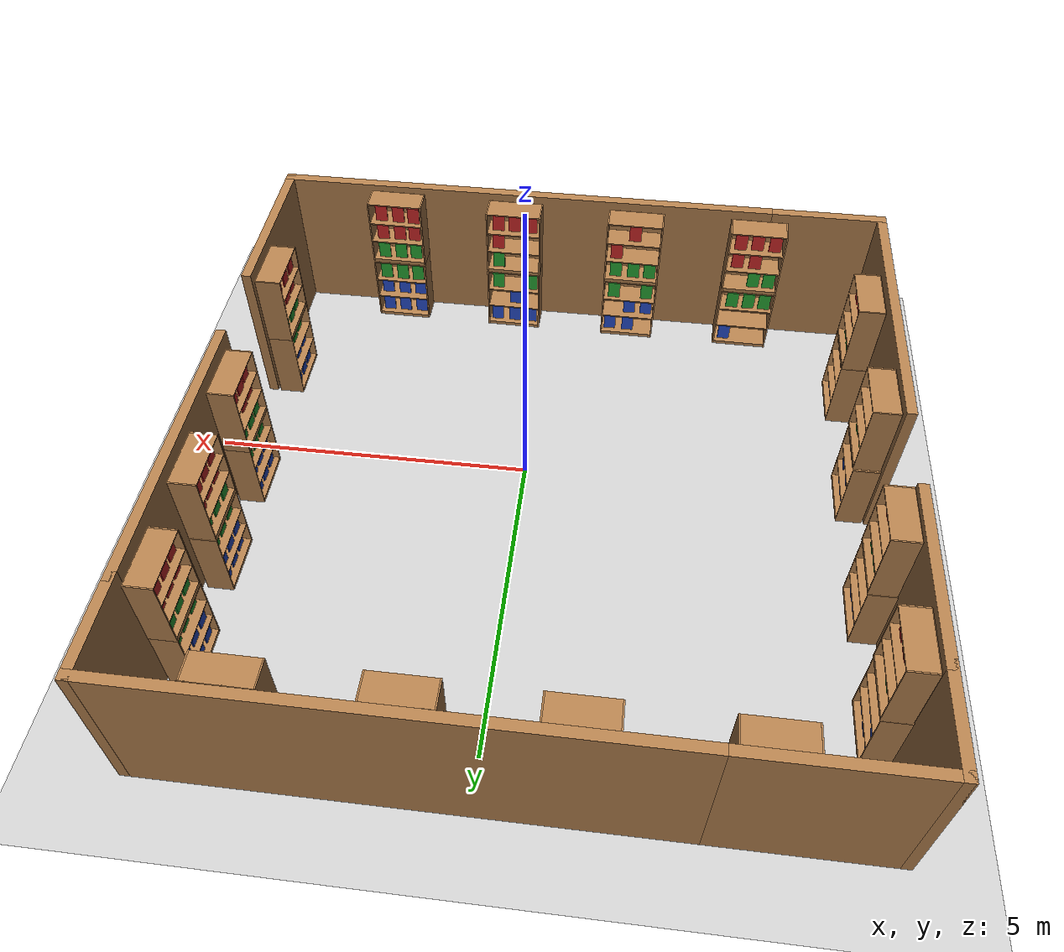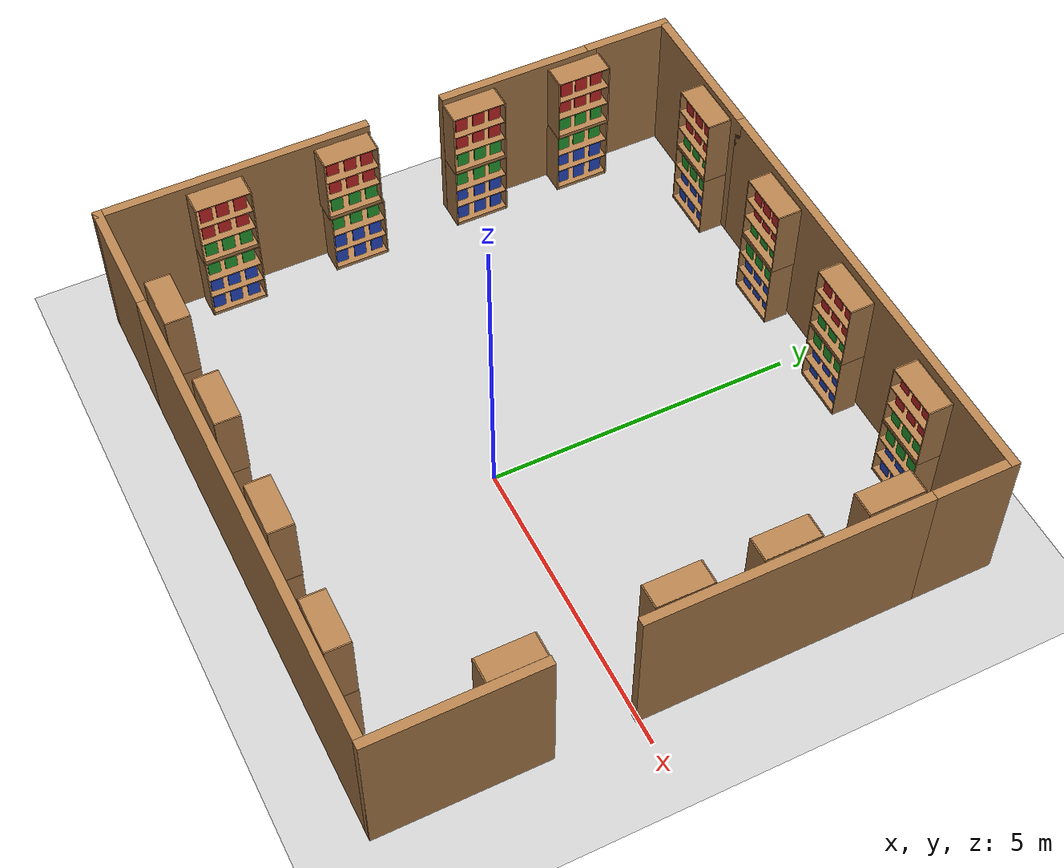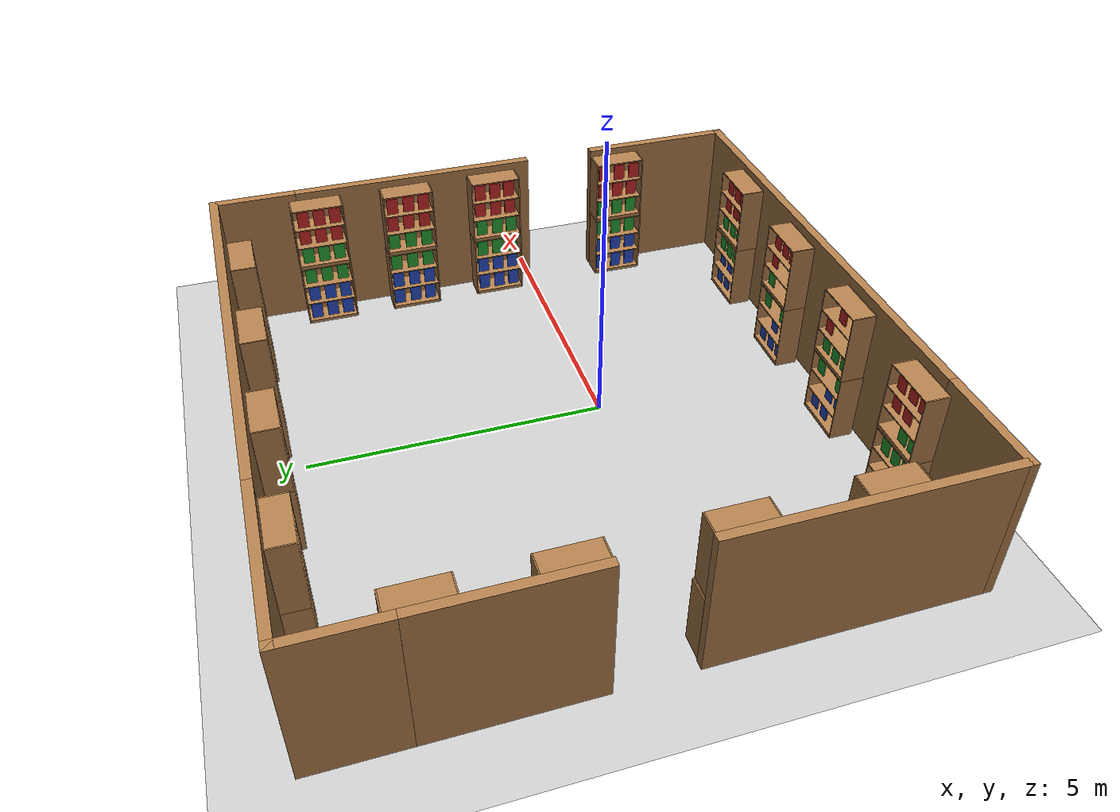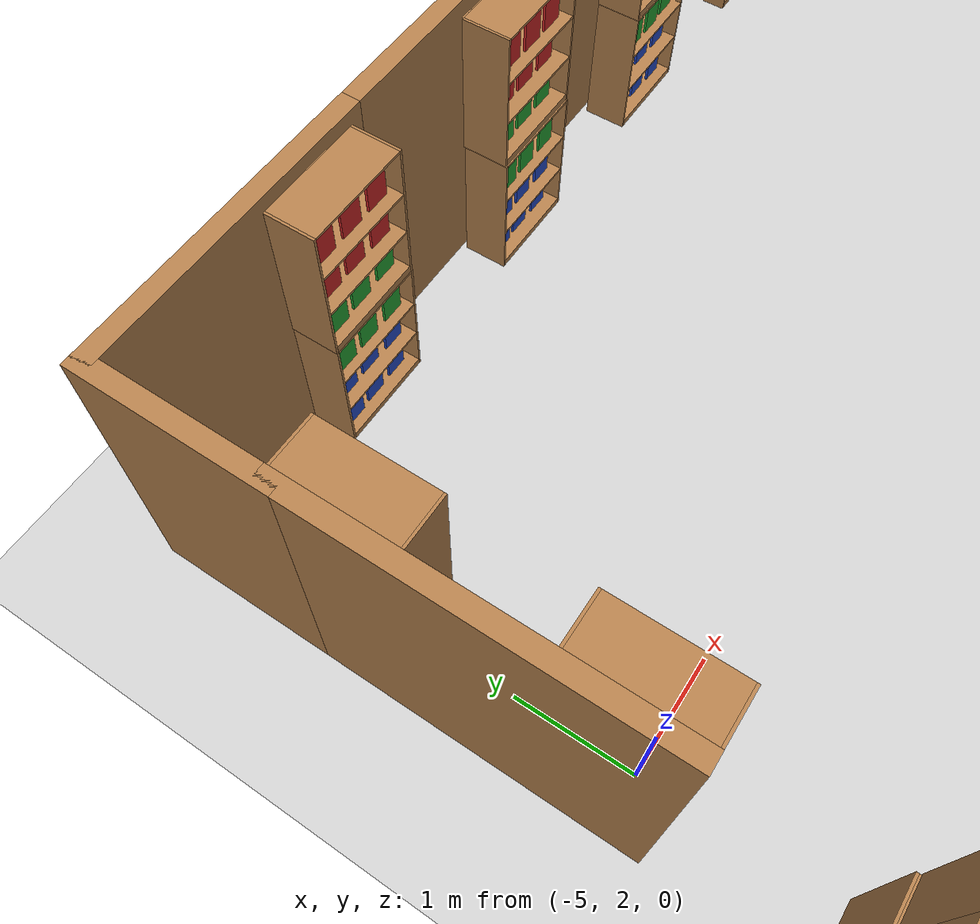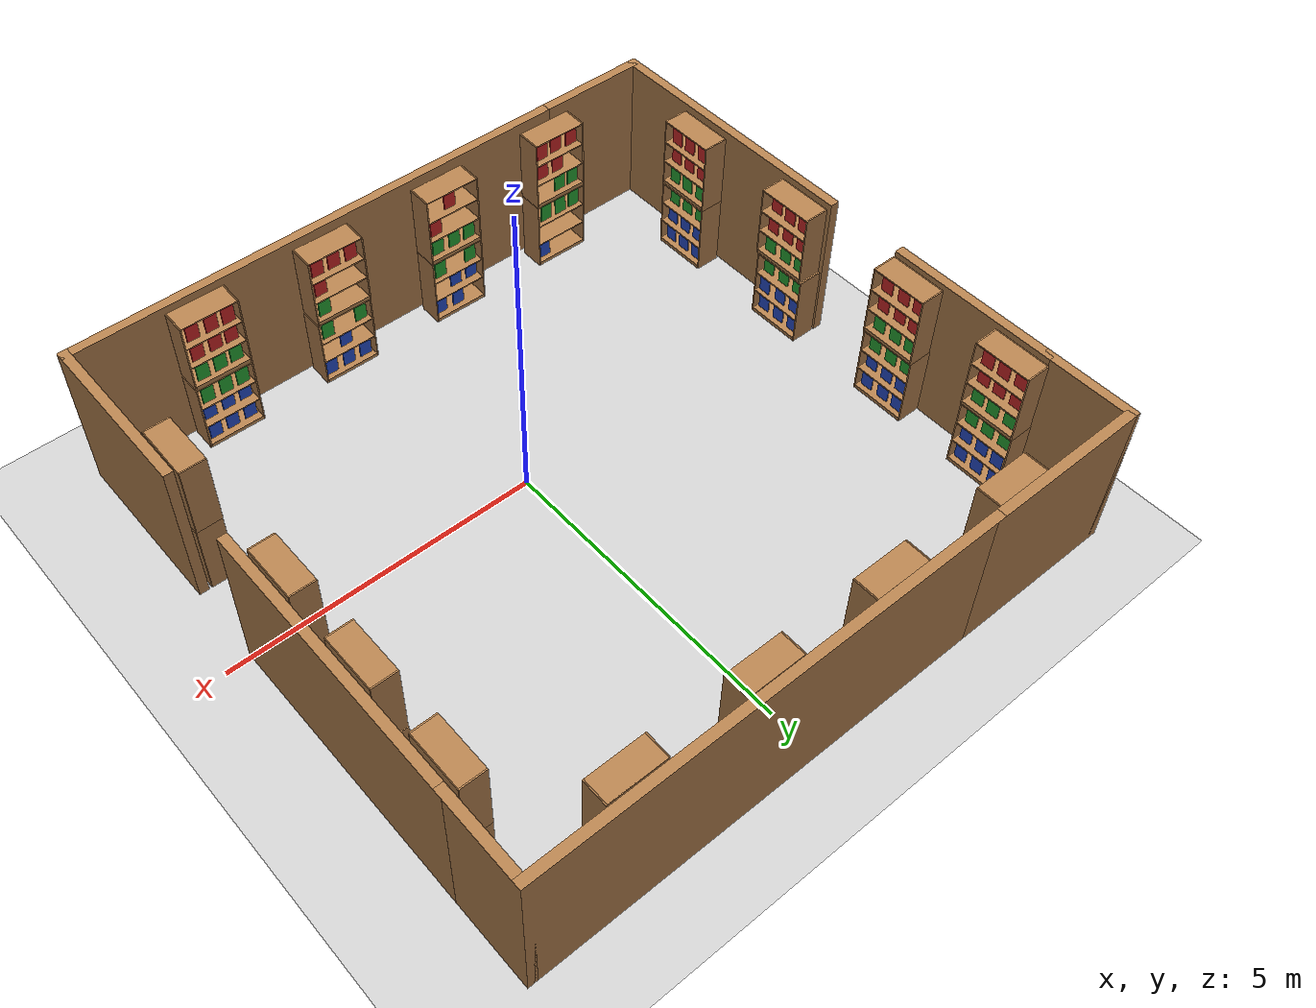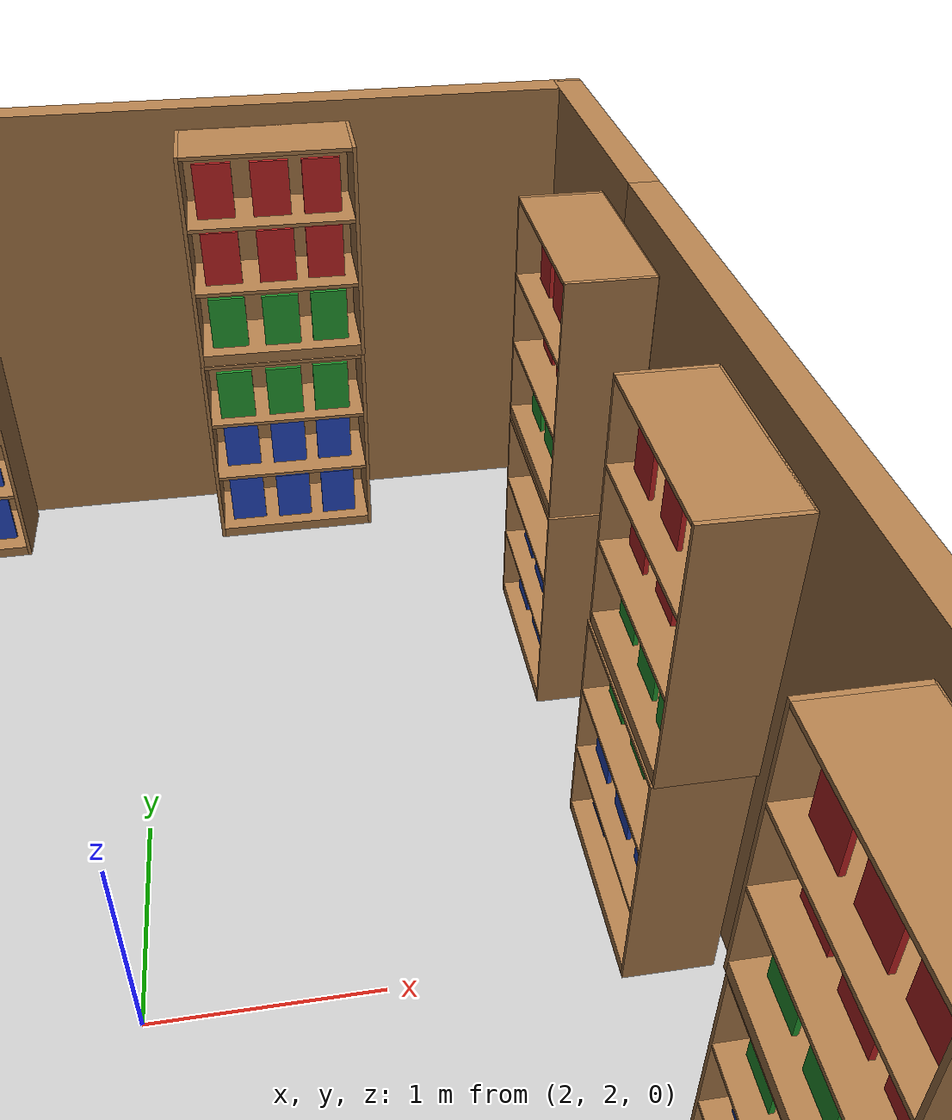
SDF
<sdf version="1.6">
 <world name="default">
  <light name="sun" type="directional">
   <pose>0 0 10 0 -0 0</pose>
   <diffuse>0.8 0.8 0.8 1</diffuse>
   <specular>0.1 0.1 0.1 1</specular>
   <attenuation>
    <range>1000</range>
    <constant>0.9</constant>
    <linear>0.01</linear>
    <quadratic>0.001</quadratic>
   </attenuation>
   <direction>-0.5 0.5 -1</direction>
  </light>
  <model name="ground_plane">
   <static>1</static>
   <link name="link">
    <collision name="collision">
     <geometry><plane><normal>0 0 1</normal><size>100 100</size></plane></geometry>
     <surface><friction><ode><mu>100</mu><mu2>50</mu2></ode></friction></surface>
    </collision>
    <visual name="visual">
     <cast_shadows>0</cast_shadows>
     <geometry><plane><normal>0 0 1</normal><size>100 100</size></plane></geometry>
     <material>
      <script><uri>file://media/materials/scripts/gazebo.material</uri><name>Gazebo/Grey</name></script>
     </material>
    </visual>
   </link>
  </model>
  <gravity>0 0 -9.8</gravity>
  <magnetic_field>6e-06 2.3e-05 -4.2e-05</magnetic_field>
  <atmosphere type="adiabatic"/>
  <physics name="default_physics" default="0" type="ode">
   <max_step_size>0.001</max_step_size>
   <real_time_factor>1</real_time_factor>
   <real_time_update_rate>1000</real_time_update_rate>
  </physics>
  <scene><ambient>0.4 0.4 0.4 1</ambient><background>0.7 0.7 0.7 1</background><shadows>1</shadows></scene>
  <spherical_coordinates>
   <surface_model>EARTH_WGS84</surface_model>
   <latitude_deg>0</latitude_deg>
   <longitude_deg>0</longitude_deg>
   <elevation>0</elevation>
   <heading_deg>0</heading_deg>
  </spherical_coordinates>
  <model name="shopping_mart_box">
   <pose>-0.44063 0.87202 0 0 -0 0</pose>
   <link name="Wall_11">
    <collision name="Wall_11_Collision">
     <geometry><box><size>2 0.15 2.5</size></box></geometry>
     <pose>0 0 1.25 0 -0 0</pose>
    </collision>
    <visual name="Wall_11_Visual">
     <pose>0 0 1.25 0 -0 0</pose>
     <geometry><box><size>2 0.15 2.5</size></box></geometry>
     <material>
      <script><uri>file://media/materials/scripts/gazebo.material</uri><name>Gazebo/Wood</name></script>
      <ambient>1 1 1 1</ambient>
     </material>
    </visual>
    <pose>-4.05 -4.85 0 0 -0 3.14159</pose>
   </link>
   <link name="Wall_12">
    <collision name="Wall_12_Collision">
     <geometry><box><size>4.5 0.15 2.5</size></box></geometry>
     <pose>0 0 1.25 0 -0 0</pose>
    </collision>
    <visual name="Wall_12_Visual">
     <pose>0 0 1.25 0 -0 0</pose>
     <geometry><box><size>4.5 0.15 2.5</size></box></geometry>
     <material>
      <script><uri>file://media/materials/scripts/gazebo.material</uri><name>Gazebo/Wood</name></script>
      <ambient>1 1 1 1</ambient>
     </material>
    </visual>
    <pose>-4.975 -2.675 0 0 -0 1.5708</pose>
   </link>
   <link name="Wall_15">
    <collision name="Wall_15_Collision">
     <geometry><box><size>2.75 0.15 2.5</size></box></geometry>
     <pose>0 0 1.25 0 -0 0</pose>
    </collision>
    <visual name="Wall_15_Visual">
     <pose>0 0 1.25 0 -0 0</pose>
     <geometry><box><size>2.75 0.15 2.5</size></box></geometry>
     <material>
      <script><uri>file://media/materials/scripts/gazebo.material</uri><name>Gazebo/Wood</name></script>
      <ambient>1 1 1 1</ambient>
     </material>
    </visual>
    <pose>-4.975 2.2 0 0 0 -1.5708</pose>
   </link>
   <link name="Wall_17">
    <collision name="Wall_17_Collision">
     <geometry><box><size>1.5 0.15 2.5</size></box></geometry>
     <pose>0 0 1.25 0 -0 0</pose>
    </collision>
    <visual name="Wall_17_Visual">
     <pose>0 0 1.25 0 -0 0</pose>
     <geometry><box><size>1.5 0.15 2.5</size></box></geometry>
     <material>
      <script><uri>file://media/materials/scripts/gazebo.material</uri><name>Gazebo/Wood</name></script>
      <ambient>1 1 1 1</ambient>
     </material>
    </visual>
    <pose>-4.975 4.175 0 0 -0 1.5708</pose>
   </link>
   <link name="Wall_21">
    <collision name="Wall_21_Collision">
     <geometry><box><size>2.75 0.15 2.5</size></box></geometry>
     <pose>0 0 1.25 0 -0 0</pose>
    </collision>
    <visual name="Wall_21_Visual">
     <pose>0 0 1.25 0 -0 0</pose>
     <geometry><box><size>2.75 0.15 2.5</size></box></geometry>
     <material>
      <script><uri>file://media/materials/scripts/gazebo.material</uri><name>Gazebo/Wood</name></script>
      <ambient>1 1 1 1</ambient>
     </material>
    </visual>
    <pose>-3.675 4.85 0 0 -0 0</pose>
   </link>
   <link name="Wall_22">
    <collision name="Wall_22_Collision">
     <geometry><box><size>7.5 0.15 2.5</size></box></geometry>
     <pose>0 0 1.25 0 -0 0</pose>
    </collision>
    <visual name="Wall_22_Visual">
     <pose>0 0 1.25 0 -0 0</pose>
     <geometry><box><size>7.5 0.15 2.5</size></box></geometry>
     <material>
      <script><uri>file://media/materials/scripts/gazebo.material</uri><name>Gazebo/Wood</name></script>
      <ambient>1 1 1 1</ambient>
     </material>
    </visual>
    <pose>1.3 4.85 0 0 -0 0</pose>
   </link>
   <link name="Wall_23">
    <collision name="Wall_23_Collision">
     <geometry><box><size>1.5 0.15 2.5</size></box></geometry>
     <pose>0 0 1.25 0 -0 0</pose>
    </collision>
    <visual name="Wall_23_Visual">
     <pose>0 0 1.25 0 -0 0</pose>
     <geometry><box><size>1.5 0.15 2.5</size></box></geometry>
     <material>
      <script><uri>file://media/materials/scripts/gazebo.material</uri><name>Gazebo/Wood</name></script>
      <ambient>1 1 1 1</ambient>
     </material>
    </visual>
    <pose>4.975 4.175 0 0 0 -1.5708</pose>
   </link>
   <link name="Wall_29">
    <collision name="Wall_29_Collision">
     <geometry><box><size>4.5 0.15 2.5</size></box></geometry>
     <pose>0 0 1.25 0 -0 0</pose>
    </collision>
    <visual name="Wall_29_Visual">
     <pose>0 0 1.25 0 -0 0</pose>
     <geometry><box><size>4.5 0.15 2.5</size></box></geometry>
     <material>
      <script><uri>file://media/materials/scripts/gazebo.material</uri><name>Gazebo/Wood</name></script>
      <ambient>1 1 1 1</ambient>
     </material>
    </visual>
    <pose>4.975 1.325 0 0 0 -1.5708</pose>
   </link>
   <link name="Wall_31">
    <collision name="Wall_31_Collision">
     <geometry><box><size>2.75 0.15 2.5</size></box></geometry>
     <pose>0 0 1.25 0 -0 0</pose>
    </collision>
    <visual name="Wall_31_Visual">
     <pose>0 0 1.25 0 -0 0</pose>
     <geometry><box><size>2.75 0.15 2.5</size></box></geometry>
     <material>
      <script><uri>file://media/materials/scripts/gazebo.material</uri><name>Gazebo/Wood</name></script>
      <ambient>1 1 1 1</ambient>
     </material>
    </visual>
    <pose>4.975 -3.55 0 0 -0 1.5708</pose>
   </link>
   <link name="Wall_6">
    <collision name="Wall_6_Collision">
     <geometry><box><size>8.25 0.15 2.5</size></box></geometry>
     <pose>0 0 1.25 0 -0 0</pose>
    </collision>
    <visual name="Wall_6_Visual">
     <pose>0 0 1.25 0 -0 0</pose>
     <geometry><box><size>8.25 0.15 2.5</size></box></geometry>
     <material>
      <script><uri>file://media/materials/scripts/gazebo.material</uri><name>Gazebo/Wood</name></script>
      <ambient>1 1 1 1</ambient>
     </material>
    </visual>
    <pose>0.925 -4.85 0 0 -0 0</pose>
   </link>
   <static>1</static>
  </model>
  <model name="bookshelf">
   <static>1</static>
   <link name="link">
    <inertial><mass>1</mass></inertial>
    <collision name="back">
     <pose>0 0.005 0.6 0 -0 0</pose>
     <geometry><box><size>0.9 0.01 1.2</size></box></geometry>
    </collision>
    <visual name="visual1">
     <pose>0 0.005 0.6 0 -0 0</pose>
     <geometry><box><size>0.9 0.01 1.2</size></box></geometry>
     <material>
      <script><uri>file://media/materials/scripts/gazebo.material</uri><name>Gazebo/Wood</name></script>
     </material>
    </visual>
    <collision name="left_side">
     <pose>0.45 -0.195 0.6 0 -0 0</pose>
     <geometry><box><size>0.02 0.4 1.2</size></box></geometry>
    </collision>
    <visual name="visual2">
     <pose>0.45 -0.195 0.6 0 -0 0</pose>
     <geometry><box><size>0.02 0.4 1.2</size></box></geometry>
     <material>
      <script><uri>file://media/materials/scripts/gazebo.material</uri><name>Gazebo/Wood</name></script>
     </material>
    </visual>
    <collision name="right_side">
     <pose>-0.45 -0.195 0.6 0 -0 0</pose>
     <geometry><box><size>0.02 0.4 1.2</size></box></geometry>
    </collision>
    <visual name="visual3">
     <pose>-0.45 -0.195 0.6 0 -0 0</pose>
     <geometry><box><size>0.02 0.4 1.2</size></box></geometry>
     <material>
      <script><uri>file://media/materials/scripts/gazebo.material</uri><name>Gazebo/Wood</name></script>
     </material>
    </visual>
    <collision name="bottom">
     <pose>0 -0.195 0.03 0 -0 0</pose>
     <geometry><box><size>0.88 0.4 0.06</size></box></geometry>
    </collision>
    <visual name="visual4">
     <pose>0 -0.195 0.03 0 -0 0</pose>
     <geometry><box><size>0.88 0.4 0.06</size></box></geometry>
     <material>
      <script><uri>file://media/materials/scripts/gazebo.material</uri><name>Gazebo/Wood</name></script>
     </material>
    </visual>
    <collision name="top">
     <pose>0 -0.195 1.19 0 -0 0</pose>
     <geometry><box><size>0.88 0.4 0.02</size></box></geometry>
    </collision>
    <visual name="visual5">
     <pose>0 -0.195 1.19 0 -0 0</pose>
     <geometry><box><size>0.88 0.4 0.02</size></box></geometry>
     <material>
      <script><uri>file://media/materials/scripts/gazebo.material</uri><name>Gazebo/Wood</name></script>
     </material>
    </visual>
    <collision name="low_shelf">
     <pose>0 -0.195 0.43 0 -0 0</pose>
     <geometry><box><size>0.88 0.4 0.02</size></box></geometry>
    </collision>
    <visual name="visual6">
     <pose>0 -0.195 0.43 0 -0 0</pose>
     <geometry><box><size>0.88 0.4 0.02</size></box></geometry>
     <material>
      <script><uri>file://media/materials/scripts/gazebo.material</uri><name>Gazebo/Wood</name></script>
     </material>
    </visual>
    <collision name="high_shelf">
     <pose>0 -0.195 0.8 0 -0 0</pose>
     <geometry><box><size>0.88 0.4 0.02</size></box></geometry>
    </collision>
    <visual name="visual7">
     <pose>0 -0.195 0.8 0 -0 0</pose>
     <geometry><box><size>0.88 0.4 0.02</size></box></geometry>
     <material>
      <script><uri>file://media/materials/scripts/gazebo.material</uri><name>Gazebo/Wood</name></script>
     </material>
    </visual>
   </link>
   <pose>2.83268 5.58259 0 0 -0 0</pose>
  </model>
  <model name="bookshelf_1">
   <static>1</static>
   <link name="link">
    <inertial><mass>1</mass></inertial>
    <collision name="back">
     <pose>0 0.005 0.6 0 -0 0</pose>
     <geometry><box><size>0.9 0.01 1.2</size></box></geometry>
    </collision>
    <visual name="visual1">
     <pose>0 0.005 0.6 0 -0 0</pose>
     <geometry><box><size>0.9 0.01 1.2</size></box></geometry>
     <material>
      <script><uri>file://media/materials/scripts/gazebo.material</uri><name>Gazebo/Wood</name></script>
     </material>
    </visual>
    <collision name="left_side">
     <pose>0.45 -0.195 0.6 0 -0 0</pose>
     <geometry><box><size>0.02 0.4 1.2</size></box></geometry>
    </collision>
    <visual name="visual2">
     <pose>0.45 -0.195 0.6 0 -0 0</pose>
     <geometry><box><size>0.02 0.4 1.2</size></box></geometry>
     <material>
      <script><uri>file://media/materials/scripts/gazebo.material</uri><name>Gazebo/Wood</name></script>
     </material>
    </visual>
    <collision name="right_side">
     <pose>-0.45 -0.195 0.6 0 -0 0</pose>
     <geometry><box><size>0.02 0.4 1.2</size></box></geometry>
    </collision>
    <visual name="visual3">
     <pose>-0.45 -0.195 0.6 0 -0 0</pose>
     <geometry><box><size>0.02 0.4 1.2</size></box></geometry>
     <material>
      <script><uri>file://media/materials/scripts/gazebo.material</uri><name>Gazebo/Wood</name></script>
     </material>
    </visual>
    <collision name="bottom">
     <pose>0 -0.195 0.03 0 -0 0</pose>
     <geometry><box><size>0.88 0.4 0.06</size></box></geometry>
    </collision>
    <visual name="visual4">
     <pose>0 -0.195 0.03 0 -0 0</pose>
     <geometry><box><size>0.88 0.4 0.06</size></box></geometry>
     <material>
      <script><uri>file://media/materials/scripts/gazebo.material</uri><name>Gazebo/Wood</name></script>
     </material>
    </visual>
    <collision name="top">
     <pose>0 -0.195 1.19 0 -0 0</pose>
     <geometry><box><size>0.88 0.4 0.02</size></box></geometry>
    </collision>
    <visual name="visual5">
     <pose>0 -0.195 1.19 0 -0 0</pose>
     <geometry><box><size>0.88 0.4 0.02</size></box></geometry>
     <material>
      <script><uri>file://media/materials/scripts/gazebo.material</uri><name>Gazebo/Wood</name></script>
     </material>
    </visual>
    <collision name="low_shelf">
     <pose>0 -0.195 0.43 0 -0 0</pose>
     <geometry><box><size>0.88 0.4 0.02</size></box></geometry>
    </collision>
    <visual name="visual6">
     <pose>0 -0.195 0.43 0 -0 0</pose>
     <geometry><box><size>0.88 0.4 0.02</size></box></geometry>
     <material>
      <script><uri>file://media/materials/scripts/gazebo.material</uri><name>Gazebo/Wood</name></script>
     </material>
    </visual>
    <collision name="high_shelf">
     <pose>0 -0.195 0.8 0 -0 0</pose>
     <geometry><box><size>0.88 0.4 0.02</size></box></geometry>
    </collision>
    <visual name="visual7">
     <pose>0 -0.195 0.8 0 -0 0</pose>
     <geometry><box><size>0.88 0.4 0.02</size></box></geometry>
     <material>
      <script><uri>file://media/materials/scripts/gazebo.material</uri><name>Gazebo/Wood</name></script>
     </material>
    </visual>
   </link>
   <pose>0.770602 5.5901 0 0 -0 0</pose>
  </model>
  <model name="bookshelf_2_clone">
   <static>1</static>
   <link name="link">
    <inertial><mass>1</mass></inertial>
    <collision name="back">
     <pose>0 0.005 0.6 0 -0 0</pose>
     <geometry><box><size>0.9 0.01 1.2</size></box></geometry>
    </collision>
    <visual name="visual1">
     <pose>0 0.005 0.6 0 -0 0</pose>
     <geometry><box><size>0.9 0.01 1.2</size></box></geometry>
     <material>
      <script><uri>file://media/materials/scripts/gazebo.material</uri><name>Gazebo/Wood</name></script>
     </material>
    </visual>
    <collision name="left_side">
     <pose>0.45 -0.195 0.6 0 -0 0</pose>
     <geometry><box><size>0.02 0.4 1.2</size></box></geometry>
    </collision>
    <visual name="visual2">
     <pose>0.45 -0.195 0.6 0 -0 0</pose>
     <geometry><box><size>0.02 0.4 1.2</size></box></geometry>
     <material>
      <script><uri>file://media/materials/scripts/gazebo.material</uri><name>Gazebo/Wood</name></script>
     </material>
    </visual>
    <collision name="right_side">
     <pose>-0.45 -0.195 0.6 0 -0 0</pose>
     <geometry><box><size>0.02 0.4 1.2</size></box></geometry>
    </collision>
    <visual name="visual3">
     <pose>-0.45 -0.195 0.6 0 -0 0</pose>
     <geometry><box><size>0.02 0.4 1.2</size></box></geometry>
     <material>
      <script><uri>file://media/materials/scripts/gazebo.material</uri><name>Gazebo/Wood</name></script>
     </material>
    </visual>
    <collision name="bottom">
     <pose>0 -0.195 0.03 0 -0 0</pose>
     <geometry><box><size>0.88 0.4 0.06</size></box></geometry>
    </collision>
    <visual name="visual4">
     <pose>0 -0.195 0.03 0 -0 0</pose>
     <geometry><box><size>0.88 0.4 0.06</size></box></geometry>
     <material>
      <script><uri>file://media/materials/scripts/gazebo.material</uri><name>Gazebo/Wood</name></script>
     </material>
    </visual>
    <collision name="top">
     <pose>0 -0.195 1.19 0 -0 0</pose>
     <geometry><box><size>0.88 0.4 0.02</size></box></geometry>
    </collision>
    <visual name="visual5">
     <pose>0 -0.195 1.19 0 -0 0</pose>
     <geometry><box><size>0.88 0.4 0.02</size></box></geometry>
     <material>
      <script><uri>file://media/materials/scripts/gazebo.material</uri><name>Gazebo/Wood</name></script>
     </material>
    </visual>
    <collision name="low_shelf">
     <pose>0 -0.195 0.43 0 -0 0</pose>
     <geometry><box><size>0.88 0.4 0.02</size></box></geometry>
    </collision>
    <visual name="visual6">
     <pose>0 -0.195 0.43 0 -0 0</pose>
     <geometry><box><size>0.88 0.4 0.02</size></box></geometry>
     <material>
      <script><uri>file://media/materials/scripts/gazebo.material</uri><name>Gazebo/Wood</name></script>
     </material>
    </visual>
    <collision name="high_shelf">
     <pose>0 -0.195 0.8 0 -0 0</pose>
     <geometry><box><size>0.88 0.4 0.02</size></box></geometry>
    </collision>
    <visual name="visual7">
     <pose>0 -0.195 0.8 0 -0 0</pose>
     <geometry><box><size>0.88 0.4 0.02</size></box></geometry>
     <material>
      <script><uri>file://media/materials/scripts/gazebo.material</uri><name>Gazebo/Wood</name></script>
     </material>
    </visual>
   </link>
   <pose>-1.30264 5.59901 0 0 -0 0</pose>
  </model>
  <model name="bookshelf_2_clone_clone">
   <static>1</static>
   <link name="link">
    <inertial><mass>1</mass></inertial>
    <collision name="back">
     <pose>0 0.005 0.6 0 -0 0</pose>
     <geometry><box><size>0.9 0.01 1.2</size></box></geometry>
    </collision>
    <visual name="visual1">
     <pose>0 0.005 0.6 0 -0 0</pose>
     <geometry><box><size>0.9 0.01 1.2</size></box></geometry>
     <material>
      <script><uri>file://media/materials/scripts/gazebo.material</uri><name>Gazebo/Wood</name></script>
     </material>
    </visual>
    <collision name="left_side">
     <pose>0.45 -0.195 0.6 0 -0 0</pose>
     <geometry><box><size>0.02 0.4 1.2</size></box></geometry>
    </collision>
    <visual name="visual2">
     <pose>0.45 -0.195 0.6 0 -0 0</pose>
     <geometry><box><size>0.02 0.4 1.2</size></box></geometry>
     <material>
      <script><uri>file://media/materials/scripts/gazebo.material</uri><name>Gazebo/Wood</name></script>
     </material>
    </visual>
    <collision name="right_side">
     <pose>-0.45 -0.195 0.6 0 -0 0</pose>
     <geometry><box><size>0.02 0.4 1.2</size></box></geometry>
    </collision>
    <visual name="visual3">
     <pose>-0.45 -0.195 0.6 0 -0 0</pose>
     <geometry><box><size>0.02 0.4 1.2</size></box></geometry>
     <material>
      <script><uri>file://media/materials/scripts/gazebo.material</uri><name>Gazebo/Wood</name></script>
     </material>
    </visual>
    <collision name="bottom">
     <pose>0 -0.195 0.03 0 -0 0</pose>
     <geometry><box><size>0.88 0.4 0.06</size></box></geometry>
    </collision>
    <visual name="visual4">
     <pose>0 -0.195 0.03 0 -0 0</pose>
     <geometry><box><size>0.88 0.4 0.06</size></box></geometry>
     <material>
      <script><uri>file://media/materials/scripts/gazebo.material</uri><name>Gazebo/Wood</name></script>
     </material>
    </visual>
    <collision name="top">
     <pose>0 -0.195 1.19 0 -0 0</pose>
     <geometry><box><size>0.88 0.4 0.02</size></box></geometry>
    </collision>
    <visual name="visual5">
     <pose>0 -0.195 1.19 0 -0 0</pose>
     <geometry><box><size>0.88 0.4 0.02</size></box></geometry>
     <material>
      <script><uri>file://media/materials/scripts/gazebo.material</uri><name>Gazebo/Wood</name></script>
     </material>
    </visual>
    <collision name="low_shelf">
     <pose>0 -0.195 0.43 0 -0 0</pose>
     <geometry><box><size>0.88 0.4 0.02</size></box></geometry>
    </collision>
    <visual name="visual6">
     <pose>0 -0.195 0.43 0 -0 0</pose>
     <geometry><box><size>0.88 0.4 0.02</size></box></geometry>
     <material>
      <script><uri>file://media/materials/scripts/gazebo.material</uri><name>Gazebo/Wood</name></script>
     </material>
    </visual>
    <collision name="high_shelf">
     <pose>0 -0.195 0.8 0 -0 0</pose>
     <geometry><box><size>0.88 0.4 0.02</size></box></geometry>
    </collision>
    <visual name="visual7">
     <pose>0 -0.195 0.8 0 -0 0</pose>
     <geometry><box><size>0.88 0.4 0.02</size></box></geometry>
     <material>
      <script><uri>file://media/materials/scripts/gazebo.material</uri><name>Gazebo/Wood</name></script>
     </material>
    </visual>
   </link>
   <pose>-3.46853 5.62428 0 0 -0 0</pose>
  </model>
  <model name="bookshelf_3_clone">
   <static>1</static>
   <link name="link">
    <inertial><mass>1</mass></inertial>
    <collision name="back">
     <pose>0 0.005 0.6 0 -0 0</pose>
     <geometry><box><size>0.9 0.01 1.2</size></box></geometry>
    </collision>
    <visual name="visual1">
     <pose>0 0.005 0.6 0 -0 0</pose>
     <geometry><box><size>0.9 0.01 1.2</size></box></geometry>
     <material>
      <script><uri>file://media/materials/scripts/gazebo.material</uri><name>Gazebo/Wood</name></script>
     </material>
    </visual>
    <collision name="left_side">
     <pose>0.45 -0.195 0.6 0 -0 0</pose>
     <geometry><box><size>0.02 0.4 1.2</size></box></geometry>
    </collision>
    <visual name="visual2">
     <pose>0.45 -0.195 0.6 0 -0 0</pose>
     <geometry><box><size>0.02 0.4 1.2</size></box></geometry>
     <material>
      <script><uri>file://media/materials/scripts/gazebo.material</uri><name>Gazebo/Wood</name></script>
     </material>
    </visual>
    <collision name="right_side">
     <pose>-0.45 -0.195 0.6 0 -0 0</pose>
     <geometry><box><size>0.02 0.4 1.2</size></box></geometry>
    </collision>
    <visual name="visual3">
     <pose>-0.45 -0.195 0.6 0 -0 0</pose>
     <geometry><box><size>0.02 0.4 1.2</size></box></geometry>
     <material>
      <script><uri>file://media/materials/scripts/gazebo.material</uri><name>Gazebo/Wood</name></script>
     </material>
    </visual>
    <collision name="bottom">
     <pose>0 -0.195 0.03 0 -0 0</pose>
     <geometry><box><size>0.88 0.4 0.06</size></box></geometry>
    </collision>
    <visual name="visual4">
     <pose>0 -0.195 0.03 0 -0 0</pose>
     <geometry><box><size>0.88 0.4 0.06</size></box></geometry>
     <material>
      <script><uri>file://media/materials/scripts/gazebo.material</uri><name>Gazebo/Wood</name></script>
     </material>
    </visual>
    <collision name="top">
     <pose>0 -0.195 1.19 0 -0 0</pose>
     <geometry><box><size>0.88 0.4 0.02</size></box></geometry>
    </collision>
    <visual name="visual5">
     <pose>0 -0.195 1.19 0 -0 0</pose>
     <geometry><box><size>0.88 0.4 0.02</size></box></geometry>
     <material>
      <script><uri>file://media/materials/scripts/gazebo.material</uri><name>Gazebo/Wood</name></script>
     </material>
    </visual>
    <collision name="low_shelf">
     <pose>0 -0.195 0.43 0 -0 0</pose>
     <geometry><box><size>0.88 0.4 0.02</size></box></geometry>
    </collision>
    <visual name="visual6">
     <pose>0 -0.195 0.43 0 -0 0</pose>
     <geometry><box><size>0.88 0.4 0.02</size></box></geometry>
     <material>
      <script><uri>file://media/materials/scripts/gazebo.material</uri><name>Gazebo/Wood</name></script>
     </material>
    </visual>
    <collision name="high_shelf">
     <pose>0 -0.195 0.8 0 -0 0</pose>
     <geometry><box><size>0.88 0.4 0.02</size></box></geometry>
    </collision>
    <visual name="visual7">
     <pose>0 -0.195 0.8 0 -0 0</pose>
     <geometry><box><size>0.88 0.4 0.02</size></box></geometry>
     <material>
      <script><uri>file://media/materials/scripts/gazebo.material</uri><name>Gazebo/Wood</name></script>
     </material>
    </visual>
   </link>
   <pose>-1.30336 5.6079 1.20481 0 -0 0</pose>
  </model>
  <model name="bookshelf_3_clone_clone">
   <static>1</static>
   <link name="link">
    <inertial><mass>1</mass></inertial>
    <collision name="back">
     <pose>0 0.005 0.6 0 -0 0</pose>
     <geometry><box><size>0.9 0.01 1.2</size></box></geometry>
    </collision>
    <visual name="visual1">
     <pose>0 0.005 0.6 0 -0 0</pose>
     <geometry><box><size>0.9 0.01 1.2</size></box></geometry>
     <material>
      <script><uri>file://media/materials/scripts/gazebo.material</uri><name>Gazebo/Wood</name></script>
     </material>
    </visual>
    <collision name="left_side">
     <pose>0.45 -0.195 0.6 0 -0 0</pose>
     <geometry><box><size>0.02 0.4 1.2</size></box></geometry>
    </collision>
    <visual name="visual2">
     <pose>0.45 -0.195 0.6 0 -0 0</pose>
     <geometry><box><size>0.02 0.4 1.2</size></box></geometry>
     <material>
      <script><uri>file://media/materials/scripts/gazebo.material</uri><name>Gazebo/Wood</name></script>
     </material>
    </visual>
    <collision name="right_side">
     <pose>-0.45 -0.195 0.6 0 -0 0</pose>
     <geometry><box><size>0.02 0.4 1.2</size></box></geometry>
    </collision>
    <visual name="visual3">
     <pose>-0.45 -0.195 0.6 0 -0 0</pose>
     <geometry><box><size>0.02 0.4 1.2</size></box></geometry>
     <material>
      <script><uri>file://media/materials/scripts/gazebo.material</uri><name>Gazebo/Wood</name></script>
     </material>
    </visual>
    <collision name="bottom">
     <pose>0 -0.195 0.03 0 -0 0</pose>
     <geometry><box><size>0.88 0.4 0.06</size></box></geometry>
    </collision>
    <visual name="visual4">
     <pose>0 -0.195 0.03 0 -0 0</pose>
     <geometry><box><size>0.88 0.4 0.06</size></box></geometry>
     <material>
      <script><uri>file://media/materials/scripts/gazebo.material</uri><name>Gazebo/Wood</name></script>
     </material>
    </visual>
    <collision name="top">
     <pose>0 -0.195 1.19 0 -0 0</pose>
     <geometry><box><size>0.88 0.4 0.02</size></box></geometry>
    </collision>
    <visual name="visual5">
     <pose>0 -0.195 1.19 0 -0 0</pose>
     <geometry><box><size>0.88 0.4 0.02</size></box></geometry>
     <material>
      <script><uri>file://media/materials/scripts/gazebo.material</uri><name>Gazebo/Wood</name></script>
     </material>
    </visual>
    <collision name="low_shelf">
     <pose>0 -0.195 0.43 0 -0 0</pose>
     <geometry><box><size>0.88 0.4 0.02</size></box></geometry>
    </collision>
    <visual name="visual6">
     <pose>0 -0.195 0.43 0 -0 0</pose>
     <geometry><box><size>0.88 0.4 0.02</size></box></geometry>
     <material>
      <script><uri>file://media/materials/scripts/gazebo.material</uri><name>Gazebo/Wood</name></script>
     </material>
    </visual>
    <collision name="high_shelf">
     <pose>0 -0.195 0.8 0 -0 0</pose>
     <geometry><box><size>0.88 0.4 0.02</size></box></geometry>
    </collision>
    <visual name="visual7">
     <pose>0 -0.195 0.8 0 -0 0</pose>
     <geometry><box><size>0.88 0.4 0.02</size></box></geometry>
     <material>
      <script><uri>file://media/materials/scripts/gazebo.material</uri><name>Gazebo/Wood</name></script>
     </material>
    </visual>
   </link>
   <pose>-3.47373 5.62521 1.20481 0 -0 0</pose>
  </model>
  <model name="bookshelf_3_clone_clone_0">
   <static>1</static>
   <link name="link">
    <inertial><mass>1</mass></inertial>
    <collision name="back">
     <pose>0 0.005 0.6 0 -0 0</pose>
     <geometry><box><size>0.9 0.01 1.2</size></box></geometry>
    </collision>
    <visual name="visual1">
     <pose>0 0.005 0.6 0 -0 0</pose>
     <geometry><box><size>0.9 0.01 1.2</size></box></geometry>
     <material>
      <script><uri>file://media/materials/scripts/gazebo.material</uri><name>Gazebo/Wood</name></script>
     </material>
    </visual>
    <collision name="left_side">
     <pose>0.45 -0.195 0.6 0 -0 0</pose>
     <geometry><box><size>0.02 0.4 1.2</size></box></geometry>
    </collision>
    <visual name="visual2">
     <pose>0.45 -0.195 0.6 0 -0 0</pose>
     <geometry><box><size>0.02 0.4 1.2</size></box></geometry>
     <material>
      <script><uri>file://media/materials/scripts/gazebo.material</uri><name>Gazebo/Wood</name></script>
     </material>
    </visual>
    <collision name="right_side">
     <pose>-0.45 -0.195 0.6 0 -0 0</pose>
     <geometry><box><size>0.02 0.4 1.2</size></box></geometry>
    </collision>
    <visual name="visual3">
     <pose>-0.45 -0.195 0.6 0 -0 0</pose>
     <geometry><box><size>0.02 0.4 1.2</size></box></geometry>
     <material>
      <script><uri>file://media/materials/scripts/gazebo.material</uri><name>Gazebo/Wood</name></script>
     </material>
    </visual>
    <collision name="bottom">
     <pose>0 -0.195 0.03 0 -0 0</pose>
     <geometry><box><size>0.88 0.4 0.06</size></box></geometry>
    </collision>
    <visual name="visual4">
     <pose>0 -0.195 0.03 0 -0 0</pose>
     <geometry><box><size>0.88 0.4 0.06</size></box></geometry>
     <material>
      <script><uri>file://media/materials/scripts/gazebo.material</uri><name>Gazebo/Wood</name></script>
     </material>
    </visual>
    <collision name="top">
     <pose>0 -0.195 1.19 0 -0 0</pose>
     <geometry><box><size>0.88 0.4 0.02</size></box></geometry>
    </collision>
    <visual name="visual5">
     <pose>0 -0.195 1.19 0 -0 0</pose>
     <geometry><box><size>0.88 0.4 0.02</size></box></geometry>
     <material>
      <script><uri>file://media/materials/scripts/gazebo.material</uri><name>Gazebo/Wood</name></script>
     </material>
    </visual>
    <collision name="low_shelf">
     <pose>0 -0.195 0.43 0 -0 0</pose>
     <geometry><box><size>0.88 0.4 0.02</size></box></geometry>
    </collision>
    <visual name="visual6">
     <pose>0 -0.195 0.43 0 -0 0</pose>
     <geometry><box><size>0.88 0.4 0.02</size></box></geometry>
     <material>
      <script><uri>file://media/materials/scripts/gazebo.material</uri><name>Gazebo/Wood</name></script>
     </material>
    </visual>
    <collision name="high_shelf">
     <pose>0 -0.195 0.8 0 -0 0</pose>
     <geometry><box><size>0.88 0.4 0.02</size></box></geometry>
    </collision>
    <visual name="visual7">
     <pose>0 -0.195 0.8 0 -0 0</pose>
     <geometry><box><size>0.88 0.4 0.02</size></box></geometry>
     <material>
      <script><uri>file://media/materials/scripts/gazebo.material</uri><name>Gazebo/Wood</name></script>
     </material>
    </visual>
   </link>
   <pose>0.76852 5.59426 1.20481 0 -0 0</pose>
  </model>
  <model name="bookshelf_3_clone_clone_1">
   <static>1</static>
   <link name="link">
    <inertial><mass>1</mass></inertial>
    <collision name="back">
     <pose>0 0.005 0.6 0 -0 0</pose>
     <geometry><box><size>0.9 0.01 1.2</size></box></geometry>
    </collision>
    <visual name="visual1">
     <pose>0 0.005 0.6 0 -0 0</pose>
     <geometry><box><size>0.9 0.01 1.2</size></box></geometry>
     <material>
      <script><uri>file://media/materials/scripts/gazebo.material</uri><name>Gazebo/Wood</name></script>
     </material>
    </visual>
    <collision name="left_side">
     <pose>0.45 -0.195 0.6 0 -0 0</pose>
     <geometry><box><size>0.02 0.4 1.2</size></box></geometry>
    </collision>
    <visual name="visual2">
     <pose>0.45 -0.195 0.6 0 -0 0</pose>
     <geometry><box><size>0.02 0.4 1.2</size></box></geometry>
     <material>
      <script><uri>file://media/materials/scripts/gazebo.material</uri><name>Gazebo/Wood</name></script>
     </material>
    </visual>
    <collision name="right_side">
     <pose>-0.45 -0.195 0.6 0 -0 0</pose>
     <geometry><box><size>0.02 0.4 1.2</size></box></geometry>
    </collision>
    <visual name="visual3">
     <pose>-0.45 -0.195 0.6 0 -0 0</pose>
     <geometry><box><size>0.02 0.4 1.2</size></box></geometry>
     <material>
      <script><uri>file://media/materials/scripts/gazebo.material</uri><name>Gazebo/Wood</name></script>
     </material>
    </visual>
    <collision name="bottom">
     <pose>0 -0.195 0.03 0 -0 0</pose>
     <geometry><box><size>0.88 0.4 0.06</size></box></geometry>
    </collision>
    <visual name="visual4">
     <pose>0 -0.195 0.03 0 -0 0</pose>
     <geometry><box><size>0.88 0.4 0.06</size></box></geometry>
     <material>
      <script><uri>file://media/materials/scripts/gazebo.material</uri><name>Gazebo/Wood</name></script>
     </material>
    </visual>
    <collision name="top">
     <pose>0 -0.195 1.19 0 -0 0</pose>
     <geometry><box><size>0.88 0.4 0.02</size></box></geometry>
    </collision>
    <visual name="visual5">
     <pose>0 -0.195 1.19 0 -0 0</pose>
     <geometry><box><size>0.88 0.4 0.02</size></box></geometry>
     <material>
      <script><uri>file://media/materials/scripts/gazebo.material</uri><name>Gazebo/Wood</name></script>
     </material>
    </visual>
    <collision name="low_shelf">
     <pose>0 -0.195 0.43 0 -0 0</pose>
     <geometry><box><size>0.88 0.4 0.02</size></box></geometry>
    </collision>
    <visual name="visual6">
     <pose>0 -0.195 0.43 0 -0 0</pose>
     <geometry><box><size>0.88 0.4 0.02</size></box></geometry>
     <material>
      <script><uri>file://media/materials/scripts/gazebo.material</uri><name>Gazebo/Wood</name></script>
     </material>
    </visual>
    <collision name="high_shelf">
     <pose>0 -0.195 0.8 0 -0 0</pose>
     <geometry><box><size>0.88 0.4 0.02</size></box></geometry>
    </collision>
    <visual name="visual7">
     <pose>0 -0.195 0.8 0 -0 0</pose>
     <geometry><box><size>0.88 0.4 0.02</size></box></geometry>
     <material>
      <script><uri>file://media/materials/scripts/gazebo.material</uri><name>Gazebo/Wood</name></script>
     </material>
    </visual>
   </link>
   <pose>2.83627 5.58516 1.20481 0 -0 0</pose>
  </model>
  <model name="bookshelf_4_clone">
   <static>1</static>
   <link name="link">
    <inertial><mass>1</mass></inertial>
    <collision name="back">
     <pose>0 0.005 0.6 0 -0 0</pose>
     <geometry><box><size>0.9 0.01 1.2</size></box></geometry>
    </collision>
    <visual name="visual1">
     <pose>0 0.005 0.6 0 -0 0</pose>
     <geometry><box><size>0.9 0.01 1.2</size></box></geometry>
     <material>
      <script><uri>file://media/materials/scripts/gazebo.material</uri><name>Gazebo/Wood</name></script>
     </material>
    </visual>
    <collision name="left_side">
     <pose>0.45 -0.195 0.6 0 -0 0</pose>
     <geometry><box><size>0.02 0.4 1.2</size></box></geometry>
    </collision>
    <visual name="visual2">
     <pose>0.45 -0.195 0.6 0 -0 0</pose>
     <geometry><box><size>0.02 0.4 1.2</size></box></geometry>
     <material>
      <script><uri>file://media/materials/scripts/gazebo.material</uri><name>Gazebo/Wood</name></script>
     </material>
    </visual>
    <collision name="right_side">
     <pose>-0.45 -0.195 0.6 0 -0 0</pose>
     <geometry><box><size>0.02 0.4 1.2</size></box></geometry>
    </collision>
    <visual name="visual3">
     <pose>-0.45 -0.195 0.6 0 -0 0</pose>
     <geometry><box><size>0.02 0.4 1.2</size></box></geometry>
     <material>
      <script><uri>file://media/materials/scripts/gazebo.material</uri><name>Gazebo/Wood</name></script>
     </material>
    </visual>
    <collision name="bottom">
     <pose>0 -0.195 0.03 0 -0 0</pose>
     <geometry><box><size>0.88 0.4 0.06</size></box></geometry>
    </collision>
    <visual name="visual4">
     <pose>0 -0.195 0.03 0 -0 0</pose>
     <geometry><box><size>0.88 0.4 0.06</size></box></geometry>
     <material>
      <script><uri>file://media/materials/scripts/gazebo.material</uri><name>Gazebo/Wood</name></script>
     </material>
    </visual>
    <collision name="top">
     <pose>0 -0.195 1.19 0 -0 0</pose>
     <geometry><box><size>0.88 0.4 0.02</size></box></geometry>
    </collision>
    <visual name="visual5">
     <pose>0 -0.195 1.19 0 -0 0</pose>
     <geometry><box><size>0.88 0.4 0.02</size></box></geometry>
     <material>
      <script><uri>file://media/materials/scripts/gazebo.material</uri><name>Gazebo/Wood</name></script>
     </material>
    </visual>
    <collision name="low_shelf">
     <pose>0 -0.195 0.43 0 -0 0</pose>
     <geometry><box><size>0.88 0.4 0.02</size></box></geometry>
    </collision>
    <visual name="visual6">
     <pose>0 -0.195 0.43 0 -0 0</pose>
     <geometry><box><size>0.88 0.4 0.02</size></box></geometry>
     <material>
      <script><uri>file://media/materials/scripts/gazebo.material</uri><name>Gazebo/Wood</name></script>
     </material>
    </visual>
    <collision name="high_shelf">
     <pose>0 -0.195 0.8 0 -0 0</pose>
     <geometry><box><size>0.88 0.4 0.02</size></box></geometry>
    </collision>
    <visual name="visual7">
     <pose>0 -0.195 0.8 0 -0 0</pose>
     <geometry><box><size>0.88 0.4 0.02</size></box></geometry>
     <material>
      <script><uri>file://media/materials/scripts/gazebo.material</uri><name>Gazebo/Wood</name></script>
     </material>
    </visual>
   </link>
   <pose>4.37345 3.97883 0 0 0 -1.5727</pose>
  </model>
  <model name="bookshelf_4_clone_0">
   <static>1</static>
   <link name="link">
    <inertial><mass>1</mass></inertial>
    <collision name="back">
     <pose>0 0.005 0.6 0 -0 0</pose>
     <geometry><box><size>0.9 0.01 1.2</size></box></geometry>
    </collision>
    <visual name="visual1">
     <pose>0 0.005 0.6 0 -0 0</pose>
     <geometry><box><size>0.9 0.01 1.2</size></box></geometry>
     <material>
      <script><uri>file://media/materials/scripts/gazebo.material</uri><name>Gazebo/Wood</name></script>
     </material>
    </visual>
    <collision name="left_side">
     <pose>0.45 -0.195 0.6 0 -0 0</pose>
     <geometry><box><size>0.02 0.4 1.2</size></box></geometry>
    </collision>
    <visual name="visual2">
     <pose>0.45 -0.195 0.6 0 -0 0</pose>
     <geometry><box><size>0.02 0.4 1.2</size></box></geometry>
     <material>
      <script><uri>file://media/materials/scripts/gazebo.material</uri><name>Gazebo/Wood</name></script>
     </material>
    </visual>
    <collision name="right_side">
     <pose>-0.45 -0.195 0.6 0 -0 0</pose>
     <geometry><box><size>0.02 0.4 1.2</size></box></geometry>
    </collision>
    <visual name="visual3">
     <pose>-0.45 -0.195 0.6 0 -0 0</pose>
     <geometry><box><size>0.02 0.4 1.2</size></box></geometry>
     <material>
      <script><uri>file://media/materials/scripts/gazebo.material</uri><name>Gazebo/Wood</name></script>
     </material>
    </visual>
    <collision name="bottom">
     <pose>0 -0.195 0.03 0 -0 0</pose>
     <geometry><box><size>0.88 0.4 0.06</size></box></geometry>
    </collision>
    <visual name="visual4">
     <pose>0 -0.195 0.03 0 -0 0</pose>
     <geometry><box><size>0.88 0.4 0.06</size></box></geometry>
     <material>
      <script><uri>file://media/materials/scripts/gazebo.material</uri><name>Gazebo/Wood</name></script>
     </material>
    </visual>
    <collision name="top">
     <pose>0 -0.195 1.19 0 -0 0</pose>
     <geometry><box><size>0.88 0.4 0.02</size></box></geometry>
    </collision>
    <visual name="visual5">
     <pose>0 -0.195 1.19 0 -0 0</pose>
     <geometry><box><size>0.88 0.4 0.02</size></box></geometry>
     <material>
      <script><uri>file://media/materials/scripts/gazebo.material</uri><name>Gazebo/Wood</name></script>
     </material>
    </visual>
    <collision name="low_shelf">
     <pose>0 -0.195 0.43 0 -0 0</pose>
     <geometry><box><size>0.88 0.4 0.02</size></box></geometry>
    </collision>
    <visual name="visual6">
     <pose>0 -0.195 0.43 0 -0 0</pose>
     <geometry><box><size>0.88 0.4 0.02</size></box></geometry>
     <material>
      <script><uri>file://media/materials/scripts/gazebo.material</uri><name>Gazebo/Wood</name></script>
     </material>
    </visual>
    <collision name="high_shelf">
     <pose>0 -0.195 0.8 0 -0 0</pose>
     <geometry><box><size>0.88 0.4 0.02</size></box></geometry>
    </collision>
    <visual name="visual7">
     <pose>0 -0.195 0.8 0 -0 0</pose>
     <geometry><box><size>0.88 0.4 0.02</size></box></geometry>
     <material>
      <script><uri>file://media/materials/scripts/gazebo.material</uri><name>Gazebo/Wood</name></script>
     </material>
    </visual>
   </link>
   <pose>4.37565 2.36025 0 0 0 -1.5727</pose>
  </model>
  <model name="bookshelf_4_clone_1">
   <static>1</static>
   <link name="link">
    <inertial><mass>1</mass></inertial>
    <collision name="back">
     <pose>0 0.005 0.6 0 -0 0</pose>
     <geometry><box><size>0.9 0.01 1.2</size></box></geometry>
    </collision>
    <visual name="visual1">
     <pose>0 0.005 0.6 0 -0 0</pose>
     <geometry><box><size>0.9 0.01 1.2</size></box></geometry>
     <material>
      <script><uri>file://media/materials/scripts/gazebo.material</uri><name>Gazebo/Wood</name></script>
     </material>
    </visual>
    <collision name="left_side">
     <pose>0.45 -0.195 0.6 0 -0 0</pose>
     <geometry><box><size>0.02 0.4 1.2</size></box></geometry>
    </collision>
    <visual name="visual2">
     <pose>0.45 -0.195 0.6 0 -0 0</pose>
     <geometry><box><size>0.02 0.4 1.2</size></box></geometry>
     <material>
      <script><uri>file://media/materials/scripts/gazebo.material</uri><name>Gazebo/Wood</name></script>
     </material>
    </visual>
    <collision name="right_side">
     <pose>-0.45 -0.195 0.6 0 -0 0</pose>
     <geometry><box><size>0.02 0.4 1.2</size></box></geometry>
    </collision>
    <visual name="visual3">
     <pose>-0.45 -0.195 0.6 0 -0 0</pose>
     <geometry><box><size>0.02 0.4 1.2</size></box></geometry>
     <material>
      <script><uri>file://media/materials/scripts/gazebo.material</uri><name>Gazebo/Wood</name></script>
     </material>
    </visual>
    <collision name="bottom">
     <pose>0 -0.195 0.03 0 -0 0</pose>
     <geometry><box><size>0.88 0.4 0.06</size></box></geometry>
    </collision>
    <visual name="visual4">
     <pose>0 -0.195 0.03 0 -0 0</pose>
     <geometry><box><size>0.88 0.4 0.06</size></box></geometry>
     <material>
      <script><uri>file://media/materials/scripts/gazebo.material</uri><name>Gazebo/Wood</name></script>
     </material>
    </visual>
    <collision name="top">
     <pose>0 -0.195 1.19 0 -0 0</pose>
     <geometry><box><size>0.88 0.4 0.02</size></box></geometry>
    </collision>
    <visual name="visual5">
     <pose>0 -0.195 1.19 0 -0 0</pose>
     <geometry><box><size>0.88 0.4 0.02</size></box></geometry>
     <material>
      <script><uri>file://media/materials/scripts/gazebo.material</uri><name>Gazebo/Wood</name></script>
     </material>
    </visual>
    <collision name="low_shelf">
     <pose>0 -0.195 0.43 0 -0 0</pose>
     <geometry><box><size>0.88 0.4 0.02</size></box></geometry>
    </collision>
    <visual name="visual6">
     <pose>0 -0.195 0.43 0 -0 0</pose>
     <geometry><box><size>0.88 0.4 0.02</size></box></geometry>
     <material>
      <script><uri>file://media/materials/scripts/gazebo.material</uri><name>Gazebo/Wood</name></script>
     </material>
    </visual>
    <collision name="high_shelf">
     <pose>0 -0.195 0.8 0 -0 0</pose>
     <geometry><box><size>0.88 0.4 0.02</size></box></geometry>
    </collision>
    <visual name="visual7">
     <pose>0 -0.195 0.8 0 -0 0</pose>
     <geometry><box><size>0.88 0.4 0.02</size></box></geometry>
     <material>
      <script><uri>file://media/materials/scripts/gazebo.material</uri><name>Gazebo/Wood</name></script>
     </material>
    </visual>
   </link>
   <pose>4.39312 0.69592 0 0 0 -1.5727</pose>
  </model>
  <model name="bookshelf_4_clone_1_clone">
   <static>1</static>
   <link name="link">
    <inertial><mass>1</mass></inertial>
    <collision name="back">
     <pose>0 0.005 0.6 0 -0 0</pose>
     <geometry><box><size>0.9 0.01 1.2</size></box></geometry>
    </collision>
    <visual name="visual1">
     <pose>0 0.005 0.6 0 -0 0</pose>
     <geometry><box><size>0.9 0.01 1.2</size></box></geometry>
     <material>
      <script><uri>file://media/materials/scripts/gazebo.material</uri><name>Gazebo/Wood</name></script>
     </material>
    </visual>
    <collision name="left_side">
     <pose>0.45 -0.195 0.6 0 -0 0</pose>
     <geometry><box><size>0.02 0.4 1.2</size></box></geometry>
    </collision>
    <visual name="visual2">
     <pose>0.45 -0.195 0.6 0 -0 0</pose>
     <geometry><box><size>0.02 0.4 1.2</size></box></geometry>
     <material>
      <script><uri>file://media/materials/scripts/gazebo.material</uri><name>Gazebo/Wood</name></script>
     </material>
    </visual>
    <collision name="right_side">
     <pose>-0.45 -0.195 0.6 0 -0 0</pose>
     <geometry><box><size>0.02 0.4 1.2</size></box></geometry>
    </collision>
    <visual name="visual3">
     <pose>-0.45 -0.195 0.6 0 -0 0</pose>
     <geometry><box><size>0.02 0.4 1.2</size></box></geometry>
     <material>
      <script><uri>file://media/materials/scripts/gazebo.material</uri><name>Gazebo/Wood</name></script>
     </material>
    </visual>
    <collision name="bottom">
     <pose>0 -0.195 0.03 0 -0 0</pose>
     <geometry><box><size>0.88 0.4 0.06</size></box></geometry>
    </collision>
    <visual name="visual4">
     <pose>0 -0.195 0.03 0 -0 0</pose>
     <geometry><box><size>0.88 0.4 0.06</size></box></geometry>
     <material>
      <script><uri>file://media/materials/scripts/gazebo.material</uri><name>Gazebo/Wood</name></script>
     </material>
    </visual>
    <collision name="top">
     <pose>0 -0.195 1.19 0 -0 0</pose>
     <geometry><box><size>0.88 0.4 0.02</size></box></geometry>
    </collision>
    <visual name="visual5">
     <pose>0 -0.195 1.19 0 -0 0</pose>
     <geometry><box><size>0.88 0.4 0.02</size></box></geometry>
     <material>
      <script><uri>file://media/materials/scripts/gazebo.material</uri><name>Gazebo/Wood</name></script>
     </material>
    </visual>
    <collision name="low_shelf">
     <pose>0 -0.195 0.43 0 -0 0</pose>
     <geometry><box><size>0.88 0.4 0.02</size></box></geometry>
    </collision>
    <visual name="visual6">
     <pose>0 -0.195 0.43 0 -0 0</pose>
     <geometry><box><size>0.88 0.4 0.02</size></box></geometry>
     <material>
      <script><uri>file://media/materials/scripts/gazebo.material</uri><name>Gazebo/Wood</name></script>
     </material>
    </visual>
    <collision name="high_shelf">
     <pose>0 -0.195 0.8 0 -0 0</pose>
     <geometry><box><size>0.88 0.4 0.02</size></box></geometry>
    </collision>
    <visual name="visual7">
     <pose>0 -0.195 0.8 0 -0 0</pose>
     <geometry><box><size>0.88 0.4 0.02</size></box></geometry>
     <material>
      <script><uri>file://media/materials/scripts/gazebo.material</uri><name>Gazebo/Wood</name></script>
     </material>
    </visual>
   </link>
   <pose>4.3806 2.34957 1.20741 0 0 -1.5727</pose>
  </model>
  <model name="bookshelf_4_clone_1_clone_clone">
   <static>1</static>
   <link name="link">
    <inertial><mass>1</mass></inertial>
    <collision name="back">
     <pose>0 0.005 0.6 0 -0 0</pose>
     <geometry><box><size>0.9 0.01 1.2</size></box></geometry>
    </collision>
    <visual name="visual1">
     <pose>0 0.005 0.6 0 -0 0</pose>
     <geometry><box><size>0.9 0.01 1.2</size></box></geometry>
     <material>
      <script><uri>file://media/materials/scripts/gazebo.material</uri><name>Gazebo/Wood</name></script>
     </material>
    </visual>
    <collision name="left_side">
     <pose>0.45 -0.195 0.6 0 -0 0</pose>
     <geometry><box><size>0.02 0.4 1.2</size></box></geometry>
    </collision>
    <visual name="visual2">
     <pose>0.45 -0.195 0.6 0 -0 0</pose>
     <geometry><box><size>0.02 0.4 1.2</size></box></geometry>
     <material>
      <script><uri>file://media/materials/scripts/gazebo.material</uri><name>Gazebo/Wood</name></script>
     </material>
    </visual>
    <collision name="right_side">
     <pose>-0.45 -0.195 0.6 0 -0 0</pose>
     <geometry><box><size>0.02 0.4 1.2</size></box></geometry>
    </collision>
    <visual name="visual3">
     <pose>-0.45 -0.195 0.6 0 -0 0</pose>
     <geometry><box><size>0.02 0.4 1.2</size></box></geometry>
     <material>
      <script><uri>file://media/materials/scripts/gazebo.material</uri><name>Gazebo/Wood</name></script>
     </material>
    </visual>
    <collision name="bottom">
     <pose>0 -0.195 0.03 0 -0 0</pose>
     <geometry><box><size>0.88 0.4 0.06</size></box></geometry>
    </collision>
    <visual name="visual4">
     <pose>0 -0.195 0.03 0 -0 0</pose>
     <geometry><box><size>0.88 0.4 0.06</size></box></geometry>
     <material>
      <script><uri>file://media/materials/scripts/gazebo.material</uri><name>Gazebo/Wood</name></script>
     </material>
    </visual>
    <collision name="top">
     <pose>0 -0.195 1.19 0 -0 0</pose>
     <geometry><box><size>0.88 0.4 0.02</size></box></geometry>
    </collision>
    <visual name="visual5">
     <pose>0 -0.195 1.19 0 -0 0</pose>
     <geometry><box><size>0.88 0.4 0.02</size></box></geometry>
     <material>
      <script><uri>file://media/materials/scripts/gazebo.material</uri><name>Gazebo/Wood</name></script>
     </material>
    </visual>
    <collision name="low_shelf">
     <pose>0 -0.195 0.43 0 -0 0</pose>
     <geometry><box><size>0.88 0.4 0.02</size></box></geometry>
    </collision>
    <visual name="visual6">
     <pose>0 -0.195 0.43 0 -0 0</pose>
     <geometry><box><size>0.88 0.4 0.02</size></box></geometry>
     <material>
      <script><uri>file://media/materials/scripts/gazebo.material</uri><name>Gazebo/Wood</name></script>
     </material>
    </visual>
    <collision name="high_shelf">
     <pose>0 -0.195 0.8 0 -0 0</pose>
     <geometry><box><size>0.88 0.4 0.02</size></box></geometry>
    </collision>
    <visual name="visual7">
     <pose>0 -0.195 0.8 0 -0 0</pose>
     <geometry><box><size>0.88 0.4 0.02</size></box></geometry>
     <material>
      <script><uri>file://media/materials/scripts/gazebo.material</uri><name>Gazebo/Wood</name></script>
     </material>
    </visual>
   </link>
   <pose>4.37481 3.98386 1.20741 0 0 -1.5727</pose>
  </model>
  <model name="bookshelf_4_clone_1_clone_clone_0">
   <static>1</static>
   <link name="link">
    <inertial><mass>1</mass></inertial>
    <collision name="back">
     <pose>0 0.005 0.6 0 -0 0</pose>
     <geometry><box><size>0.9 0.01 1.2</size></box></geometry>
    </collision>
    <visual name="visual1">
     <pose>0 0.005 0.6 0 -0 0</pose>
     <geometry><box><size>0.9 0.01 1.2</size></box></geometry>
     <material>
      <script><uri>file://media/materials/scripts/gazebo.material</uri><name>Gazebo/Wood</name></script>
     </material>
    </visual>
    <collision name="left_side">
     <pose>0.45 -0.195 0.6 0 -0 0</pose>
     <geometry><box><size>0.02 0.4 1.2</size></box></geometry>
    </collision>
    <visual name="visual2">
     <pose>0.45 -0.195 0.6 0 -0 0</pose>
     <geometry><box><size>0.02 0.4 1.2</size></box></geometry>
     <material>
      <script><uri>file://media/materials/scripts/gazebo.material</uri><name>Gazebo/Wood</name></script>
     </material>
    </visual>
    <collision name="right_side">
     <pose>-0.45 -0.195 0.6 0 -0 0</pose>
     <geometry><box><size>0.02 0.4 1.2</size></box></geometry>
    </collision>
    <visual name="visual3">
     <pose>-0.45 -0.195 0.6 0 -0 0</pose>
     <geometry><box><size>0.02 0.4 1.2</size></box></geometry>
     <material>
      <script><uri>file://media/materials/scripts/gazebo.material</uri><name>Gazebo/Wood</name></script>
     </material>
    </visual>
    <collision name="bottom">
     <pose>0 -0.195 0.03 0 -0 0</pose>
     <geometry><box><size>0.88 0.4 0.06</size></box></geometry>
    </collision>
    <visual name="visual4">
     <pose>0 -0.195 0.03 0 -0 0</pose>
     <geometry><box><size>0.88 0.4 0.06</size></box></geometry>
     <material>
      <script><uri>file://media/materials/scripts/gazebo.material</uri><name>Gazebo/Wood</name></script>
     </material>
    </visual>
    <collision name="top">
     <pose>0 -0.195 1.19 0 -0 0</pose>
     <geometry><box><size>0.88 0.4 0.02</size></box></geometry>
    </collision>
    <visual name="visual5">
     <pose>0 -0.195 1.19 0 -0 0</pose>
     <geometry><box><size>0.88 0.4 0.02</size></box></geometry>
     <material>
      <script><uri>file://media/materials/scripts/gazebo.material</uri><name>Gazebo/Wood</name></script>
     </material>
    </visual>
    <collision name="low_shelf">
     <pose>0 -0.195 0.43 0 -0 0</pose>
     <geometry><box><size>0.88 0.4 0.02</size></box></geometry>
    </collision>
    <visual name="visual6">
     <pose>0 -0.195 0.43 0 -0 0</pose>
     <geometry><box><size>0.88 0.4 0.02</size></box></geometry>
     <material>
      <script><uri>file://media/materials/scripts/gazebo.material</uri><name>Gazebo/Wood</name></script>
     </material>
    </visual>
    <collision name="high_shelf">
     <pose>0 -0.195 0.8 0 -0 0</pose>
     <geometry><box><size>0.88 0.4 0.02</size></box></geometry>
    </collision>
    <visual name="visual7">
     <pose>0 -0.195 0.8 0 -0 0</pose>
     <geometry><box><size>0.88 0.4 0.02</size></box></geometry>
     <material>
      <script><uri>file://media/materials/scripts/gazebo.material</uri><name>Gazebo/Wood</name></script>
     </material>
    </visual>
   </link>
   <pose>4.38615 0.705306 1.20741 0 0 -1.5727</pose>
  </model>
  <model name="bookshelf_5">
   <static>1</static>
   <link name="link">
    <inertial><mass>1</mass></inertial>
    <collision name="back">
     <pose>0 0.005 0.6 0 -0 0</pose>
     <geometry><box><size>0.9 0.01 1.2</size></box></geometry>
    </collision>
    <visual name="visual1">
     <pose>0 0.005 0.6 0 -0 0</pose>
     <geometry><box><size>0.9 0.01 1.2</size></box></geometry>
     <material>
      <script><uri>file://media/materials/scripts/gazebo.material</uri><name>Gazebo/Wood</name></script>
     </material>
    </visual>
    <collision name="left_side">
     <pose>0.45 -0.195 0.6 0 -0 0</pose>
     <geometry><box><size>0.02 0.4 1.2</size></box></geometry>
    </collision>
    <visual name="visual2">
     <pose>0.45 -0.195 0.6 0 -0 0</pose>
     <geometry><box><size>0.02 0.4 1.2</size></box></geometry>
     <material>
      <script><uri>file://media/materials/scripts/gazebo.material</uri><name>Gazebo/Wood</name></script>
     </material>
    </visual>
    <collision name="right_side">
     <pose>-0.45 -0.195 0.6 0 -0 0</pose>
     <geometry><box><size>0.02 0.4 1.2</size></box></geometry>
    </collision>
    <visual name="visual3">
     <pose>-0.45 -0.195 0.6 0 -0 0</pose>
     <geometry><box><size>0.02 0.4 1.2</size></box></geometry>
     <material>
      <script><uri>file://media/materials/scripts/gazebo.material</uri><name>Gazebo/Wood</name></script>
     </material>
    </visual>
    <collision name="bottom">
     <pose>0 -0.195 0.03 0 -0 0</pose>
     <geometry><box><size>0.88 0.4 0.06</size></box></geometry>
    </collision>
    <visual name="visual4">
     <pose>0 -0.195 0.03 0 -0 0</pose>
     <geometry><box><size>0.88 0.4 0.06</size></box></geometry>
     <material>
      <script><uri>file://media/materials/scripts/gazebo.material</uri><name>Gazebo/Wood</name></script>
     </material>
    </visual>
    <collision name="top">
     <pose>0 -0.195 1.19 0 -0 0</pose>
     <geometry><box><size>0.88 0.4 0.02</size></box></geometry>
    </collision>
    <visual name="visual5">
     <pose>0 -0.195 1.19 0 -0 0</pose>
     <geometry><box><size>0.88 0.4 0.02</size></box></geometry>
     <material>
      <script><uri>file://media/materials/scripts/gazebo.material</uri><name>Gazebo/Wood</name></script>
     </material>
    </visual>
    <collision name="low_shelf">
     <pose>0 -0.195 0.43 0 -0 0</pose>
     <geometry><box><size>0.88 0.4 0.02</size></box></geometry>
    </collision>
    <visual name="visual6">
     <pose>0 -0.195 0.43 0 -0 0</pose>
     <geometry><box><size>0.88 0.4 0.02</size></box></geometry>
     <material>
      <script><uri>file://media/materials/scripts/gazebo.material</uri><name>Gazebo/Wood</name></script>
     </material>
    </visual>
    <collision name="high_shelf">
     <pose>0 -0.195 0.8 0 -0 0</pose>
     <geometry><box><size>0.88 0.4 0.02</size></box></geometry>
    </collision>
    <visual name="visual7">
     <pose>0 -0.195 0.8 0 -0 0</pose>
     <geometry><box><size>0.88 0.4 0.02</size></box></geometry>
     <material>
      <script><uri>file://media/materials/scripts/gazebo.material</uri><name>Gazebo/Wood</name></script>
     </material>
    </visual>
   </link>
   <pose>2.65151 -3.85953 0 0 -0 3.12955</pose>
  </model>
  <model name="bookshelf_5_clone_0">
   <static>1</static>
   <link name="link">
    <inertial><mass>1</mass></inertial>
    <collision name="back">
     <pose>0 0.005 0.6 0 -0 0</pose>
     <geometry><box><size>0.9 0.01 1.2</size></box></geometry>
    </collision>
    <visual name="visual1">
     <pose>0 0.005 0.6 0 -0 0</pose>
     <geometry><box><size>0.9 0.01 1.2</size></box></geometry>
     <material>
      <script><uri>file://media/materials/scripts/gazebo.material</uri><name>Gazebo/Wood</name></script>
     </material>
    </visual>
    <collision name="left_side">
     <pose>0.45 -0.195 0.6 0 -0 0</pose>
     <geometry><box><size>0.02 0.4 1.2</size></box></geometry>
    </collision>
    <visual name="visual2">
     <pose>0.45 -0.195 0.6 0 -0 0</pose>
     <geometry><box><size>0.02 0.4 1.2</size></box></geometry>
     <material>
      <script><uri>file://media/materials/scripts/gazebo.material</uri><name>Gazebo/Wood</name></script>
     </material>
    </visual>
    <collision name="right_side">
     <pose>-0.45 -0.195 0.6 0 -0 0</pose>
     <geometry><box><size>0.02 0.4 1.2</size></box></geometry>
    </collision>
    <visual name="visual3">
     <pose>-0.45 -0.195 0.6 0 -0 0</pose>
     <geometry><box><size>0.02 0.4 1.2</size></box></geometry>
     <material>
      <script><uri>file://media/materials/scripts/gazebo.material</uri><name>Gazebo/Wood</name></script>
     </material>
    </visual>
    <collision name="bottom">
     <pose>0 -0.195 0.03 0 -0 0</pose>
     <geometry><box><size>0.88 0.4 0.06</size></box></geometry>
    </collision>
    <visual name="visual4">
     <pose>0 -0.195 0.03 0 -0 0</pose>
     <geometry><box><size>0.88 0.4 0.06</size></box></geometry>
     <material>
      <script><uri>file://media/materials/scripts/gazebo.material</uri><name>Gazebo/Wood</name></script>
     </material>
    </visual>
    <collision name="top">
     <pose>0 -0.195 1.19 0 -0 0</pose>
     <geometry><box><size>0.88 0.4 0.02</size></box></geometry>
    </collision>
    <visual name="visual5">
     <pose>0 -0.195 1.19 0 -0 0</pose>
     <geometry><box><size>0.88 0.4 0.02</size></box></geometry>
     <material>
      <script><uri>file://media/materials/scripts/gazebo.material</uri><name>Gazebo/Wood</name></script>
     </material>
    </visual>
    <collision name="low_shelf">
     <pose>0 -0.195 0.43 0 -0 0</pose>
     <geometry><box><size>0.88 0.4 0.02</size></box></geometry>
    </collision>
    <visual name="visual6">
     <pose>0 -0.195 0.43 0 -0 0</pose>
     <geometry><box><size>0.88 0.4 0.02</size></box></geometry>
     <material>
      <script><uri>file://media/materials/scripts/gazebo.material</uri><name>Gazebo/Wood</name></script>
     </material>
    </visual>
    <collision name="high_shelf">
     <pose>0 -0.195 0.8 0 -0 0</pose>
     <geometry><box><size>0.88 0.4 0.02</size></box></geometry>
    </collision>
    <visual name="visual7">
     <pose>0 -0.195 0.8 0 -0 0</pose>
     <geometry><box><size>0.88 0.4 0.02</size></box></geometry>
     <material>
      <script><uri>file://media/materials/scripts/gazebo.material</uri><name>Gazebo/Wood</name></script>
     </material>
    </visual>
   </link>
   <pose>0.624398 -3.83719 0 0 -0 3.12955</pose>
  </model>
  <model name="bookshelf_5_clone_2">
   <static>1</static>
   <link name="link">
    <inertial><mass>1</mass></inertial>
    <collision name="back">
     <pose>0 0.005 0.6 0 -0 0</pose>
     <geometry><box><size>0.9 0.01 1.2</size></box></geometry>
    </collision>
    <visual name="visual1">
     <pose>0 0.005 0.6 0 -0 0</pose>
     <geometry><box><size>0.9 0.01 1.2</size></box></geometry>
     <material>
      <script><uri>file://media/materials/scripts/gazebo.material</uri><name>Gazebo/Wood</name></script>
     </material>
    </visual>
    <collision name="left_side">
     <pose>0.45 -0.195 0.6 0 -0 0</pose>
     <geometry><box><size>0.02 0.4 1.2</size></box></geometry>
    </collision>
    <visual name="visual2">
     <pose>0.45 -0.195 0.6 0 -0 0</pose>
     <geometry><box><size>0.02 0.4 1.2</size></box></geometry>
     <material>
      <script><uri>file://media/materials/scripts/gazebo.material</uri><name>Gazebo/Wood</name></script>
     </material>
    </visual>
    <collision name="right_side">
     <pose>-0.45 -0.195 0.6 0 -0 0</pose>
     <geometry><box><size>0.02 0.4 1.2</size></box></geometry>
    </collision>
    <visual name="visual3">
     <pose>-0.45 -0.195 0.6 0 -0 0</pose>
     <geometry><box><size>0.02 0.4 1.2</size></box></geometry>
     <material>
      <script><uri>file://media/materials/scripts/gazebo.material</uri><name>Gazebo/Wood</name></script>
     </material>
    </visual>
    <collision name="bottom">
     <pose>0 -0.195 0.03 0 -0 0</pose>
     <geometry><box><size>0.88 0.4 0.06</size></box></geometry>
    </collision>
    <visual name="visual4">
     <pose>0 -0.195 0.03 0 -0 0</pose>
     <geometry><box><size>0.88 0.4 0.06</size></box></geometry>
     <material>
      <script><uri>file://media/materials/scripts/gazebo.material</uri><name>Gazebo/Wood</name></script>
     </material>
    </visual>
    <collision name="top">
     <pose>0 -0.195 1.19 0 -0 0</pose>
     <geometry><box><size>0.88 0.4 0.02</size></box></geometry>
    </collision>
    <visual name="visual5">
     <pose>0 -0.195 1.19 0 -0 0</pose>
     <geometry><box><size>0.88 0.4 0.02</size></box></geometry>
     <material>
      <script><uri>file://media/materials/scripts/gazebo.material</uri><name>Gazebo/Wood</name></script>
     </material>
    </visual>
    <collision name="low_shelf">
     <pose>0 -0.195 0.43 0 -0 0</pose>
     <geometry><box><size>0.88 0.4 0.02</size></box></geometry>
    </collision>
    <visual name="visual6">
     <pose>0 -0.195 0.43 0 -0 0</pose>
     <geometry><box><size>0.88 0.4 0.02</size></box></geometry>
     <material>
      <script><uri>file://media/materials/scripts/gazebo.material</uri><name>Gazebo/Wood</name></script>
     </material>
    </visual>
    <collision name="high_shelf">
     <pose>0 -0.195 0.8 0 -0 0</pose>
     <geometry><box><size>0.88 0.4 0.02</size></box></geometry>
    </collision>
    <visual name="visual7">
     <pose>0 -0.195 0.8 0 -0 0</pose>
     <geometry><box><size>0.88 0.4 0.02</size></box></geometry>
     <material>
      <script><uri>file://media/materials/scripts/gazebo.material</uri><name>Gazebo/Wood</name></script>
     </material>
    </visual>
   </link>
   <pose>-1.42311 -3.81825 0 0 -0 3.12955</pose>
  </model>
  <model name="bookshelf_5_clone_5">
   <static>1</static>
   <link name="link">
    <inertial><mass>1</mass></inertial>
    <collision name="back">
     <pose>0 0.005 0.6 0 -0 0</pose>
     <geometry><box><size>0.9 0.01 1.2</size></box></geometry>
    </collision>
    <visual name="visual1">
     <pose>0 0.005 0.6 0 -0 0</pose>
     <geometry><box><size>0.9 0.01 1.2</size></box></geometry>
     <material>
      <script><uri>file://media/materials/scripts/gazebo.material</uri><name>Gazebo/Wood</name></script>
     </material>
    </visual>
    <collision name="left_side">
     <pose>0.45 -0.195 0.6 0 -0 0</pose>
     <geometry><box><size>0.02 0.4 1.2</size></box></geometry>
    </collision>
    <visual name="visual2">
     <pose>0.45 -0.195 0.6 0 -0 0</pose>
     <geometry><box><size>0.02 0.4 1.2</size></box></geometry>
     <material>
      <script><uri>file://media/materials/scripts/gazebo.material</uri><name>Gazebo/Wood</name></script>
     </material>
    </visual>
    <collision name="right_side">
     <pose>-0.45 -0.195 0.6 0 -0 0</pose>
     <geometry><box><size>0.02 0.4 1.2</size></box></geometry>
    </collision>
    <visual name="visual3">
     <pose>-0.45 -0.195 0.6 0 -0 0</pose>
     <geometry><box><size>0.02 0.4 1.2</size></box></geometry>
     <material>
      <script><uri>file://media/materials/scripts/gazebo.material</uri><name>Gazebo/Wood</name></script>
     </material>
    </visual>
    <collision name="bottom">
     <pose>0 -0.195 0.03 0 -0 0</pose>
     <geometry><box><size>0.88 0.4 0.06</size></box></geometry>
    </collision>
    <visual name="visual4">
     <pose>0 -0.195 0.03 0 -0 0</pose>
     <geometry><box><size>0.88 0.4 0.06</size></box></geometry>
     <material>
      <script><uri>file://media/materials/scripts/gazebo.material</uri><name>Gazebo/Wood</name></script>
     </material>
    </visual>
    <collision name="top">
     <pose>0 -0.195 1.19 0 -0 0</pose>
     <geometry><box><size>0.88 0.4 0.02</size></box></geometry>
    </collision>
    <visual name="visual5">
     <pose>0 -0.195 1.19 0 -0 0</pose>
     <geometry><box><size>0.88 0.4 0.02</size></box></geometry>
     <material>
      <script><uri>file://media/materials/scripts/gazebo.material</uri><name>Gazebo/Wood</name></script>
     </material>
    </visual>
    <collision name="low_shelf">
     <pose>0 -0.195 0.43 0 -0 0</pose>
     <geometry><box><size>0.88 0.4 0.02</size></box></geometry>
    </collision>
    <visual name="visual6">
     <pose>0 -0.195 0.43 0 -0 0</pose>
     <geometry><box><size>0.88 0.4 0.02</size></box></geometry>
     <material>
      <script><uri>file://media/materials/scripts/gazebo.material</uri><name>Gazebo/Wood</name></script>
     </material>
    </visual>
    <collision name="high_shelf">
     <pose>0 -0.195 0.8 0 -0 0</pose>
     <geometry><box><size>0.88 0.4 0.02</size></box></geometry>
    </collision>
    <visual name="visual7">
     <pose>0 -0.195 0.8 0 -0 0</pose>
     <geometry><box><size>0.88 0.4 0.02</size></box></geometry>
     <material>
      <script><uri>file://media/materials/scripts/gazebo.material</uri><name>Gazebo/Wood</name></script>
     </material>
    </visual>
   </link>
   <pose>-3.44979 -3.80253 0 0 -0 3.12955</pose>
  </model>
  <model name="bookshelf_5_clone">
   <static>1</static>
   <link name="link">
    <inertial><mass>1</mass></inertial>
    <collision name="back">
     <pose>0 0.005 0.6 0 -0 0</pose>
     <geometry><box><size>0.9 0.01 1.2</size></box></geometry>
    </collision>
    <visual name="visual1">
     <pose>0 0.005 0.6 0 -0 0</pose>
     <geometry><box><size>0.9 0.01 1.2</size></box></geometry>
     <material>
      <script><uri>file://media/materials/scripts/gazebo.material</uri><name>Gazebo/Wood</name></script>
     </material>
    </visual>
    <collision name="left_side">
     <pose>0.45 -0.195 0.6 0 -0 0</pose>
     <geometry><box><size>0.02 0.4 1.2</size></box></geometry>
    </collision>
    <visual name="visual2">
     <pose>0.45 -0.195 0.6 0 -0 0</pose>
     <geometry><box><size>0.02 0.4 1.2</size></box></geometry>
     <material>
      <script><uri>file://media/materials/scripts/gazebo.material</uri><name>Gazebo/Wood</name></script>
     </material>
    </visual>
    <collision name="right_side">
     <pose>-0.45 -0.195 0.6 0 -0 0</pose>
     <geometry><box><size>0.02 0.4 1.2</size></box></geometry>
    </collision>
    <visual name="visual3">
     <pose>-0.45 -0.195 0.6 0 -0 0</pose>
     <geometry><box><size>0.02 0.4 1.2</size></box></geometry>
     <material>
      <script><uri>file://media/materials/scripts/gazebo.material</uri><name>Gazebo/Wood</name></script>
     </material>
    </visual>
    <collision name="bottom">
     <pose>0 -0.195 0.03 0 -0 0</pose>
     <geometry><box><size>0.88 0.4 0.06</size></box></geometry>
    </collision>
    <visual name="visual4">
     <pose>0 -0.195 0.03 0 -0 0</pose>
     <geometry><box><size>0.88 0.4 0.06</size></box></geometry>
     <material>
      <script><uri>file://media/materials/scripts/gazebo.material</uri><name>Gazebo/Wood</name></script>
     </material>
    </visual>
    <collision name="top">
     <pose>0 -0.195 1.19 0 -0 0</pose>
     <geometry><box><size>0.88 0.4 0.02</size></box></geometry>
    </collision>
    <visual name="visual5">
     <pose>0 -0.195 1.19 0 -0 0</pose>
     <geometry><box><size>0.88 0.4 0.02</size></box></geometry>
     <material>
      <script><uri>file://media/materials/scripts/gazebo.material</uri><name>Gazebo/Wood</name></script>
     </material>
    </visual>
    <collision name="low_shelf">
     <pose>0 -0.195 0.43 0 -0 0</pose>
     <geometry><box><size>0.88 0.4 0.02</size></box></geometry>
    </collision>
    <visual name="visual6">
     <pose>0 -0.195 0.43 0 -0 0</pose>
     <geometry><box><size>0.88 0.4 0.02</size></box></geometry>
     <material>
      <script><uri>file://media/materials/scripts/gazebo.material</uri><name>Gazebo/Wood</name></script>
     </material>
    </visual>
    <collision name="high_shelf">
     <pose>0 -0.195 0.8 0 -0 0</pose>
     <geometry><box><size>0.88 0.4 0.02</size></box></geometry>
    </collision>
    <visual name="visual7">
     <pose>0 -0.195 0.8 0 -0 0</pose>
     <geometry><box><size>0.88 0.4 0.02</size></box></geometry>
     <material>
      <script><uri>file://media/materials/scripts/gazebo.material</uri><name>Gazebo/Wood</name></script>
     </material>
    </visual>
   </link>
   <pose>2.64795 -3.86432 1.21139 0 -0 3.12955</pose>
  </model>
  <model name="bookshelf_5_clone_clone">
   <static>1</static>
   <link name="link">
    <inertial><mass>1</mass></inertial>
    <collision name="back">
     <pose>0 0.005 0.6 0 -0 0</pose>
     <geometry><box><size>0.9 0.01 1.2</size></box></geometry>
    </collision>
    <visual name="visual1">
     <pose>0 0.005 0.6 0 -0 0</pose>
     <geometry><box><size>0.9 0.01 1.2</size></box></geometry>
     <material>
      <script><uri>file://media/materials/scripts/gazebo.material</uri><name>Gazebo/Wood</name></script>
     </material>
    </visual>
    <collision name="left_side">
     <pose>0.45 -0.195 0.6 0 -0 0</pose>
     <geometry><box><size>0.02 0.4 1.2</size></box></geometry>
    </collision>
    <visual name="visual2">
     <pose>0.45 -0.195 0.6 0 -0 0</pose>
     <geometry><box><size>0.02 0.4 1.2</size></box></geometry>
     <material>
      <script><uri>file://media/materials/scripts/gazebo.material</uri><name>Gazebo/Wood</name></script>
     </material>
    </visual>
    <collision name="right_side">
     <pose>-0.45 -0.195 0.6 0 -0 0</pose>
     <geometry><box><size>0.02 0.4 1.2</size></box></geometry>
    </collision>
    <visual name="visual3">
     <pose>-0.45 -0.195 0.6 0 -0 0</pose>
     <geometry><box><size>0.02 0.4 1.2</size></box></geometry>
     <material>
      <script><uri>file://media/materials/scripts/gazebo.material</uri><name>Gazebo/Wood</name></script>
     </material>
    </visual>
    <collision name="bottom">
     <pose>0 -0.195 0.03 0 -0 0</pose>
     <geometry><box><size>0.88 0.4 0.06</size></box></geometry>
    </collision>
    <visual name="visual4">
     <pose>0 -0.195 0.03 0 -0 0</pose>
     <geometry><box><size>0.88 0.4 0.06</size></box></geometry>
     <material>
      <script><uri>file://media/materials/scripts/gazebo.material</uri><name>Gazebo/Wood</name></script>
     </material>
    </visual>
    <collision name="top">
     <pose>0 -0.195 1.19 0 -0 0</pose>
     <geometry><box><size>0.88 0.4 0.02</size></box></geometry>
    </collision>
    <visual name="visual5">
     <pose>0 -0.195 1.19 0 -0 0</pose>
     <geometry><box><size>0.88 0.4 0.02</size></box></geometry>
     <material>
      <script><uri>file://media/materials/scripts/gazebo.material</uri><name>Gazebo/Wood</name></script>
     </material>
    </visual>
    <collision name="low_shelf">
     <pose>0 -0.195 0.43 0 -0 0</pose>
     <geometry><box><size>0.88 0.4 0.02</size></box></geometry>
    </collision>
    <visual name="visual6">
     <pose>0 -0.195 0.43 0 -0 0</pose>
     <geometry><box><size>0.88 0.4 0.02</size></box></geometry>
     <material>
      <script><uri>file://media/materials/scripts/gazebo.material</uri><name>Gazebo/Wood</name></script>
     </material>
    </visual>
    <collision name="high_shelf">
     <pose>0 -0.195 0.8 0 -0 0</pose>
     <geometry><box><size>0.88 0.4 0.02</size></box></geometry>
    </collision>
    <visual name="visual7">
     <pose>0 -0.195 0.8 0 -0 0</pose>
     <geometry><box><size>0.88 0.4 0.02</size></box></geometry>
     <material>
      <script><uri>file://media/materials/scripts/gazebo.material</uri><name>Gazebo/Wood</name></script>
     </material>
    </visual>
   </link>
   <pose>0.620317 -3.82873 1.21139 0 -0 3.12955</pose>
  </model>
  <model name="bookshelf_5_clone_clone_0">
   <static>1</static>
   <link name="link">
    <inertial><mass>1</mass></inertial>
    <collision name="back">
     <pose>0 0.005 0.6 0 -0 0</pose>
     <geometry><box><size>0.9 0.01 1.2</size></box></geometry>
    </collision>
    <visual name="visual1">
     <pose>0 0.005 0.6 0 -0 0</pose>
     <geometry><box><size>0.9 0.01 1.2</size></box></geometry>
     <material>
      <script><uri>file://media/materials/scripts/gazebo.material</uri><name>Gazebo/Wood</name></script>
     </material>
    </visual>
    <collision name="left_side">
     <pose>0.45 -0.195 0.6 0 -0 0</pose>
     <geometry><box><size>0.02 0.4 1.2</size></box></geometry>
    </collision>
    <visual name="visual2">
     <pose>0.45 -0.195 0.6 0 -0 0</pose>
     <geometry><box><size>0.02 0.4 1.2</size></box></geometry>
     <material>
      <script><uri>file://media/materials/scripts/gazebo.material</uri><name>Gazebo/Wood</name></script>
     </material>
    </visual>
    <collision name="right_side">
     <pose>-0.45 -0.195 0.6 0 -0 0</pose>
     <geometry><box><size>0.02 0.4 1.2</size></box></geometry>
    </collision>
    <visual name="visual3">
     <pose>-0.45 -0.195 0.6 0 -0 0</pose>
     <geometry><box><size>0.02 0.4 1.2</size></box></geometry>
     <material>
      <script><uri>file://media/materials/scripts/gazebo.material</uri><name>Gazebo/Wood</name></script>
     </material>
    </visual>
    <collision name="bottom">
     <pose>0 -0.195 0.03 0 -0 0</pose>
     <geometry><box><size>0.88 0.4 0.06</size></box></geometry>
    </collision>
    <visual name="visual4">
     <pose>0 -0.195 0.03 0 -0 0</pose>
     <geometry><box><size>0.88 0.4 0.06</size></box></geometry>
     <material>
      <script><uri>file://media/materials/scripts/gazebo.material</uri><name>Gazebo/Wood</name></script>
     </material>
    </visual>
    <collision name="top">
     <pose>0 -0.195 1.19 0 -0 0</pose>
     <geometry><box><size>0.88 0.4 0.02</size></box></geometry>
    </collision>
    <visual name="visual5">
     <pose>0 -0.195 1.19 0 -0 0</pose>
     <geometry><box><size>0.88 0.4 0.02</size></box></geometry>
     <material>
      <script><uri>file://media/materials/scripts/gazebo.material</uri><name>Gazebo/Wood</name></script>
     </material>
    </visual>
    <collision name="low_shelf">
     <pose>0 -0.195 0.43 0 -0 0</pose>
     <geometry><box><size>0.88 0.4 0.02</size></box></geometry>
    </collision>
    <visual name="visual6">
     <pose>0 -0.195 0.43 0 -0 0</pose>
     <geometry><box><size>0.88 0.4 0.02</size></box></geometry>
     <material>
      <script><uri>file://media/materials/scripts/gazebo.material</uri><name>Gazebo/Wood</name></script>
     </material>
    </visual>
    <collision name="high_shelf">
     <pose>0 -0.195 0.8 0 -0 0</pose>
     <geometry><box><size>0.88 0.4 0.02</size></box></geometry>
    </collision>
    <visual name="visual7">
     <pose>0 -0.195 0.8 0 -0 0</pose>
     <geometry><box><size>0.88 0.4 0.02</size></box></geometry>
     <material>
      <script><uri>file://media/materials/scripts/gazebo.material</uri><name>Gazebo/Wood</name></script>
     </material>
    </visual>
   </link>
   <pose>-1.41694 -3.81004 1.21139 0 -0 3.12955</pose>
  </model>
  <model name="bookshelf_5_clone_clone_1">
   <static>1</static>
   <link name="link">
    <inertial><mass>1</mass></inertial>
    <collision name="back">
     <pose>0 0.005 0.6 0 -0 0</pose>
     <geometry><box><size>0.9 0.01 1.2</size></box></geometry>
    </collision>
    <visual name="visual1">
     <pose>0 0.005 0.6 0 -0 0</pose>
     <geometry><box><size>0.9 0.01 1.2</size></box></geometry>
     <material>
      <script><uri>file://media/materials/scripts/gazebo.material</uri><name>Gazebo/Wood</name></script>
     </material>
    </visual>
    <collision name="left_side">
     <pose>0.45 -0.195 0.6 0 -0 0</pose>
     <geometry><box><size>0.02 0.4 1.2</size></box></geometry>
    </collision>
    <visual name="visual2">
     <pose>0.45 -0.195 0.6 0 -0 0</pose>
     <geometry><box><size>0.02 0.4 1.2</size></box></geometry>
     <material>
      <script><uri>file://media/materials/scripts/gazebo.material</uri><name>Gazebo/Wood</name></script>
     </material>
    </visual>
    <collision name="right_side">
     <pose>-0.45 -0.195 0.6 0 -0 0</pose>
     <geometry><box><size>0.02 0.4 1.2</size></box></geometry>
    </collision>
    <visual name="visual3">
     <pose>-0.45 -0.195 0.6 0 -0 0</pose>
     <geometry><box><size>0.02 0.4 1.2</size></box></geometry>
     <material>
      <script><uri>file://media/materials/scripts/gazebo.material</uri><name>Gazebo/Wood</name></script>
     </material>
    </visual>
    <collision name="bottom">
     <pose>0 -0.195 0.03 0 -0 0</pose>
     <geometry><box><size>0.88 0.4 0.06</size></box></geometry>
    </collision>
    <visual name="visual4">
     <pose>0 -0.195 0.03 0 -0 0</pose>
     <geometry><box><size>0.88 0.4 0.06</size></box></geometry>
     <material>
      <script><uri>file://media/materials/scripts/gazebo.material</uri><name>Gazebo/Wood</name></script>
     </material>
    </visual>
    <collision name="top">
     <pose>0 -0.195 1.19 0 -0 0</pose>
     <geometry><box><size>0.88 0.4 0.02</size></box></geometry>
    </collision>
    <visual name="visual5">
     <pose>0 -0.195 1.19 0 -0 0</pose>
     <geometry><box><size>0.88 0.4 0.02</size></box></geometry>
     <material>
      <script><uri>file://media/materials/scripts/gazebo.material</uri><name>Gazebo/Wood</name></script>
     </material>
    </visual>
    <collision name="low_shelf">
     <pose>0 -0.195 0.43 0 -0 0</pose>
     <geometry><box><size>0.88 0.4 0.02</size></box></geometry>
    </collision>
    <visual name="visual6">
     <pose>0 -0.195 0.43 0 -0 0</pose>
     <geometry><box><size>0.88 0.4 0.02</size></box></geometry>
     <material>
      <script><uri>file://media/materials/scripts/gazebo.material</uri><name>Gazebo/Wood</name></script>
     </material>
    </visual>
    <collision name="high_shelf">
     <pose>0 -0.195 0.8 0 -0 0</pose>
     <geometry><box><size>0.88 0.4 0.02</size></box></geometry>
    </collision>
    <visual name="visual7">
     <pose>0 -0.195 0.8 0 -0 0</pose>
     <geometry><box><size>0.88 0.4 0.02</size></box></geometry>
     <material>
      <script><uri>file://media/materials/scripts/gazebo.material</uri><name>Gazebo/Wood</name></script>
     </material>
    </visual>
   </link>
   <pose>-3.44383 -3.79926 1.21139 0 -0 3.12955</pose>
  </model>
  <model name="bookshelf_0_clone_0">
   <static>1</static>
   <link name="link">
    <inertial><mass>1</mass></inertial>
    <collision name="back">
     <pose>0 0.005 0.6 0 -0 0</pose>
     <geometry><box><size>0.9 0.01 1.2</size></box></geometry>
    </collision>
    <visual name="visual1">
     <pose>0 0.005 0.6 0 -0 0</pose>
     <geometry><box><size>0.9 0.01 1.2</size></box></geometry>
     <material>
      <script><uri>file://media/materials/scripts/gazebo.material</uri><name>Gazebo/Wood</name></script>
     </material>
    </visual>
    <collision name="left_side">
     <pose>0.45 -0.195 0.6 0 -0 0</pose>
     <geometry><box><size>0.02 0.4 1.2</size></box></geometry>
    </collision>
    <visual name="visual2">
     <pose>0.45 -0.195 0.6 0 -0 0</pose>
     <geometry><box><size>0.02 0.4 1.2</size></box></geometry>
     <material>
      <script><uri>file://media/materials/scripts/gazebo.material</uri><name>Gazebo/Wood</name></script>
     </material>
    </visual>
    <collision name="right_side">
     <pose>-0.45 -0.195 0.6 0 -0 0</pose>
     <geometry><box><size>0.02 0.4 1.2</size></box></geometry>
    </collision>
    <visual name="visual3">
     <pose>-0.45 -0.195 0.6 0 -0 0</pose>
     <geometry><box><size>0.02 0.4 1.2</size></box></geometry>
     <material>
      <script><uri>file://media/materials/scripts/gazebo.material</uri><name>Gazebo/Wood</name></script>
     </material>
    </visual>
    <collision name="bottom">
     <pose>0 -0.195 0.03 0 -0 0</pose>
     <geometry><box><size>0.88 0.4 0.06</size></box></geometry>
    </collision>
    <visual name="visual4">
     <pose>0 -0.195 0.03 0 -0 0</pose>
     <geometry><box><size>0.88 0.4 0.06</size></box></geometry>
     <material>
      <script><uri>file://media/materials/scripts/gazebo.material</uri><name>Gazebo/Wood</name></script>
     </material>
    </visual>
    <collision name="top">
     <pose>0 -0.195 1.19 0 -0 0</pose>
     <geometry><box><size>0.88 0.4 0.02</size></box></geometry>
    </collision>
    <visual name="visual5">
     <pose>0 -0.195 1.19 0 -0 0</pose>
     <geometry><box><size>0.88 0.4 0.02</size></box></geometry>
     <material>
      <script><uri>file://media/materials/scripts/gazebo.material</uri><name>Gazebo/Wood</name></script>
     </material>
    </visual>
    <collision name="low_shelf">
     <pose>0 -0.195 0.43 0 -0 0</pose>
     <geometry><box><size>0.88 0.4 0.02</size></box></geometry>
    </collision>
    <visual name="visual6">
     <pose>0 -0.195 0.43 0 -0 0</pose>
     <geometry><box><size>0.88 0.4 0.02</size></box></geometry>
     <material>
      <script><uri>file://media/materials/scripts/gazebo.material</uri><name>Gazebo/Wood</name></script>
     </material>
    </visual>
    <collision name="high_shelf">
     <pose>0 -0.195 0.8 0 -0 0</pose>
     <geometry><box><size>0.88 0.4 0.02</size></box></geometry>
    </collision>
    <visual name="visual7">
     <pose>0 -0.195 0.8 0 -0 0</pose>
     <geometry><box><size>0.88 0.4 0.02</size></box></geometry>
     <material>
      <script><uri>file://media/materials/scripts/gazebo.material</uri><name>Gazebo/Wood</name></script>
     </material>
    </visual>
   </link>
   <pose>-5.30935 -0.025093 0 0 -0 1.5697</pose>
  </model>
  <model name="bookshelf_0_clone_0_clone">
   <static>1</static>
   <link name="link">
    <inertial><mass>1</mass></inertial>
    <collision name="back">
     <pose>0 0.005 0.6 0 -0 0</pose>
     <geometry><box><size>0.9 0.01 1.2</size></box></geometry>
    </collision>
    <visual name="visual1">
     <pose>0 0.005 0.6 0 -0 0</pose>
     <geometry><box><size>0.9 0.01 1.2</size></box></geometry>
     <material>
      <script><uri>file://media/materials/scripts/gazebo.material</uri><name>Gazebo/Wood</name></script>
     </material>
    </visual>
    <collision name="left_side">
     <pose>0.45 -0.195 0.6 0 -0 0</pose>
     <geometry><box><size>0.02 0.4 1.2</size></box></geometry>
    </collision>
    <visual name="visual2">
     <pose>0.45 -0.195 0.6 0 -0 0</pose>
     <geometry><box><size>0.02 0.4 1.2</size></box></geometry>
     <material>
      <script><uri>file://media/materials/scripts/gazebo.material</uri><name>Gazebo/Wood</name></script>
     </material>
    </visual>
    <collision name="right_side">
     <pose>-0.45 -0.195 0.6 0 -0 0</pose>
     <geometry><box><size>0.02 0.4 1.2</size></box></geometry>
    </collision>
    <visual name="visual3">
     <pose>-0.45 -0.195 0.6 0 -0 0</pose>
     <geometry><box><size>0.02 0.4 1.2</size></box></geometry>
     <material>
      <script><uri>file://media/materials/scripts/gazebo.material</uri><name>Gazebo/Wood</name></script>
     </material>
    </visual>
    <collision name="bottom">
     <pose>0 -0.195 0.03 0 -0 0</pose>
     <geometry><box><size>0.88 0.4 0.06</size></box></geometry>
    </collision>
    <visual name="visual4">
     <pose>0 -0.195 0.03 0 -0 0</pose>
     <geometry><box><size>0.88 0.4 0.06</size></box></geometry>
     <material>
      <script><uri>file://media/materials/scripts/gazebo.material</uri><name>Gazebo/Wood</name></script>
     </material>
    </visual>
    <collision name="top">
     <pose>0 -0.195 1.19 0 -0 0</pose>
     <geometry><box><size>0.88 0.4 0.02</size></box></geometry>
    </collision>
    <visual name="visual5">
     <pose>0 -0.195 1.19 0 -0 0</pose>
     <geometry><box><size>0.88 0.4 0.02</size></box></geometry>
     <material>
      <script><uri>file://media/materials/scripts/gazebo.material</uri><name>Gazebo/Wood</name></script>
     </material>
    </visual>
    <collision name="low_shelf">
     <pose>0 -0.195 0.43 0 -0 0</pose>
     <geometry><box><size>0.88 0.4 0.02</size></box></geometry>
    </collision>
    <visual name="visual6">
     <pose>0 -0.195 0.43 0 -0 0</pose>
     <geometry><box><size>0.88 0.4 0.02</size></box></geometry>
     <material>
      <script><uri>file://media/materials/scripts/gazebo.material</uri><name>Gazebo/Wood</name></script>
     </material>
    </visual>
    <collision name="high_shelf">
     <pose>0 -0.195 0.8 0 -0 0</pose>
     <geometry><box><size>0.88 0.4 0.02</size></box></geometry>
    </collision>
    <visual name="visual7">
     <pose>0 -0.195 0.8 0 -0 0</pose>
     <geometry><box><size>0.88 0.4 0.02</size></box></geometry>
     <material>
      <script><uri>file://media/materials/scripts/gazebo.material</uri><name>Gazebo/Wood</name></script>
     </material>
    </visual>
   </link>
   <pose>-5.33454 2.15943 0 0 -0 1.5697</pose>
  </model>
  <model name="bookshelf_0_clone_0_clone_0">
   <static>1</static>
   <link name="link">
    <inertial><mass>1</mass></inertial>
    <collision name="back">
     <pose>0 0.005 0.6 0 -0 0</pose>
     <geometry><box><size>0.9 0.01 1.2</size></box></geometry>
    </collision>
    <visual name="visual1">
     <pose>0 0.005 0.6 0 -0 0</pose>
     <geometry><box><size>0.9 0.01 1.2</size></box></geometry>
     <material>
      <script><uri>file://media/materials/scripts/gazebo.material</uri><name>Gazebo/Wood</name></script>
     </material>
    </visual>
    <collision name="left_side">
     <pose>0.45 -0.195 0.6 0 -0 0</pose>
     <geometry><box><size>0.02 0.4 1.2</size></box></geometry>
    </collision>
    <visual name="visual2">
     <pose>0.45 -0.195 0.6 0 -0 0</pose>
     <geometry><box><size>0.02 0.4 1.2</size></box></geometry>
     <material>
      <script><uri>file://media/materials/scripts/gazebo.material</uri><name>Gazebo/Wood</name></script>
     </material>
    </visual>
    <collision name="right_side">
     <pose>-0.45 -0.195 0.6 0 -0 0</pose>
     <geometry><box><size>0.02 0.4 1.2</size></box></geometry>
    </collision>
    <visual name="visual3">
     <pose>-0.45 -0.195 0.6 0 -0 0</pose>
     <geometry><box><size>0.02 0.4 1.2</size></box></geometry>
     <material>
      <script><uri>file://media/materials/scripts/gazebo.material</uri><name>Gazebo/Wood</name></script>
     </material>
    </visual>
    <collision name="bottom">
     <pose>0 -0.195 0.03 0 -0 0</pose>
     <geometry><box><size>0.88 0.4 0.06</size></box></geometry>
    </collision>
    <visual name="visual4">
     <pose>0 -0.195 0.03 0 -0 0</pose>
     <geometry><box><size>0.88 0.4 0.06</size></box></geometry>
     <material>
      <script><uri>file://media/materials/scripts/gazebo.material</uri><name>Gazebo/Wood</name></script>
     </material>
    </visual>
    <collision name="top">
     <pose>0 -0.195 1.19 0 -0 0</pose>
     <geometry><box><size>0.88 0.4 0.02</size></box></geometry>
    </collision>
    <visual name="visual5">
     <pose>0 -0.195 1.19 0 -0 0</pose>
     <geometry><box><size>0.88 0.4 0.02</size></box></geometry>
     <material>
      <script><uri>file://media/materials/scripts/gazebo.material</uri><name>Gazebo/Wood</name></script>
     </material>
    </visual>
    <collision name="low_shelf">
     <pose>0 -0.195 0.43 0 -0 0</pose>
     <geometry><box><size>0.88 0.4 0.02</size></box></geometry>
    </collision>
    <visual name="visual6">
     <pose>0 -0.195 0.43 0 -0 0</pose>
     <geometry><box><size>0.88 0.4 0.02</size></box></geometry>
     <material>
      <script><uri>file://media/materials/scripts/gazebo.material</uri><name>Gazebo/Wood</name></script>
     </material>
    </visual>
    <collision name="high_shelf">
     <pose>0 -0.195 0.8 0 -0 0</pose>
     <geometry><box><size>0.88 0.4 0.02</size></box></geometry>
    </collision>
    <visual name="visual7">
     <pose>0 -0.195 0.8 0 -0 0</pose>
     <geometry><box><size>0.88 0.4 0.02</size></box></geometry>
     <material>
      <script><uri>file://media/materials/scripts/gazebo.material</uri><name>Gazebo/Wood</name></script>
     </material>
    </visual>
   </link>
   <pose>-5.32765 4.01778 0 0 -0 1.5697</pose>
  </model>
  <model name="bookshelf_0_clone_0_clone_1_clone_0">
   <static>1</static>
   <link name="link">
    <inertial><mass>1</mass></inertial>
    <collision name="back">
     <pose>0 0.005 0.6 0 -0 0</pose>
     <geometry><box><size>0.9 0.01 1.2</size></box></geometry>
    </collision>
    <visual name="visual1">
     <pose>0 0.005 0.6 0 -0 0</pose>
     <geometry><box><size>0.9 0.01 1.2</size></box></geometry>
     <material>
      <script><uri>file://media/materials/scripts/gazebo.material</uri><name>Gazebo/Wood</name></script>
     </material>
    </visual>
    <collision name="left_side">
     <pose>0.45 -0.195 0.6 0 -0 0</pose>
     <geometry><box><size>0.02 0.4 1.2</size></box></geometry>
    </collision>
    <visual name="visual2">
     <pose>0.45 -0.195 0.6 0 -0 0</pose>
     <geometry><box><size>0.02 0.4 1.2</size></box></geometry>
     <material>
      <script><uri>file://media/materials/scripts/gazebo.material</uri><name>Gazebo/Wood</name></script>
     </material>
    </visual>
    <collision name="right_side">
     <pose>-0.45 -0.195 0.6 0 -0 0</pose>
     <geometry><box><size>0.02 0.4 1.2</size></box></geometry>
    </collision>
    <visual name="visual3">
     <pose>-0.45 -0.195 0.6 0 -0 0</pose>
     <geometry><box><size>0.02 0.4 1.2</size></box></geometry>
     <material>
      <script><uri>file://media/materials/scripts/gazebo.material</uri><name>Gazebo/Wood</name></script>
     </material>
    </visual>
    <collision name="bottom">
     <pose>0 -0.195 0.03 0 -0 0</pose>
     <geometry><box><size>0.88 0.4 0.06</size></box></geometry>
    </collision>
    <visual name="visual4">
     <pose>0 -0.195 0.03 0 -0 0</pose>
     <geometry><box><size>0.88 0.4 0.06</size></box></geometry>
     <material>
      <script><uri>file://media/materials/scripts/gazebo.material</uri><name>Gazebo/Wood</name></script>
     </material>
    </visual>
    <collision name="top">
     <pose>0 -0.195 1.19 0 -0 0</pose>
     <geometry><box><size>0.88 0.4 0.02</size></box></geometry>
    </collision>
    <visual name="visual5">
     <pose>0 -0.195 1.19 0 -0 0</pose>
     <geometry><box><size>0.88 0.4 0.02</size></box></geometry>
     <material>
      <script><uri>file://media/materials/scripts/gazebo.material</uri><name>Gazebo/Wood</name></script>
     </material>
    </visual>
    <collision name="low_shelf">
     <pose>0 -0.195 0.43 0 -0 0</pose>
     <geometry><box><size>0.88 0.4 0.02</size></box></geometry>
    </collision>
    <visual name="visual6">
     <pose>0 -0.195 0.43 0 -0 0</pose>
     <geometry><box><size>0.88 0.4 0.02</size></box></geometry>
     <material>
      <script><uri>file://media/materials/scripts/gazebo.material</uri><name>Gazebo/Wood</name></script>
     </material>
    </visual>
    <collision name="high_shelf">
     <pose>0 -0.195 0.8 0 -0 0</pose>
     <geometry><box><size>0.88 0.4 0.02</size></box></geometry>
    </collision>
    <visual name="visual7">
     <pose>0 -0.195 0.8 0 -0 0</pose>
     <geometry><box><size>0.88 0.4 0.02</size></box></geometry>
     <material>
      <script><uri>file://media/materials/scripts/gazebo.material</uri><name>Gazebo/Wood</name></script>
     </material>
    </visual>
   </link>
   <pose>-5.32334 2.15341 1.21067 0 -0 1.5697</pose>
  </model>
  <model name="bookshelf_0_clone_0_clone_1_clone_1">
   <static>1</static>
   <link name="link">
    <inertial><mass>1</mass></inertial>
    <collision name="back">
     <pose>0 0.005 0.6 0 -0 0</pose>
     <geometry><box><size>0.9 0.01 1.2</size></box></geometry>
    </collision>
    <visual name="visual1">
     <pose>0 0.005 0.6 0 -0 0</pose>
     <geometry><box><size>0.9 0.01 1.2</size></box></geometry>
     <material>
      <script><uri>file://media/materials/scripts/gazebo.material</uri><name>Gazebo/Wood</name></script>
     </material>
    </visual>
    <collision name="left_side">
     <pose>0.45 -0.195 0.6 0 -0 0</pose>
     <geometry><box><size>0.02 0.4 1.2</size></box></geometry>
    </collision>
    <visual name="visual2">
     <pose>0.45 -0.195 0.6 0 -0 0</pose>
     <geometry><box><size>0.02 0.4 1.2</size></box></geometry>
     <material>
      <script><uri>file://media/materials/scripts/gazebo.material</uri><name>Gazebo/Wood</name></script>
     </material>
    </visual>
    <collision name="right_side">
     <pose>-0.45 -0.195 0.6 0 -0 0</pose>
     <geometry><box><size>0.02 0.4 1.2</size></box></geometry>
    </collision>
    <visual name="visual3">
     <pose>-0.45 -0.195 0.6 0 -0 0</pose>
     <geometry><box><size>0.02 0.4 1.2</size></box></geometry>
     <material>
      <script><uri>file://media/materials/scripts/gazebo.material</uri><name>Gazebo/Wood</name></script>
     </material>
    </visual>
    <collision name="bottom">
     <pose>0 -0.195 0.03 0 -0 0</pose>
     <geometry><box><size>0.88 0.4 0.06</size></box></geometry>
    </collision>
    <visual name="visual4">
     <pose>0 -0.195 0.03 0 -0 0</pose>
     <geometry><box><size>0.88 0.4 0.06</size></box></geometry>
     <material>
      <script><uri>file://media/materials/scripts/gazebo.material</uri><name>Gazebo/Wood</name></script>
     </material>
    </visual>
    <collision name="top">
     <pose>0 -0.195 1.19 0 -0 0</pose>
     <geometry><box><size>0.88 0.4 0.02</size></box></geometry>
    </collision>
    <visual name="visual5">
     <pose>0 -0.195 1.19 0 -0 0</pose>
     <geometry><box><size>0.88 0.4 0.02</size></box></geometry>
     <material>
      <script><uri>file://media/materials/scripts/gazebo.material</uri><name>Gazebo/Wood</name></script>
     </material>
    </visual>
    <collision name="low_shelf">
     <pose>0 -0.195 0.43 0 -0 0</pose>
     <geometry><box><size>0.88 0.4 0.02</size></box></geometry>
    </collision>
    <visual name="visual6">
     <pose>0 -0.195 0.43 0 -0 0</pose>
     <geometry><box><size>0.88 0.4 0.02</size></box></geometry>
     <material>
      <script><uri>file://media/materials/scripts/gazebo.material</uri><name>Gazebo/Wood</name></script>
     </material>
    </visual>
    <collision name="high_shelf">
     <pose>0 -0.195 0.8 0 -0 0</pose>
     <geometry><box><size>0.88 0.4 0.02</size></box></geometry>
    </collision>
    <visual name="visual7">
     <pose>0 -0.195 0.8 0 -0 0</pose>
     <geometry><box><size>0.88 0.4 0.02</size></box></geometry>
     <material>
      <script><uri>file://media/materials/scripts/gazebo.material</uri><name>Gazebo/Wood</name></script>
     </material>
    </visual>
   </link>
   <pose>-5.31196 4.0164 1.21067 0 -0 1.5697</pose>
  </model>
  <model name="bookshelf_4_clone_clone">
   <static>1</static>
   <link name="link">
    <inertial><mass>1</mass></inertial>
    <collision name="back">
     <pose>0 0.005 0.6 0 -0 0</pose>
     <geometry><box><size>0.9 0.01 1.2</size></box></geometry>
    </collision>
    <visual name="visual1">
     <pose>0 0.005 0.6 0 -0 0</pose>
     <geometry><box><size>0.9 0.01 1.2</size></box></geometry>
     <material>
      <script><uri>file://media/materials/scripts/gazebo.material</uri><name>Gazebo/Wood</name></script>
     </material>
    </visual>
    <collision name="left_side">
     <pose>0.45 -0.195 0.6 0 -0 0</pose>
     <geometry><box><size>0.02 0.4 1.2</size></box></geometry>
    </collision>
    <visual name="visual2">
     <pose>0.45 -0.195 0.6 0 -0 0</pose>
     <geometry><box><size>0.02 0.4 1.2</size></box></geometry>
     <material>
      <script><uri>file://media/materials/scripts/gazebo.material</uri><name>Gazebo/Wood</name></script>
     </material>
    </visual>
    <collision name="right_side">
     <pose>-0.45 -0.195 0.6 0 -0 0</pose>
     <geometry><box><size>0.02 0.4 1.2</size></box></geometry>
    </collision>
    <visual name="visual3">
     <pose>-0.45 -0.195 0.6 0 -0 0</pose>
     <geometry><box><size>0.02 0.4 1.2</size></box></geometry>
     <material>
      <script><uri>file://media/materials/scripts/gazebo.material</uri><name>Gazebo/Wood</name></script>
     </material>
    </visual>
    <collision name="bottom">
     <pose>0 -0.195 0.03 0 -0 0</pose>
     <geometry><box><size>0.88 0.4 0.06</size></box></geometry>
    </collision>
    <visual name="visual4">
     <pose>0 -0.195 0.03 0 -0 0</pose>
     <geometry><box><size>0.88 0.4 0.06</size></box></geometry>
     <material>
      <script><uri>file://media/materials/scripts/gazebo.material</uri><name>Gazebo/Wood</name></script>
     </material>
    </visual>
    <collision name="top">
     <pose>0 -0.195 1.19 0 -0 0</pose>
     <geometry><box><size>0.88 0.4 0.02</size></box></geometry>
    </collision>
    <visual name="visual5">
     <pose>0 -0.195 1.19 0 -0 0</pose>
     <geometry><box><size>0.88 0.4 0.02</size></box></geometry>
     <material>
      <script><uri>file://media/materials/scripts/gazebo.material</uri><name>Gazebo/Wood</name></script>
     </material>
    </visual>
    <collision name="low_shelf">
     <pose>0 -0.195 0.43 0 -0 0</pose>
     <geometry><box><size>0.88 0.4 0.02</size></box></geometry>
    </collision>
    <visual name="visual6">
     <pose>0 -0.195 0.43 0 -0 0</pose>
     <geometry><box><size>0.88 0.4 0.02</size></box></geometry>
     <material>
      <script><uri>file://media/materials/scripts/gazebo.material</uri><name>Gazebo/Wood</name></script>
     </material>
    </visual>
    <collision name="high_shelf">
     <pose>0 -0.195 0.8 0 -0 0</pose>
     <geometry><box><size>0.88 0.4 0.02</size></box></geometry>
    </collision>
    <visual name="visual7">
     <pose>0 -0.195 0.8 0 -0 0</pose>
     <geometry><box><size>0.88 0.4 0.02</size></box></geometry>
     <material>
      <script><uri>file://media/materials/scripts/gazebo.material</uri><name>Gazebo/Wood</name></script>
     </material>
    </visual>
   </link>
   <pose>4.40573 -1.76165 0 0 0 -1.5727</pose>
  </model>
  <model name="bookshelf_4_clone_1_clone_clone_clone">
   <static>1</static>
   <link name="link">
    <inertial><mass>1</mass></inertial>
    <collision name="back">
     <pose>0 0.005 0.6 0 -0 0</pose>
     <geometry><box><size>0.9 0.01 1.2</size></box></geometry>
    </collision>
    <visual name="visual1">
     <pose>0 0.005 0.6 0 -0 0</pose>
     <geometry><box><size>0.9 0.01 1.2</size></box></geometry>
     <material>
      <script><uri>file://media/materials/scripts/gazebo.material</uri><name>Gazebo/Wood</name></script>
     </material>
    </visual>
    <collision name="left_side">
     <pose>0.45 -0.195 0.6 0 -0 0</pose>
     <geometry><box><size>0.02 0.4 1.2</size></box></geometry>
    </collision>
    <visual name="visual2">
     <pose>0.45 -0.195 0.6 0 -0 0</pose>
     <geometry><box><size>0.02 0.4 1.2</size></box></geometry>
     <material>
      <script><uri>file://media/materials/scripts/gazebo.material</uri><name>Gazebo/Wood</name></script>
     </material>
    </visual>
    <collision name="right_side">
     <pose>-0.45 -0.195 0.6 0 -0 0</pose>
     <geometry><box><size>0.02 0.4 1.2</size></box></geometry>
    </collision>
    <visual name="visual3">
     <pose>-0.45 -0.195 0.6 0 -0 0</pose>
     <geometry><box><size>0.02 0.4 1.2</size></box></geometry>
     <material>
      <script><uri>file://media/materials/scripts/gazebo.material</uri><name>Gazebo/Wood</name></script>
     </material>
    </visual>
    <collision name="bottom">
     <pose>0 -0.195 0.03 0 -0 0</pose>
     <geometry><box><size>0.88 0.4 0.06</size></box></geometry>
    </collision>
    <visual name="visual4">
     <pose>0 -0.195 0.03 0 -0 0</pose>
     <geometry><box><size>0.88 0.4 0.06</size></box></geometry>
     <material>
      <script><uri>file://media/materials/scripts/gazebo.material</uri><name>Gazebo/Wood</name></script>
     </material>
    </visual>
    <collision name="top">
     <pose>0 -0.195 1.19 0 -0 0</pose>
     <geometry><box><size>0.88 0.4 0.02</size></box></geometry>
    </collision>
    <visual name="visual5">
     <pose>0 -0.195 1.19 0 -0 0</pose>
     <geometry><box><size>0.88 0.4 0.02</size></box></geometry>
     <material>
      <script><uri>file://media/materials/scripts/gazebo.material</uri><name>Gazebo/Wood</name></script>
     </material>
    </visual>
    <collision name="low_shelf">
     <pose>0 -0.195 0.43 0 -0 0</pose>
     <geometry><box><size>0.88 0.4 0.02</size></box></geometry>
    </collision>
    <visual name="visual6">
     <pose>0 -0.195 0.43 0 -0 0</pose>
     <geometry><box><size>0.88 0.4 0.02</size></box></geometry>
     <material>
      <script><uri>file://media/materials/scripts/gazebo.material</uri><name>Gazebo/Wood</name></script>
     </material>
    </visual>
    <collision name="high_shelf">
     <pose>0 -0.195 0.8 0 -0 0</pose>
     <geometry><box><size>0.88 0.4 0.02</size></box></geometry>
    </collision>
    <visual name="visual7">
     <pose>0 -0.195 0.8 0 -0 0</pose>
     <geometry><box><size>0.88 0.4 0.02</size></box></geometry>
     <material>
      <script><uri>file://media/materials/scripts/gazebo.material</uri><name>Gazebo/Wood</name></script>
     </material>
    </visual>
   </link>
   <pose>4.40422 -1.75184 1.20741 0 0 -1.5727</pose>
  </model>
  <model name="bookshelf_0_clone_0_clone_1">
   <static>1</static>
   <link name="link">
    <inertial><mass>1</mass></inertial>
    <collision name="back">
     <pose>0 0.005 0.6 0 -0 0</pose>
     <geometry><box><size>0.9 0.01 1.2</size></box></geometry>
    </collision>
    <visual name="visual1">
     <pose>0 0.005 0.6 0 -0 0</pose>
     <geometry><box><size>0.9 0.01 1.2</size></box></geometry>
     <material>
      <script><uri>file://media/materials/scripts/gazebo.material</uri><name>Gazebo/Wood</name></script>
     </material>
    </visual>
    <collision name="left_side">
     <pose>0.45 -0.195 0.6 0 -0 0</pose>
     <geometry><box><size>0.02 0.4 1.2</size></box></geometry>
    </collision>
    <visual name="visual2">
     <pose>0.45 -0.195 0.6 0 -0 0</pose>
     <geometry><box><size>0.02 0.4 1.2</size></box></geometry>
     <material>
      <script><uri>file://media/materials/scripts/gazebo.material</uri><name>Gazebo/Wood</name></script>
     </material>
    </visual>
    <collision name="right_side">
     <pose>-0.45 -0.195 0.6 0 -0 0</pose>
     <geometry><box><size>0.02 0.4 1.2</size></box></geometry>
    </collision>
    <visual name="visual3">
     <pose>-0.45 -0.195 0.6 0 -0 0</pose>
     <geometry><box><size>0.02 0.4 1.2</size></box></geometry>
     <material>
      <script><uri>file://media/materials/scripts/gazebo.material</uri><name>Gazebo/Wood</name></script>
     </material>
    </visual>
    <collision name="bottom">
     <pose>0 -0.195 0.03 0 -0 0</pose>
     <geometry><box><size>0.88 0.4 0.06</size></box></geometry>
    </collision>
    <visual name="visual4">
     <pose>0 -0.195 0.03 0 -0 0</pose>
     <geometry><box><size>0.88 0.4 0.06</size></box></geometry>
     <material>
      <script><uri>file://media/materials/scripts/gazebo.material</uri><name>Gazebo/Wood</name></script>
     </material>
    </visual>
    <collision name="top">
     <pose>0 -0.195 1.19 0 -0 0</pose>
     <geometry><box><size>0.88 0.4 0.02</size></box></geometry>
    </collision>
    <visual name="visual5">
     <pose>0 -0.195 1.19 0 -0 0</pose>
     <geometry><box><size>0.88 0.4 0.02</size></box></geometry>
     <material>
      <script><uri>file://media/materials/scripts/gazebo.material</uri><name>Gazebo/Wood</name></script>
     </material>
    </visual>
    <collision name="low_shelf">
     <pose>0 -0.195 0.43 0 -0 0</pose>
     <geometry><box><size>0.88 0.4 0.02</size></box></geometry>
    </collision>
    <visual name="visual6">
     <pose>0 -0.195 0.43 0 -0 0</pose>
     <geometry><box><size>0.88 0.4 0.02</size></box></geometry>
     <material>
      <script><uri>file://media/materials/scripts/gazebo.material</uri><name>Gazebo/Wood</name></script>
     </material>
    </visual>
    <collision name="high_shelf">
     <pose>0 -0.195 0.8 0 -0 0</pose>
     <geometry><box><size>0.88 0.4 0.02</size></box></geometry>
    </collision>
    <visual name="visual7">
     <pose>0 -0.195 0.8 0 -0 0</pose>
     <geometry><box><size>0.88 0.4 0.02</size></box></geometry>
     <material>
      <script><uri>file://media/materials/scripts/gazebo.material</uri><name>Gazebo/Wood</name></script>
     </material>
    </visual>
   </link>
   <pose>-5.28921 -2.17241 0 0 -0 1.5697</pose>
  </model>
  <model name="bookshelf_0_clone_0_clone_1_clone_0_clone">
   <static>1</static>
   <link name="link">
    <inertial><mass>1</mass></inertial>
    <collision name="back">
     <pose>0 0.005 0.6 0 -0 0</pose>
     <geometry><box><size>0.9 0.01 1.2</size></box></geometry>
    </collision>
    <visual name="visual1">
     <pose>0 0.005 0.6 0 -0 0</pose>
     <geometry><box><size>0.9 0.01 1.2</size></box></geometry>
     <material>
      <script><uri>file://media/materials/scripts/gazebo.material</uri><name>Gazebo/Wood</name></script>
     </material>
    </visual>
    <collision name="left_side">
     <pose>0.45 -0.195 0.6 0 -0 0</pose>
     <geometry><box><size>0.02 0.4 1.2</size></box></geometry>
    </collision>
    <visual name="visual2">
     <pose>0.45 -0.195 0.6 0 -0 0</pose>
     <geometry><box><size>0.02 0.4 1.2</size></box></geometry>
     <material>
      <script><uri>file://media/materials/scripts/gazebo.material</uri><name>Gazebo/Wood</name></script>
     </material>
    </visual>
    <collision name="right_side">
     <pose>-0.45 -0.195 0.6 0 -0 0</pose>
     <geometry><box><size>0.02 0.4 1.2</size></box></geometry>
    </collision>
    <visual name="visual3">
     <pose>-0.45 -0.195 0.6 0 -0 0</pose>
     <geometry><box><size>0.02 0.4 1.2</size></box></geometry>
     <material>
      <script><uri>file://media/materials/scripts/gazebo.material</uri><name>Gazebo/Wood</name></script>
     </material>
    </visual>
    <collision name="bottom">
     <pose>0 -0.195 0.03 0 -0 0</pose>
     <geometry><box><size>0.88 0.4 0.06</size></box></geometry>
    </collision>
    <visual name="visual4">
     <pose>0 -0.195 0.03 0 -0 0</pose>
     <geometry><box><size>0.88 0.4 0.06</size></box></geometry>
     <material>
      <script><uri>file://media/materials/scripts/gazebo.material</uri><name>Gazebo/Wood</name></script>
     </material>
    </visual>
    <collision name="top">
     <pose>0 -0.195 1.19 0 -0 0</pose>
     <geometry><box><size>0.88 0.4 0.02</size></box></geometry>
    </collision>
    <visual name="visual5">
     <pose>0 -0.195 1.19 0 -0 0</pose>
     <geometry><box><size>0.88 0.4 0.02</size></box></geometry>
     <material>
      <script><uri>file://media/materials/scripts/gazebo.material</uri><name>Gazebo/Wood</name></script>
     </material>
    </visual>
    <collision name="low_shelf">
     <pose>0 -0.195 0.43 0 -0 0</pose>
     <geometry><box><size>0.88 0.4 0.02</size></box></geometry>
    </collision>
    <visual name="visual6">
     <pose>0 -0.195 0.43 0 -0 0</pose>
     <geometry><box><size>0.88 0.4 0.02</size></box></geometry>
     <material>
      <script><uri>file://media/materials/scripts/gazebo.material</uri><name>Gazebo/Wood</name></script>
     </material>
    </visual>
    <collision name="high_shelf">
     <pose>0 -0.195 0.8 0 -0 0</pose>
     <geometry><box><size>0.88 0.4 0.02</size></box></geometry>
    </collision>
    <visual name="visual7">
     <pose>0 -0.195 0.8 0 -0 0</pose>
     <geometry><box><size>0.88 0.4 0.02</size></box></geometry>
     <material>
      <script><uri>file://media/materials/scripts/gazebo.material</uri><name>Gazebo/Wood</name></script>
     </material>
    </visual>
   </link>
   <pose>-5.30537 -0.057137 1.21067 0 -0 1.5697</pose>
  </model>
  <model name="bookshelf_0_clone_0_clone_1_clone_0_clone_0">
   <static>1</static>
   <link name="link">
    <inertial><mass>1</mass></inertial>
    <collision name="back">
     <pose>0 0.005 0.6 0 -0 0</pose>
     <geometry><box><size>0.9 0.01 1.2</size></box></geometry>
    </collision>
    <visual name="visual1">
     <pose>0 0.005 0.6 0 -0 0</pose>
     <geometry><box><size>0.9 0.01 1.2</size></box></geometry>
     <material>
      <script><uri>file://media/materials/scripts/gazebo.material</uri><name>Gazebo/Wood</name></script>
     </material>
    </visual>
    <collision name="left_side">
     <pose>0.45 -0.195 0.6 0 -0 0</pose>
     <geometry><box><size>0.02 0.4 1.2</size></box></geometry>
    </collision>
    <visual name="visual2">
     <pose>0.45 -0.195 0.6 0 -0 0</pose>
     <geometry><box><size>0.02 0.4 1.2</size></box></geometry>
     <material>
      <script><uri>file://media/materials/scripts/gazebo.material</uri><name>Gazebo/Wood</name></script>
     </material>
    </visual>
    <collision name="right_side">
     <pose>-0.45 -0.195 0.6 0 -0 0</pose>
     <geometry><box><size>0.02 0.4 1.2</size></box></geometry>
    </collision>
    <visual name="visual3">
     <pose>-0.45 -0.195 0.6 0 -0 0</pose>
     <geometry><box><size>0.02 0.4 1.2</size></box></geometry>
     <material>
      <script><uri>file://media/materials/scripts/gazebo.material</uri><name>Gazebo/Wood</name></script>
     </material>
    </visual>
    <collision name="bottom">
     <pose>0 -0.195 0.03 0 -0 0</pose>
     <geometry><box><size>0.88 0.4 0.06</size></box></geometry>
    </collision>
    <visual name="visual4">
     <pose>0 -0.195 0.03 0 -0 0</pose>
     <geometry><box><size>0.88 0.4 0.06</size></box></geometry>
     <material>
      <script><uri>file://media/materials/scripts/gazebo.material</uri><name>Gazebo/Wood</name></script>
     </material>
    </visual>
    <collision name="top">
     <pose>0 -0.195 1.19 0 -0 0</pose>
     <geometry><box><size>0.88 0.4 0.02</size></box></geometry>
    </collision>
    <visual name="visual5">
     <pose>0 -0.195 1.19 0 -0 0</pose>
     <geometry><box><size>0.88 0.4 0.02</size></box></geometry>
     <material>
      <script><uri>file://media/materials/scripts/gazebo.material</uri><name>Gazebo/Wood</name></script>
     </material>
    </visual>
    <collision name="low_shelf">
     <pose>0 -0.195 0.43 0 -0 0</pose>
     <geometry><box><size>0.88 0.4 0.02</size></box></geometry>
    </collision>
    <visual name="visual6">
     <pose>0 -0.195 0.43 0 -0 0</pose>
     <geometry><box><size>0.88 0.4 0.02</size></box></geometry>
     <material>
      <script><uri>file://media/materials/scripts/gazebo.material</uri><name>Gazebo/Wood</name></script>
     </material>
    </visual>
    <collision name="high_shelf">
     <pose>0 -0.195 0.8 0 -0 0</pose>
     <geometry><box><size>0.88 0.4 0.02</size></box></geometry>
    </collision>
    <visual name="visual7">
     <pose>0 -0.195 0.8 0 -0 0</pose>
     <geometry><box><size>0.88 0.4 0.02</size></box></geometry>
     <material>
      <script><uri>file://media/materials/scripts/gazebo.material</uri><name>Gazebo/Wood</name></script>
     </material>
    </visual>
   </link>
   <pose>-5.28921 -2.17241 1.21067 0 -0 1.5697</pose>
  </model>
  <model name="bluecube_0_clone">
   <static>1</static>
   <link name="link">
    <pose>0 0 0.21 0 -0 0</pose>
    <collision name="collision"><geometry><box><size>0.2 0.02 0.3</size></box></geometry></collision>
    <visual name="visual">
     <geometry><box><size>0.2 0.02 0.3</size></box></geometry>
     <material>
      <script><uri>file://media/materials/scripts/gazebo.material</uri><name>Gazebo/Blue</name></script>
     </material>
    </visual>
   </link>
   <pose>-3.49414 5.33589 0 0 -0 0</pose>
  </model>
  <model name="bluecube_0_clone_clone">
   <static>1</static>
   <link name="link">
    <pose>0 0 0.21 0 -0 0</pose>
    <collision name="collision"><geometry><box><size>0.2 0.02 0.3</size></box></geometry></collision>
    <visual name="visual">
     <geometry><box><size>0.2 0.02 0.3</size></box></geometry>
     <material>
      <script><uri>file://media/materials/scripts/gazebo.material</uri><name>Gazebo/Blue</name></script>
     </material>
    </visual>
   </link>
   <pose>-3.7656 5.32752 0 0 -0 0</pose>
  </model>
  <model name="bluecube_0_clone_clone_0">
   <static>1</static>
   <link name="link">
    <pose>0 0 0.21 0 -0 0</pose>
    <collision name="collision"><geometry><box><size>0.2 0.02 0.3</size></box></geometry></collision>
    <visual name="visual">
     <geometry><box><size>0.2 0.02 0.3</size></box></geometry>
     <material>
      <script><uri>file://media/materials/scripts/gazebo.material</uri><name>Gazebo/Blue</name></script>
     </material>
    </visual>
   </link>
   <pose>-3.20018 5.34222 0 0 -0 0</pose>
  </model>
  <model name="bluecube_0_clone_clone_1">
   <static>1</static>
   <link name="link">
    <pose>0 0 0.21 0 -0 0</pose>
    <collision name="collision"><geometry><box><size>0.2 0.02 0.3</size></box></geometry></collision>
    <visual name="visual">
     <geometry><box><size>0.2 0.02 0.3</size></box></geometry>
     <material>
      <script><uri>file://media/materials/scripts/gazebo.material</uri><name>Gazebo/Blue</name></script>
     </material>
    </visual>
   </link>
   <pose>-1.60375 5.32435 0 0 -0 0</pose>
  </model>
  <model name="bluecube_0_clone_clone_2">
   <static>1</static>
   <link name="link">
    <pose>0 0 0.21 0 -0 0</pose>
    <collision name="collision"><geometry><box><size>0.2 0.02 0.3</size></box></geometry></collision>
    <visual name="visual">
     <geometry><box><size>0.2 0.02 0.3</size></box></geometry>
     <material>
      <script><uri>file://media/materials/scripts/gazebo.material</uri><name>Gazebo/Blue</name></script>
     </material>
    </visual>
   </link>
   <pose>-1.33048 5.33486 0 0 -0 0</pose>
  </model>
  <model name="bluecube_0_clone_clone_4">
   <static>1</static>
   <link name="link">
    <pose>0 0 0.21 0 -0 0</pose>
    <collision name="collision"><geometry><box><size>0.2 0.02 0.3</size></box></geometry></collision>
    <visual name="visual">
     <geometry><box><size>0.2 0.02 0.3</size></box></geometry>
     <material>
      <script><uri>file://media/materials/scripts/gazebo.material</uri><name>Gazebo/Blue</name></script>
     </material>
    </visual>
   </link>
   <pose>0.468014 5.31757 0 0 -0 0</pose>
  </model>
  <model name="bluecube_0_clone_clone_5">
   <static>1</static>
   <link name="link">
    <pose>0 0 0.21 0 -0 0</pose>
    <collision name="collision"><geometry><box><size>0.2 0.02 0.3</size></box></geometry></collision>
    <visual name="visual">
     <geometry><box><size>0.2 0.02 0.3</size></box></geometry>
     <material>
      <script><uri>file://media/materials/scripts/gazebo.material</uri><name>Gazebo/Blue</name></script>
     </material>
    </visual>
   </link>
   <pose>0.754162 5.31682 0 0 -0 0</pose>
  </model>
  <model name="bluecube_0_clone_clone_6">
   <static>1</static>
   <link name="link">
    <pose>0 0 0.21 0 -0 0</pose>
    <collision name="collision"><geometry><box><size>0.2 0.02 0.3</size></box></geometry></collision>
    <visual name="visual">
     <geometry><box><size>0.2 0.02 0.3</size></box></geometry>
     <material>
      <script><uri>file://media/materials/scripts/gazebo.material</uri><name>Gazebo/Blue</name></script>
     </material>
    </visual>
   </link>
   <pose>1.04547 5.30622 0 0 -0 0</pose>
  </model>
  <model name="bluecube_0_clone_clone_7">
   <static>1</static>
   <link name="link">
    <pose>0 0 0.21 0 -0 0</pose>
    <collision name="collision"><geometry><box><size>0.2 0.02 0.3</size></box></geometry></collision>
    <visual name="visual">
     <geometry><box><size>0.2 0.02 0.3</size></box></geometry>
     <material>
      <script><uri>file://media/materials/scripts/gazebo.material</uri><name>Gazebo/Blue</name></script>
     </material>
    </visual>
   </link>
   <pose>2.5505 5.28699 0 0 -0 0</pose>
  </model>
  <model name="bluecube_0_clone_clone_8">
   <static>1</static>
   <link name="link">
    <pose>0 0 0.21 0 -0 0</pose>
    <collision name="collision"><geometry><box><size>0.2 0.02 0.3</size></box></geometry></collision>
    <visual name="visual">
     <geometry><box><size>0.2 0.02 0.3</size></box></geometry>
     <material>
      <script><uri>file://media/materials/scripts/gazebo.material</uri><name>Gazebo/Blue</name></script>
     </material>
    </visual>
   </link>
   <pose>2.82936 5.27767 0 0 -0 0</pose>
  </model>
  <model name="bluecube_0_clone_clone_9">
   <static>1</static>
   <link name="link">
    <pose>0 0 0.21 0 -0 0</pose>
    <collision name="collision"><geometry><box><size>0.2 0.02 0.3</size></box></geometry></collision>
    <visual name="visual">
     <geometry><box><size>0.2 0.02 0.3</size></box></geometry>
     <material>
      <script><uri>file://media/materials/scripts/gazebo.material</uri><name>Gazebo/Blue</name></script>
     </material>
    </visual>
   </link>
   <pose>3.10055 5.27809 0 0 -0 0</pose>
  </model>
  <model name="bluecube_0_clone_clone_3">
   <static>1</static>
   <link name="link">
    <pose>0 0 0.21 0 -0 0</pose>
    <collision name="collision"><geometry><box><size>0.2 0.02 0.3</size></box></geometry></collision>
    <visual name="visual">
     <geometry><box><size>0.2 0.02 0.3</size></box></geometry>
     <material>
      <script><uri>file://media/materials/scripts/gazebo.material</uri><name>Gazebo/Blue</name></script>
     </material>
    </visual>
   </link>
   <pose>-1.0341 5.33292 0 0 -0 0</pose>
  </model>
  <model name="bluecube_0_clone_clone_10_clone">
   <static>1</static>
   <link name="link">
    <pose>0 0 0.21 0 -0 0</pose>
    <collision name="collision"><geometry><box><size>0.2 0.02 0.3</size></box></geometry></collision>
    <visual name="visual">
     <geometry><box><size>0.2 0.02 0.3</size></box></geometry>
     <material>
      <script><uri>file://media/materials/scripts/gazebo.material</uri><name>Gazebo/Blue</name></script>
     </material>
    </visual>
   </link>
   <pose>-3.49078 5.34971 0.38097 0 -0 0</pose>
  </model>
  <model name="bluecube_0_clone_clone_10_clone_0">
   <static>1</static>
   <link name="link">
    <pose>0 0 0.21 0 -0 0</pose>
    <collision name="collision"><geometry><box><size>0.2 0.02 0.3</size></box></geometry></collision>
    <visual name="visual">
     <geometry><box><size>0.2 0.02 0.3</size></box></geometry>
     <material>
      <script><uri>file://media/materials/scripts/gazebo.material</uri><name>Gazebo/Blue</name></script>
     </material>
    </visual>
   </link>
   <pose>-3.77101 5.34399 0.38097 0 -0 0</pose>
  </model>
  <model name="bluecube_0_clone_clone_10_clone_clone">
   <static>1</static>
   <link name="link">
    <pose>0 0 0.21 0 -0 0</pose>
    <collision name="collision"><geometry><box><size>0.2 0.02 0.3</size></box></geometry></collision>
    <visual name="visual">
     <geometry><box><size>0.2 0.02 0.3</size></box></geometry>
     <material>
      <script><uri>file://media/materials/scripts/gazebo.material</uri><name>Gazebo/Blue</name></script>
     </material>
    </visual>
   </link>
   <pose>-3.19773 5.33978 0.38097 0 -0 0</pose>
  </model>
  <model name="bluecube_0_clone_clone_10_clone_clone_0">
   <static>1</static>
   <link name="link">
    <pose>0 0 0.21 0 -0 0</pose>
    <collision name="collision"><geometry><box><size>0.2 0.02 0.3</size></box></geometry></collision>
    <visual name="visual">
     <geometry><box><size>0.2 0.02 0.3</size></box></geometry>
     <material>
      <script><uri>file://media/materials/scripts/gazebo.material</uri><name>Gazebo/Blue</name></script>
     </material>
    </visual>
   </link>
   <pose>-1.60163 5.31116 0.38097 0 -0 0</pose>
  </model>
  <model name="bluecube_0_clone_clone_10_clone_clone_1">
   <static>1</static>
   <link name="link">
    <pose>0 0 0.21 0 -0 0</pose>
    <collision name="collision"><geometry><box><size>0.2 0.02 0.3</size></box></geometry></collision>
    <visual name="visual">
     <geometry><box><size>0.2 0.02 0.3</size></box></geometry>
     <material>
      <script><uri>file://media/materials/scripts/gazebo.material</uri><name>Gazebo/Blue</name></script>
     </material>
    </visual>
   </link>
   <pose>-1.32825 5.3151 0.38097 0 -0 0</pose>
  </model>
  <model name="bluecube_0_clone_clone_10_clone_clone_2">
   <static>1</static>
   <link name="link">
    <pose>0 0 0.21 0 -0 0</pose>
    <collision name="collision"><geometry><box><size>0.2 0.02 0.3</size></box></geometry></collision>
    <visual name="visual">
     <geometry><box><size>0.2 0.02 0.3</size></box></geometry>
     <material>
      <script><uri>file://media/materials/scripts/gazebo.material</uri><name>Gazebo/Blue</name></script>
     </material>
    </visual>
   </link>
   <pose>-1.03391 5.31365 0.38097 0 -0 0</pose>
  </model>
  <model name="bluecube_0_clone_clone_10_clone_clone_3">
   <static>1</static>
   <link name="link">
    <pose>0 0 0.21 0 -0 0</pose>
    <collision name="collision"><geometry><box><size>0.2 0.02 0.3</size></box></geometry></collision>
    <visual name="visual">
     <geometry><box><size>0.2 0.02 0.3</size></box></geometry>
     <material>
      <script><uri>file://media/materials/scripts/gazebo.material</uri><name>Gazebo/Blue</name></script>
     </material>
    </visual>
   </link>
   <pose>0.472026 5.31573 0.38097 0 -0 0</pose>
  </model>
  <model name="bluecube_0_clone_clone_10_clone_clone_4">
   <static>1</static>
   <link name="link">
    <pose>0 0 0.21 0 -0 0</pose>
    <collision name="collision"><geometry><box><size>0.2 0.02 0.3</size></box></geometry></collision>
    <visual name="visual">
     <geometry><box><size>0.2 0.02 0.3</size></box></geometry>
     <material>
      <script><uri>file://media/materials/scripts/gazebo.material</uri><name>Gazebo/Blue</name></script>
     </material>
    </visual>
   </link>
   <pose>0.756127 5.31976 0.38097 0 -0 0</pose>
  </model>
  <model name="bluecube_0_clone_clone_10_clone_clone_5">
   <static>1</static>
   <link name="link">
    <pose>0 0 0.21 0 -0 0</pose>
    <collision name="collision"><geometry><box><size>0.2 0.02 0.3</size></box></geometry></collision>
    <visual name="visual">
     <geometry><box><size>0.2 0.02 0.3</size></box></geometry>
     <material>
      <script><uri>file://media/materials/scripts/gazebo.material</uri><name>Gazebo/Blue</name></script>
     </material>
    </visual>
   </link>
   <pose>1.0445 5.31348 0.38097 0 -0 0</pose>
  </model>
  <model name="bluecube_0_clone_clone_10_clone_clone_6">
   <static>1</static>
   <link name="link">
    <pose>0 0 0.21 0 -0 0</pose>
    <collision name="collision"><geometry><box><size>0.2 0.02 0.3</size></box></geometry></collision>
    <visual name="visual">
     <geometry><box><size>0.2 0.02 0.3</size></box></geometry>
     <material>
      <script><uri>file://media/materials/scripts/gazebo.material</uri><name>Gazebo/Blue</name></script>
     </material>
    </visual>
   </link>
   <pose>2.55199 5.31798 0.38097 0 -0 0</pose>
  </model>
  <model name="bluecube_0_clone_clone_10_clone_clone_7">
   <static>1</static>
   <link name="link">
    <pose>0 0 0.21 0 -0 0</pose>
    <collision name="collision"><geometry><box><size>0.2 0.02 0.3</size></box></geometry></collision>
    <visual name="visual">
     <geometry><box><size>0.2 0.02 0.3</size></box></geometry>
     <material>
      <script><uri>file://media/materials/scripts/gazebo.material</uri><name>Gazebo/Blue</name></script>
     </material>
    </visual>
   </link>
   <pose>2.82669 5.31199 0.38097 0 -0 0</pose>
  </model>
  <model name="bluecube_0_clone_clone_10_clone_clone_8">
   <static>1</static>
   <link name="link">
    <pose>0 0 0.21 0 -0 0</pose>
    <collision name="collision"><geometry><box><size>0.2 0.02 0.3</size></box></geometry></collision>
    <visual name="visual">
     <geometry><box><size>0.2 0.02 0.3</size></box></geometry>
     <material>
      <script><uri>file://media/materials/scripts/gazebo.material</uri><name>Gazebo/Blue</name></script>
     </material>
    </visual>
   </link>
   <pose>3.0963 5.31613 0.38097 0 -0 0</pose>
  </model>
  <model name="bluecube_0_clone_clone_10_clone_clone_9">
   <static>1</static>
   <link name="link">
    <pose>0 0 0.21 0 -0 0</pose>
    <collision name="collision"><geometry><box><size>0.2 0.02 0.3</size></box></geometry></collision>
    <visual name="visual">
     <geometry><box><size>0.2 0.02 0.3</size></box></geometry>
     <material>
      <script><uri>file://media/materials/scripts/gazebo.material</uri><name>Gazebo/Blue</name></script>
     </material>
    </visual>
   </link>
   <pose>2.93854 -3.60517 0.38097 0 -0 0</pose>
  </model>
  <model name="bluecube_0_clone_clone_10_clone_clone_10">
   <static>1</static>
   <link name="link">
    <pose>0 0 0.21 0 -0 0</pose>
    <collision name="collision"><geometry><box><size>0.2 0.02 0.3</size></box></geometry></collision>
    <visual name="visual">
     <geometry><box><size>0.2 0.02 0.3</size></box></geometry>
     <material>
      <script><uri>file://media/materials/scripts/gazebo.material</uri><name>Gazebo/Blue</name></script>
     </material>
    </visual>
   </link>
   <pose>2.6362 -3.60652 0.38097 0 -0 0</pose>
  </model>
  <model name="bluecube_0_clone_clone_10_clone_clone_11">
   <static>1</static>
   <link name="link">
    <pose>0 0 0.21 0 -0 0</pose>
    <collision name="collision"><geometry><box><size>0.2 0.02 0.3</size></box></geometry></collision>
    <visual name="visual">
     <geometry><box><size>0.2 0.02 0.3</size></box></geometry>
     <material>
      <script><uri>file://media/materials/scripts/gazebo.material</uri><name>Gazebo/Blue</name></script>
     </material>
    </visual>
   </link>
   <pose>2.34679 -3.61008 0.38097 0 -0 0</pose>
  </model>
  <model name="bluecube_0_clone_clone_10_clone_clone_13">
   <static>1</static>
   <link name="link">
    <pose>0 0 0.21 0 -0 0</pose>
    <collision name="collision"><geometry><box><size>0.2 0.02 0.3</size></box></geometry></collision>
    <visual name="visual">
     <geometry><box><size>0.2 0.02 0.3</size></box></geometry>
     <material>
      <script><uri>file://media/materials/scripts/gazebo.material</uri><name>Gazebo/Blue</name></script>
     </material>
    </visual>
   </link>
   <pose>0.604945 -3.56999 0.38097 0 -0 0</pose>
  </model>
  <model name="bluecube_0_clone_clone_10_clone_clone_16">
   <static>1</static>
   <link name="link">
    <pose>0 0 0.21 0 -0 0</pose>
    <collision name="collision"><geometry><box><size>0.2 0.02 0.3</size></box></geometry></collision>
    <visual name="visual">
     <geometry><box><size>0.2 0.02 0.3</size></box></geometry>
     <material>
      <script><uri>file://media/materials/scripts/gazebo.material</uri><name>Gazebo/Blue</name></script>
     </material>
    </visual>
   </link>
   <pose>-1.43859 -3.55571 0.38097 0 -0 0</pose>
  </model>
  <model name="bluecube_0_clone_clone_10_clone_clone_17">
   <static>1</static>
   <link name="link">
    <pose>0 0 0.21 0 -0 0</pose>
    <collision name="collision"><geometry><box><size>0.2 0.02 0.3</size></box></geometry></collision>
    <visual name="visual">
     <geometry><box><size>0.2 0.02 0.3</size></box></geometry>
     <material>
      <script><uri>file://media/materials/scripts/gazebo.material</uri><name>Gazebo/Blue</name></script>
     </material>
    </visual>
   </link>
   <pose>-1.73228 -3.55484 0.38097 0 -0 0</pose>
  </model>
  <model name="bluecube_0_clone_clone_9_clone">
   <static>1</static>
   <link name="link">
    <pose>0 0 0.21 0 -0 0</pose>
    <collision name="collision"><geometry><box><size>0.2 0.02 0.3</size></box></geometry></collision>
    <visual name="visual">
     <geometry><box><size>0.2 0.02 0.3</size></box></geometry>
     <material>
      <script><uri>file://media/materials/scripts/gazebo.material</uri><name>Gazebo/Blue</name></script>
     </material>
    </visual>
   </link>
   <pose>2.93796 -3.57341 0 0 -0 0</pose>
  </model>
  <model name="bluecube_0_clone_clone_9_clone_0">
   <static>1</static>
   <link name="link">
    <pose>0 0 0.21 0 -0 0</pose>
    <collision name="collision"><geometry><box><size>0.2 0.02 0.3</size></box></geometry></collision>
    <visual name="visual">
     <geometry><box><size>0.2 0.02 0.3</size></box></geometry>
     <material>
      <script><uri>file://media/materials/scripts/gazebo.material</uri><name>Gazebo/Blue</name></script>
     </material>
    </visual>
   </link>
   <pose>2.64925 -3.57936 0 0 -0 0</pose>
  </model>
  <model name="bluecube_0_clone_clone_9_clone_1">
   <static>1</static>
   <link name="link">
    <pose>0 0 0.21 0 -0 0</pose>
    <collision name="collision"><geometry><box><size>0.2 0.02 0.3</size></box></geometry></collision>
    <visual name="visual">
     <geometry><box><size>0.2 0.02 0.3</size></box></geometry>
     <material>
      <script><uri>file://media/materials/scripts/gazebo.material</uri><name>Gazebo/Blue</name></script>
     </material>
    </visual>
   </link>
   <pose>2.34943 -3.58554 0 0 -0 0</pose>
  </model>
  <model name="bluecube_0_clone_clone_9_clone_2">
   <static>1</static>
   <link name="link">
    <pose>0 0 0.21 0 -0 0</pose>
    <collision name="collision"><geometry><box><size>0.2 0.02 0.3</size></box></geometry></collision>
    <visual name="visual">
     <geometry><box><size>0.2 0.02 0.3</size></box></geometry>
     <material>
      <script><uri>file://media/materials/scripts/gazebo.material</uri><name>Gazebo/Blue</name></script>
     </material>
    </visual>
   </link>
   <pose>0.927892 -3.54486 0 0 -0 0</pose>
  </model>
  <model name="bluecube_0_clone_clone_9_clone_3">
   <static>1</static>
   <link name="link">
    <pose>0 0 0.21 0 -0 0</pose>
    <collision name="collision"><geometry><box><size>0.2 0.02 0.3</size></box></geometry></collision>
    <visual name="visual">
     <geometry><box><size>0.2 0.02 0.3</size></box></geometry>
     <material>
      <script><uri>file://media/materials/scripts/gazebo.material</uri><name>Gazebo/Blue</name></script>
     </material>
    </visual>
   </link>
   <pose>0.619055 -3.54325 0 0 -0 0</pose>
  </model>
  <model name="bluecube_0_clone_clone_9_clone_4">
   <static>1</static>
   <link name="link">
    <pose>0 0 0.21 0 -0 0</pose>
    <collision name="collision"><geometry><box><size>0.2 0.02 0.3</size></box></geometry></collision>
    <visual name="visual">
     <geometry><box><size>0.2 0.02 0.3</size></box></geometry>
     <material>
      <script><uri>file://media/materials/scripts/gazebo.material</uri><name>Gazebo/Blue</name></script>
     </material>
    </visual>
   </link>
   <pose>0.32248 -3.54142 0 0 -0 0</pose>
  </model>
  <model name="bluecube_0_clone_clone_9_clone_5">
   <static>1</static>
   <link name="link">
    <pose>0 0 0.21 0 -0 0</pose>
    <collision name="collision"><geometry><box><size>0.2 0.02 0.3</size></box></geometry></collision>
    <visual name="visual">
     <geometry><box><size>0.2 0.02 0.3</size></box></geometry>
     <material>
      <script><uri>file://media/materials/scripts/gazebo.material</uri><name>Gazebo/Blue</name></script>
     </material>
    </visual>
   </link>
   <pose>-1.1157 -3.53551 0 0 -0 0</pose>
  </model>
  <model name="bluecube_0_clone_clone_9_clone_6">
   <static>1</static>
   <link name="link">
    <pose>0 0 0.21 0 -0 0</pose>
    <collision name="collision"><geometry><box><size>0.2 0.02 0.3</size></box></geometry></collision>
    <visual name="visual">
     <geometry><box><size>0.2 0.02 0.3</size></box></geometry>
     <material>
      <script><uri>file://media/materials/scripts/gazebo.material</uri><name>Gazebo/Blue</name></script>
     </material>
    </visual>
   </link>
   <pose>-1.43448 -3.52715 0 0 -0 0</pose>
  </model>
  <model name="bluecube_0_clone_clone_9_clone_8">
   <static>1</static>
   <link name="link">
    <pose>0 0 0.21 0 -0 0</pose>
    <collision name="collision"><geometry><box><size>0.2 0.02 0.3</size></box></geometry></collision>
    <visual name="visual">
     <geometry><box><size>0.2 0.02 0.3</size></box></geometry>
     <material>
      <script><uri>file://media/materials/scripts/gazebo.material</uri><name>Gazebo/Blue</name></script>
     </material>
    </visual>
   </link>
   <pose>-3.16538 -3.50622 0 0 -0 0</pose>
  </model>
  <model name="bluecube_0_clone_clone_9_clone_11_clone">
   <static>1</static>
   <link name="link">
    <pose>0 0 0.21 0 -0 0</pose>
    <collision name="collision"><geometry><box><size>0.2 0.02 0.3</size></box></geometry></collision>
    <visual name="visual">
     <geometry><box><size>0.2 0.02 0.3</size></box></geometry>
     <material>
      <script><uri>file://media/materials/scripts/gazebo.material</uri><name>Gazebo/Blue</name></script>
     </material>
    </visual>
   </link>
   <pose>4.08017 3.96905 0 0 -0 1.57146</pose>
  </model>
  <model name="bluecube_0_clone_clone_9_clone_11_clone_clone">
   <static>1</static>
   <link name="link">
    <pose>0 0 0.21 0 -0 0</pose>
    <collision name="collision"><geometry><box><size>0.2 0.02 0.3</size></box></geometry></collision>
    <visual name="visual">
     <geometry><box><size>0.2 0.02 0.3</size></box></geometry>
     <material>
      <script><uri>file://media/materials/scripts/gazebo.material</uri><name>Gazebo/Blue</name></script>
     </material>
    </visual>
   </link>
   <pose>4.07051 4.26836 0 0 -0 1.57146</pose>
  </model>
  <model name="bluecube_0_clone_clone_9_clone_11_clone_clone_0">
   <static>1</static>
   <link name="link">
    <pose>0 0 0.21 0 -0 0</pose>
    <collision name="collision"><geometry><box><size>0.2 0.02 0.3</size></box></geometry></collision>
    <visual name="visual">
     <geometry><box><size>0.2 0.02 0.3</size></box></geometry>
     <material>
      <script><uri>file://media/materials/scripts/gazebo.material</uri><name>Gazebo/Blue</name></script>
     </material>
    </visual>
   </link>
   <pose>4.08828 2.67294 0 0 -0 1.57146</pose>
  </model>
  <model name="bluecube_0_clone_clone_9_clone_11_clone_clone_1">
   <static>1</static>
   <link name="link">
    <pose>0 0 0.21 0 -0 0</pose>
    <collision name="collision"><geometry><box><size>0.2 0.02 0.3</size></box></geometry></collision>
    <visual name="visual">
     <geometry><box><size>0.2 0.02 0.3</size></box></geometry>
     <material>
      <script><uri>file://media/materials/scripts/gazebo.material</uri><name>Gazebo/Blue</name></script>
     </material>
    </visual>
   </link>
   <pose>4.0927 2.36032 0 0 -0 1.57146</pose>
  </model>
  <model name="bluecube_0_clone_clone_9_clone_11_clone_clone_2">
   <static>1</static>
   <link name="link">
    <pose>0 0 0.21 0 -0 0</pose>
    <collision name="collision"><geometry><box><size>0.2 0.02 0.3</size></box></geometry></collision>
    <visual name="visual">
     <geometry><box><size>0.2 0.02 0.3</size></box></geometry>
     <material>
      <script><uri>file://media/materials/scripts/gazebo.material</uri><name>Gazebo/Blue</name></script>
     </material>
    </visual>
   </link>
   <pose>4.09709 2.07284 0 0 -0 1.57146</pose>
  </model>
  <model name="bluecube_0_clone_clone_9_clone_11_clone_clone_3">
   <static>1</static>
   <link name="link">
    <pose>0 0 0.21 0 -0 0</pose>
    <collision name="collision"><geometry><box><size>0.2 0.02 0.3</size></box></geometry></collision>
    <visual name="visual">
     <geometry><box><size>0.2 0.02 0.3</size></box></geometry>
     <material>
      <script><uri>file://media/materials/scripts/gazebo.material</uri><name>Gazebo/Blue</name></script>
     </material>
    </visual>
   </link>
   <pose>4.09677 0.978262 0 0 -0 1.57146</pose>
  </model>
  <model name="bluecube_0_clone_clone_9_clone_11_clone_clone_4">
   <static>1</static>
   <link name="link">
    <pose>0 0 0.21 0 -0 0</pose>
    <collision name="collision"><geometry><box><size>0.2 0.02 0.3</size></box></geometry></collision>
    <visual name="visual">
     <geometry><box><size>0.2 0.02 0.3</size></box></geometry>
     <material>
      <script><uri>file://media/materials/scripts/gazebo.material</uri><name>Gazebo/Blue</name></script>
     </material>
    </visual>
   </link>
   <pose>4.0973 0.680387 0 0 -0 1.57146</pose>
  </model>
  <model name="bluecube_0_clone_clone_9_clone_11_clone_clone_5">
   <static>1</static>
   <link name="link">
    <pose>0 0 0.21 0 -0 0</pose>
    <collision name="collision"><geometry><box><size>0.2 0.02 0.3</size></box></geometry></collision>
    <visual name="visual">
     <geometry><box><size>0.2 0.02 0.3</size></box></geometry>
     <material>
      <script><uri>file://media/materials/scripts/gazebo.material</uri><name>Gazebo/Blue</name></script>
     </material>
    </visual>
   </link>
   <pose>4.09781 0.393299 0 0 -0 1.57146</pose>
  </model>
  <model name="bluecube_0_clone_clone_9_clone_11_clone_clone_6">
   <static>1</static>
   <link name="link">
    <pose>0 0 0.21 0 -0 0</pose>
    <collision name="collision"><geometry><box><size>0.2 0.02 0.3</size></box></geometry></collision>
    <visual name="visual">
     <geometry><box><size>0.2 0.02 0.3</size></box></geometry>
     <material>
      <script><uri>file://media/materials/scripts/gazebo.material</uri><name>Gazebo/Blue</name></script>
     </material>
    </visual>
   </link>
   <pose>4.0992 -1.45577 0 0 -0 1.57146</pose>
  </model>
  <model name="bluecube_0_clone_clone_9_clone_11_clone_clone_7">
   <static>1</static>
   <link name="link">
    <pose>0 0 0.21 0 -0 0</pose>
    <collision name="collision"><geometry><box><size>0.2 0.02 0.3</size></box></geometry></collision>
    <visual name="visual">
     <geometry><box><size>0.2 0.02 0.3</size></box></geometry>
     <material>
      <script><uri>file://media/materials/scripts/gazebo.material</uri><name>Gazebo/Blue</name></script>
     </material>
    </visual>
   </link>
   <pose>4.09975 -1.75712 0 0 -0 1.57146</pose>
  </model>
  <model name="bluecube_0_clone_clone_9_clone_11_clone_clone_8">
   <static>1</static>
   <link name="link">
    <pose>0 0 0.21 0 -0 0</pose>
    <collision name="collision"><geometry><box><size>0.2 0.02 0.3</size></box></geometry></collision>
    <visual name="visual">
     <geometry><box><size>0.2 0.02 0.3</size></box></geometry>
     <material>
      <script><uri>file://media/materials/scripts/gazebo.material</uri><name>Gazebo/Blue</name></script>
     </material>
    </visual>
   </link>
   <pose>4.10612 -2.04471 0 0 -0 1.57146</pose>
  </model>
  <model name="bluecube_0_clone_clone_9_clone_11_clone_clone_9">
   <static>1</static>
   <link name="link">
    <pose>0 0 0.21 0 -0 0</pose>
    <collision name="collision"><geometry><box><size>0.2 0.02 0.3</size></box></geometry></collision>
    <visual name="visual">
     <geometry><box><size>0.2 0.02 0.3</size></box></geometry>
     <material>
      <script><uri>file://media/materials/scripts/gazebo.material</uri><name>Gazebo/Blue</name></script>
     </material>
    </visual>
   </link>
   <pose>-5.0005 -2.4781 0 0 -0 1.57146</pose>
  </model>
  <model name="bluecube_0_clone_clone_9_clone_11_clone_clone_10">
   <static>1</static>
   <link name="link">
    <pose>0 0 0.21 0 -0 0</pose>
    <collision name="collision"><geometry><box><size>0.2 0.02 0.3</size></box></geometry></collision>
    <visual name="visual">
     <geometry><box><size>0.2 0.02 0.3</size></box></geometry>
     <material>
      <script><uri>file://media/materials/scripts/gazebo.material</uri><name>Gazebo/Blue</name></script>
     </material>
    </visual>
   </link>
   <pose>-5.00143 -2.18751 0 0 -0 1.57146</pose>
  </model>
  <model name="bluecube_0_clone_clone_9_clone_11_clone_clone_11">
   <static>1</static>
   <link name="link">
    <pose>0 0 0.21 0 -0 0</pose>
    <collision name="collision"><geometry><box><size>0.2 0.02 0.3</size></box></geometry></collision>
    <visual name="visual">
     <geometry><box><size>0.2 0.02 0.3</size></box></geometry>
     <material>
      <script><uri>file://media/materials/scripts/gazebo.material</uri><name>Gazebo/Blue</name></script>
     </material>
    </visual>
   </link>
   <pose>-5.0024 -1.89029 0 0 -0 1.57146</pose>
  </model>
  <model name="bluecube_0_clone_clone_9_clone_11_clone_clone_12">
   <static>1</static>
   <link name="link">
    <pose>0 0 0.21 0 -0 0</pose>
    <collision name="collision"><geometry><box><size>0.2 0.02 0.3</size></box></geometry></collision>
    <visual name="visual">
     <geometry><box><size>0.2 0.02 0.3</size></box></geometry>
     <material>
      <script><uri>file://media/materials/scripts/gazebo.material</uri><name>Gazebo/Blue</name></script>
     </material>
    </visual>
   </link>
   <pose>-5.02173 -0.335053 0 0 -0 1.57146</pose>
  </model>
  <model name="bluecube_0_clone_clone_9_clone_11_clone_clone_13">
   <static>1</static>
   <link name="link">
    <pose>0 0 0.21 0 -0 0</pose>
    <collision name="collision"><geometry><box><size>0.2 0.02 0.3</size></box></geometry></collision>
    <visual name="visual">
     <geometry><box><size>0.2 0.02 0.3</size></box></geometry>
     <material>
      <script><uri>file://media/materials/scripts/gazebo.material</uri><name>Gazebo/Blue</name></script>
     </material>
    </visual>
   </link>
   <pose>-5.01812 -0.019743 0 0 -0 1.57146</pose>
  </model>
  <model name="bluecube_0_clone_clone_9_clone_11_clone_clone_14">
   <static>1</static>
   <link name="link">
    <pose>0 0 0.21 0 -0 0</pose>
    <collision name="collision"><geometry><box><size>0.2 0.02 0.3</size></box></geometry></collision>
    <visual name="visual">
     <geometry><box><size>0.2 0.02 0.3</size></box></geometry>
     <material>
      <script><uri>file://media/materials/scripts/gazebo.material</uri><name>Gazebo/Blue</name></script>
     </material>
    </visual>
   </link>
   <pose>-5.0247 0.276606 0 0 -0 1.57146</pose>
  </model>
  <model name="bluecube_0_clone_clone_9_clone_11_clone_clone_15">
   <static>1</static>
   <link name="link">
    <pose>0 0 0.21 0 -0 0</pose>
    <collision name="collision"><geometry><box><size>0.2 0.02 0.3</size></box></geometry></collision>
    <visual name="visual">
     <geometry><box><size>0.2 0.02 0.3</size></box></geometry>
     <material>
      <script><uri>file://media/materials/scripts/gazebo.material</uri><name>Gazebo/Blue</name></script>
     </material>
    </visual>
   </link>
   <pose>-5.03969 1.85817 0 0 -0 1.57146</pose>
  </model>
  <model name="bluecube_0_clone_clone_9_clone_11_clone_clone_16">
   <static>1</static>
   <link name="link">
    <pose>0 0 0.21 0 -0 0</pose>
    <collision name="collision"><geometry><box><size>0.2 0.02 0.3</size></box></geometry></collision>
    <visual name="visual">
     <geometry><box><size>0.2 0.02 0.3</size></box></geometry>
     <material>
      <script><uri>file://media/materials/scripts/gazebo.material</uri><name>Gazebo/Blue</name></script>
     </material>
    </visual>
   </link>
   <pose>-5.04505 2.16746 0 0 -0 1.57146</pose>
  </model>
  <model name="bluecube_0_clone_clone_9_clone_11_clone_clone_17">
   <static>1</static>
   <link name="link">
    <pose>0 0 0.21 0 -0 0</pose>
    <collision name="collision"><geometry><box><size>0.2 0.02 0.3</size></box></geometry></collision>
    <visual name="visual">
     <geometry><box><size>0.2 0.02 0.3</size></box></geometry>
     <material>
      <script><uri>file://media/materials/scripts/gazebo.material</uri><name>Gazebo/Blue</name></script>
     </material>
    </visual>
   </link>
   <pose>-5.04087 2.45195 0 0 -0 1.57146</pose>
  </model>
  <model name="bluecube_0_clone_clone_9_clone_11_clone_clone_18">
   <static>1</static>
   <link name="link">
    <pose>0 0 0.21 0 -0 0</pose>
    <collision name="collision"><geometry><box><size>0.2 0.02 0.3</size></box></geometry></collision>
    <visual name="visual">
     <geometry><box><size>0.2 0.02 0.3</size></box></geometry>
     <material>
      <script><uri>file://media/materials/scripts/gazebo.material</uri><name>Gazebo/Blue</name></script>
     </material>
    </visual>
   </link>
   <pose>-5.03935 3.70712 0 0 -0 1.57146</pose>
  </model>
  <model name="bluecube_0_clone_clone_9_clone_11_clone_clone_20">
   <static>1</static>
   <link name="link">
    <pose>0 0 0.21 0 -0 0</pose>
    <collision name="collision"><geometry><box><size>0.2 0.02 0.3</size></box></geometry></collision>
    <visual name="visual">
     <geometry><box><size>0.2 0.02 0.3</size></box></geometry>
     <material>
      <script><uri>file://media/materials/scripts/gazebo.material</uri><name>Gazebo/Blue</name></script>
     </material>
    </visual>
   </link>
   <pose>-5.03926 4.31369 0 0 -0 1.57146</pose>
  </model>
  <model name="bluecube_0_clone_clone_9_clone_11_clone_clone_19">
   <static>1</static>
   <link name="link">
    <pose>0 0 0.21 0 -0 0</pose>
    <collision name="collision"><geometry><box><size>0.2 0.02 0.3</size></box></geometry></collision>
    <visual name="visual">
     <geometry><box><size>0.2 0.02 0.3</size></box></geometry>
     <material>
      <script><uri>file://media/materials/scripts/gazebo.material</uri><name>Gazebo/Blue</name></script>
     </material>
    </visual>
   </link>
   <pose>-5.0324 4.00447 0 0 -0 1.57146</pose>
  </model>
  <model name="bluecube_0_clone_clone_10_clone_clone_21_clone">
   <static>1</static>
   <link name="link">
    <pose>0 0 0.21 0 -0 0</pose>
    <collision name="collision"><geometry><box><size>0.2 0.02 0.3</size></box></geometry></collision>
    <visual name="visual">
     <geometry><box><size>0.2 0.02 0.3</size></box></geometry>
     <material>
      <script><uri>file://media/materials/scripts/gazebo.material</uri><name>Gazebo/Blue</name></script>
     </material>
    </visual>
   </link>
   <pose>4.07606 3.96812 0.38097 0 -0 1.5507</pose>
  </model>
  <model name="bluecube_0_clone_clone_10_clone_clone_21_clone_clone">
   <static>1</static>
   <link name="link">
    <pose>0 0 0.21 0 -0 0</pose>
    <collision name="collision"><geometry><box><size>0.2 0.02 0.3</size></box></geometry></collision>
    <visual name="visual">
     <geometry><box><size>0.2 0.02 0.3</size></box></geometry>
     <material>
      <script><uri>file://media/materials/scripts/gazebo.material</uri><name>Gazebo/Blue</name></script>
     </material>
    </visual>
   </link>
   <pose>4.08251 4.25931 0.38097 0 -0 1.5507</pose>
  </model>
  <model name="bluecube_0_clone_clone_9_clone_11_clone_clone_21">
   <static>1</static>
   <link name="link">
    <pose>0 0 0.21 0 -0 0</pose>
    <collision name="collision"><geometry><box><size>0.2 0.02 0.3</size></box></geometry></collision>
    <visual name="visual">
     <geometry><box><size>0.2 0.02 0.3</size></box></geometry>
     <material>
      <script><uri>file://media/materials/scripts/gazebo.material</uri><name>Gazebo/Blue</name></script>
     </material>
    </visual>
   </link>
   <pose>4.07424 3.68188 0 0 -0 1.57146</pose>
  </model>
  <model name="bluecube_0_clone_clone_10_clone_clone_21_clone_clone_0">
   <static>1</static>
   <link name="link">
    <pose>0 0 0.21 0 -0 0</pose>
    <collision name="collision"><geometry><box><size>0.2 0.02 0.3</size></box></geometry></collision>
    <visual name="visual">
     <geometry><box><size>0.2 0.02 0.3</size></box></geometry>
     <material>
      <script><uri>file://media/materials/scripts/gazebo.material</uri><name>Gazebo/Blue</name></script>
     </material>
    </visual>
   </link>
   <pose>4.06461 3.68448 0.38097 0 -0 1.5507</pose>
  </model>
  <model name="bluecube_0_clone_clone_10_clone_clone_21_clone_clone_1">
   <static>1</static>
   <link name="link">
    <pose>0 0 0.21 0 -0 0</pose>
    <collision name="collision"><geometry><box><size>0.2 0.02 0.3</size></box></geometry></collision>
    <visual name="visual">
     <geometry><box><size>0.2 0.02 0.3</size></box></geometry>
     <material>
      <script><uri>file://media/materials/scripts/gazebo.material</uri><name>Gazebo/Blue</name></script>
     </material>
    </visual>
   </link>
   <pose>4.07067 2.66646 0.38097 0 -0 1.5507</pose>
  </model>
  <model name="bluecube_0_clone_clone_10_clone_clone_21_clone_clone_2">
   <static>1</static>
   <link name="link">
    <pose>0 0 0.21 0 -0 0</pose>
    <collision name="collision"><geometry><box><size>0.2 0.02 0.3</size></box></geometry></collision>
    <visual name="visual">
     <geometry><box><size>0.2 0.02 0.3</size></box></geometry>
     <material>
      <script><uri>file://media/materials/scripts/gazebo.material</uri><name>Gazebo/Blue</name></script>
     </material>
    </visual>
   </link>
   <pose>4.07271 2.35847 0.38097 0 -0 1.5507</pose>
  </model>
  <model name="bluecube_0_clone_clone_10_clone_clone_21_clone_clone_3">
   <static>1</static>
   <link name="link">
    <pose>0 0 0.21 0 -0 0</pose>
    <collision name="collision"><geometry><box><size>0.2 0.02 0.3</size></box></geometry></collision>
    <visual name="visual">
     <geometry><box><size>0.2 0.02 0.3</size></box></geometry>
     <material>
      <script><uri>file://media/materials/scripts/gazebo.material</uri><name>Gazebo/Blue</name></script>
     </material>
    </visual>
   </link>
   <pose>4.07464 2.06847 0.38097 0 -0 1.5507</pose>
  </model>
  <model name="bluecube_0_clone_clone_10_clone_clone_21_clone_clone_4">
   <static>1</static>
   <link name="link">
    <pose>0 0 0.21 0 -0 0</pose>
    <collision name="collision"><geometry><box><size>0.2 0.02 0.3</size></box></geometry></collision>
    <visual name="visual">
     <geometry><box><size>0.2 0.02 0.3</size></box></geometry>
     <material>
      <script><uri>file://media/materials/scripts/gazebo.material</uri><name>Gazebo/Blue</name></script>
     </material>
    </visual>
   </link>
   <pose>4.11089 0.983593 0.38097 0 -0 1.5507</pose>
  </model>
  <model name="bluecube_0_clone_clone_10_clone_clone_21_clone_clone_5">
   <static>1</static>
   <link name="link">
    <pose>0 0 0.21 0 -0 0</pose>
    <collision name="collision"><geometry><box><size>0.2 0.02 0.3</size></box></geometry></collision>
    <visual name="visual">
     <geometry><box><size>0.2 0.02 0.3</size></box></geometry>
     <material>
      <script><uri>file://media/materials/scripts/gazebo.material</uri><name>Gazebo/Blue</name></script>
     </material>
    </visual>
   </link>
   <pose>4.11325 0.688223 0.38097 0 -0 1.5507</pose>
  </model>
  <model name="bluecube_0_clone_clone_10_clone_clone_21_clone_clone_6">
   <static>1</static>
   <link name="link">
    <pose>0 0 0.21 0 -0 0</pose>
    <collision name="collision"><geometry><box><size>0.2 0.02 0.3</size></box></geometry></collision>
    <visual name="visual">
     <geometry><box><size>0.2 0.02 0.3</size></box></geometry>
     <material>
      <script><uri>file://media/materials/scripts/gazebo.material</uri><name>Gazebo/Blue</name></script>
     </material>
    </visual>
   </link>
   <pose>4.12204 0.403131 0.38097 0 -0 1.5507</pose>
  </model>
  <model name="bluecube_0_clone_clone_10_clone_clone_21_clone_clone_7">
   <static>1</static>
   <link name="link">
    <pose>0 0 0.21 0 -0 0</pose>
    <collision name="collision"><geometry><box><size>0.2 0.02 0.3</size></box></geometry></collision>
    <visual name="visual">
     <geometry><box><size>0.2 0.02 0.3</size></box></geometry>
     <material>
      <script><uri>file://media/materials/scripts/gazebo.material</uri><name>Gazebo/Blue</name></script>
     </material>
    </visual>
   </link>
   <pose>4.13062 -1.45389 0.38097 0 -0 1.5507</pose>
  </model>
  <model name="bluecube_0_clone_clone_10_clone_clone_21_clone_clone_8">
   <static>1</static>
   <link name="link">
    <pose>0 0 0.21 0 -0 0</pose>
    <collision name="collision"><geometry><box><size>0.2 0.02 0.3</size></box></geometry></collision>
    <visual name="visual">
     <geometry><box><size>0.2 0.02 0.3</size></box></geometry>
     <material>
      <script><uri>file://media/materials/scripts/gazebo.material</uri><name>Gazebo/Blue</name></script>
     </material>
    </visual>
   </link>
   <pose>4.13681 -1.75513 0.38097 0 -0 1.5507</pose>
  </model>
  <model name="bluecube_0_clone_clone_10_clone_clone_21_clone_clone_9">
   <static>1</static>
   <link name="link">
    <pose>0 0 0.21 0 -0 0</pose>
    <collision name="collision"><geometry><box><size>0.2 0.02 0.3</size></box></geometry></collision>
    <visual name="visual">
     <geometry><box><size>0.2 0.02 0.3</size></box></geometry>
     <material>
      <script><uri>file://media/materials/scripts/gazebo.material</uri><name>Gazebo/Blue</name></script>
     </material>
    </visual>
   </link>
   <pose>4.13695 -2.04965 0.38097 0 -0 1.5507</pose>
  </model>
  <model name="bluecube_0_clone_clone_10_clone_clone_21_clone_clone_10">
   <static>1</static>
   <link name="link">
    <pose>0 0 0.21 0 -0 0</pose>
    <collision name="collision"><geometry><box><size>0.2 0.02 0.3</size></box></geometry></collision>
    <visual name="visual">
     <geometry><box><size>0.2 0.02 0.3</size></box></geometry>
     <material>
      <script><uri>file://media/materials/scripts/gazebo.material</uri><name>Gazebo/Blue</name></script>
     </material>
    </visual>
   </link>
   <pose>-5.00823 -2.46789 0.38097 0 -0 1.5507</pose>
  </model>
  <model name="bluecube_0_clone_clone_10_clone_clone_21_clone_clone_11">
   <static>1</static>
   <link name="link">
    <pose>0 0 0.21 0 -0 0</pose>
    <collision name="collision"><geometry><box><size>0.2 0.02 0.3</size></box></geometry></collision>
    <visual name="visual">
     <geometry><box><size>0.2 0.02 0.3</size></box></geometry>
     <material>
      <script><uri>file://media/materials/scripts/gazebo.material</uri><name>Gazebo/Blue</name></script>
     </material>
    </visual>
   </link>
   <pose>-5.00876 -2.17917 0.38097 0 -0 1.5507</pose>
  </model>
  <model name="bluecube_0_clone_clone_10_clone_clone_21_clone_clone_12">
   <static>1</static>
   <link name="link">
    <pose>0 0 0.21 0 -0 0</pose>
    <collision name="collision"><geometry><box><size>0.2 0.02 0.3</size></box></geometry></collision>
    <visual name="visual">
     <geometry><box><size>0.2 0.02 0.3</size></box></geometry>
     <material>
      <script><uri>file://media/materials/scripts/gazebo.material</uri><name>Gazebo/Blue</name></script>
     </material>
    </visual>
   </link>
   <pose>-5.00479 -1.88869 0.38097 0 -0 1.5507</pose>
  </model>
  <model name="bluecube_0_clone_clone_10_clone_clone_21_clone_clone_13">
   <static>1</static>
   <link name="link">
    <pose>0 0 0.21 0 -0 0</pose>
    <collision name="collision"><geometry><box><size>0.2 0.02 0.3</size></box></geometry></collision>
    <visual name="visual">
     <geometry><box><size>0.2 0.02 0.3</size></box></geometry>
     <material>
      <script><uri>file://media/materials/scripts/gazebo.material</uri><name>Gazebo/Blue</name></script>
     </material>
    </visual>
   </link>
   <pose>-4.99981 -0.338779 0.38097 0 -0 1.5507</pose>
  </model>
  <model name="bluecube_0_clone_clone_10_clone_clone_21_clone_clone_14">
   <static>1</static>
   <link name="link">
    <pose>0 0 0.21 0 -0 0</pose>
    <collision name="collision"><geometry><box><size>0.2 0.02 0.3</size></box></geometry></collision>
    <visual name="visual">
     <geometry><box><size>0.2 0.02 0.3</size></box></geometry>
     <material>
      <script><uri>file://media/materials/scripts/gazebo.material</uri><name>Gazebo/Blue</name></script>
     </material>
    </visual>
   </link>
   <pose>-5.01572 -0.022283 0.38097 0 -0 1.5507</pose>
  </model>
  <model name="bluecube_0_clone_clone_10_clone_clone_21_clone_clone_15">
   <static>1</static>
   <link name="link">
    <pose>0 0 0.21 0 -0 0</pose>
    <collision name="collision"><geometry><box><size>0.2 0.02 0.3</size></box></geometry></collision>
    <visual name="visual">
     <geometry><box><size>0.2 0.02 0.3</size></box></geometry>
     <material>
      <script><uri>file://media/materials/scripts/gazebo.material</uri><name>Gazebo/Blue</name></script>
     </material>
    </visual>
   </link>
   <pose>-5.01957 0.273785 0.38097 0 -0 1.5507</pose>
  </model>
  <model name="bluecube_0_clone_clone_10_clone_clone_21_clone_clone_16">
   <static>1</static>
   <link name="link">
    <pose>0 0 0.21 0 -0 0</pose>
    <collision name="collision"><geometry><box><size>0.2 0.02 0.3</size></box></geometry></collision>
    <visual name="visual">
     <geometry><box><size>0.2 0.02 0.3</size></box></geometry>
     <material>
      <script><uri>file://media/materials/scripts/gazebo.material</uri><name>Gazebo/Blue</name></script>
     </material>
    </visual>
   </link>
   <pose>-5.06971 1.85784 0.38097 0 -0 1.5507</pose>
  </model>
  <model name="bluecube_0_clone_clone_10_clone_clone_21_clone_clone_17">
   <static>1</static>
   <link name="link">
    <pose>0 0 0.21 0 -0 0</pose>
    <collision name="collision"><geometry><box><size>0.2 0.02 0.3</size></box></geometry></collision>
    <visual name="visual">
     <geometry><box><size>0.2 0.02 0.3</size></box></geometry>
     <material>
      <script><uri>file://media/materials/scripts/gazebo.material</uri><name>Gazebo/Blue</name></script>
     </material>
    </visual>
   </link>
   <pose>-5.05351 2.17009 0.38097 0 -0 1.5507</pose>
  </model>
  <model name="bluecube_0_clone_clone_10_clone_clone_21_clone_clone_18">
   <static>1</static>
   <link name="link">
    <pose>0 0 0.21 0 -0 0</pose>
    <collision name="collision"><geometry><box><size>0.2 0.02 0.3</size></box></geometry></collision>
    <visual name="visual">
     <geometry><box><size>0.2 0.02 0.3</size></box></geometry>
     <material>
      <script><uri>file://media/materials/scripts/gazebo.material</uri><name>Gazebo/Blue</name></script>
     </material>
    </visual>
   </link>
   <pose>-5.04918 2.45238 0.38097 0 -0 1.5507</pose>
  </model>
  <model name="bluecube_0_clone_clone_10_clone_clone_21_clone_clone_19">
   <static>1</static>
   <link name="link">
    <pose>0 0 0.21 0 -0 0</pose>
    <collision name="collision"><geometry><box><size>0.2 0.02 0.3</size></box></geometry></collision>
    <visual name="visual">
     <geometry><box><size>0.2 0.02 0.3</size></box></geometry>
     <material>
      <script><uri>file://media/materials/scripts/gazebo.material</uri><name>Gazebo/Blue</name></script>
     </material>
    </visual>
   </link>
   <pose>-5.0527 3.71226 0.38097 0 -0 1.5507</pose>
  </model>
  <model name="bluecube_0_clone_clone_10_clone_clone_21_clone_clone_20">
   <static>1</static>
   <link name="link">
    <pose>0 0 0.21 0 -0 0</pose>
    <collision name="collision"><geometry><box><size>0.2 0.02 0.3</size></box></geometry></collision>
    <visual name="visual">
     <geometry><box><size>0.2 0.02 0.3</size></box></geometry>
     <material>
      <script><uri>file://media/materials/scripts/gazebo.material</uri><name>Gazebo/Blue</name></script>
     </material>
    </visual>
   </link>
   <pose>-5.04038 4.00419 0.38097 0 -0 1.5507</pose>
  </model>
  <model name="bluecube_0_clone_clone_10_clone_clone_21_clone_clone_21">
   <static>1</static>
   <link name="link">
    <pose>0 0 0.21 0 -0 0</pose>
    <collision name="collision"><geometry><box><size>0.2 0.02 0.3</size></box></geometry></collision>
    <visual name="visual">
     <geometry><box><size>0.2 0.02 0.3</size></box></geometry>
     <material>
      <script><uri>file://media/materials/scripts/gazebo.material</uri><name>Gazebo/Blue</name></script>
     </material>
    </visual>
   </link>
   <pose>-5.02208 4.29425 0.38097 0 -0 1.5507</pose>
  </model>
  <model name="greencube_clone">
   <static>1</static>
   <link name="link">
    <pose>0 0 0.21 0 -0 0</pose>
    <collision name="collision"><geometry><box><size>0.2 0.02 0.3</size></box></geometry></collision>
    <visual name="visual">
     <geometry><box><size>0.2 0.02 0.3</size></box></geometry>
     <material>
      <script><uri>file://media/materials/scripts/gazebo.material</uri><name>Gazebo/Green</name></script>
     </material>
    </visual>
   </link>
   <pose>-3.48343 5.32221 0.751098 0 -0 0</pose>
  </model>
  <model name="greencube_clone_clone">
   <static>1</static>
   <link name="link">
    <pose>0 0 0.21 0 -0 0</pose>
    <collision name="collision"><geometry><box><size>0.2 0.02 0.3</size></box></geometry></collision>
    <visual name="visual">
     <geometry><box><size>0.2 0.02 0.3</size></box></geometry>
     <material>
      <script><uri>file://media/materials/scripts/gazebo.material</uri><name>Gazebo/Green</name></script>
     </material>
    </visual>
   </link>
   <pose>-3.1878 5.32171 0.751098 0 -0 0</pose>
  </model>
  <model name="greencube_clone_clone_0">
   <static>1</static>
   <link name="link">
    <pose>0 0 0.21 0 -0 0</pose>
    <collision name="collision"><geometry><box><size>0.2 0.02 0.3</size></box></geometry></collision>
    <visual name="visual">
     <geometry><box><size>0.2 0.02 0.3</size></box></geometry>
     <material>
      <script><uri>file://media/materials/scripts/gazebo.material</uri><name>Gazebo/Green</name></script>
     </material>
    </visual>
   </link>
   <pose>-3.75598 5.31881 0.751098 0 -0 0</pose>
  </model>
  <model name="greencube_clone_clone_1">
   <static>1</static>
   <link name="link">
    <pose>0 0 0.21 0 -0 0</pose>
    <collision name="collision"><geometry><box><size>0.2 0.02 0.3</size></box></geometry></collision>
    <visual name="visual">
     <geometry><box><size>0.2 0.02 0.3</size></box></geometry>
     <material>
      <script><uri>file://media/materials/scripts/gazebo.material</uri><name>Gazebo/Green</name></script>
     </material>
    </visual>
   </link>
   <pose>-1.59401 5.28871 0.751098 0 -0 0</pose>
  </model>
  <model name="greencube_clone_clone_2">
   <static>1</static>
   <link name="link">
    <pose>0 0 0.21 0 -0 0</pose>
    <collision name="collision"><geometry><box><size>0.2 0.02 0.3</size></box></geometry></collision>
    <visual name="visual">
     <geometry><box><size>0.2 0.02 0.3</size></box></geometry>
     <material>
      <script><uri>file://media/materials/scripts/gazebo.material</uri><name>Gazebo/Green</name></script>
     </material>
    </visual>
   </link>
   <pose>-1.32065 5.29742 0.751098 0 -0 0</pose>
  </model>
  <model name="greencube_clone_clone_3">
   <static>1</static>
   <link name="link">
    <pose>0 0 0.21 0 -0 0</pose>
    <collision name="collision"><geometry><box><size>0.2 0.02 0.3</size></box></geometry></collision>
    <visual name="visual">
     <geometry><box><size>0.2 0.02 0.3</size></box></geometry>
     <material>
      <script><uri>file://media/materials/scripts/gazebo.material</uri><name>Gazebo/Green</name></script>
     </material>
    </visual>
   </link>
   <pose>-1.03011 5.29772 0.751098 0 -0 0</pose>
  </model>
  <model name="greencube_clone_clone_4">
   <static>1</static>
   <link name="link">
    <pose>0 0 0.21 0 -0 0</pose>
    <collision name="collision"><geometry><box><size>0.2 0.02 0.3</size></box></geometry></collision>
    <visual name="visual">
     <geometry><box><size>0.2 0.02 0.3</size></box></geometry>
     <material>
      <script><uri>file://media/materials/scripts/gazebo.material</uri><name>Gazebo/Green</name></script>
     </material>
    </visual>
   </link>
   <pose>0.479402 5.2791 0.751098 0 -0 0</pose>
  </model>
  <model name="greencube_clone_clone_5">
   <static>1</static>
   <link name="link">
    <pose>0 0 0.21 0 -0 0</pose>
    <collision name="collision"><geometry><box><size>0.2 0.02 0.3</size></box></geometry></collision>
    <visual name="visual">
     <geometry><box><size>0.2 0.02 0.3</size></box></geometry>
     <material>
      <script><uri>file://media/materials/scripts/gazebo.material</uri><name>Gazebo/Green</name></script>
     </material>
    </visual>
   </link>
   <pose>0.76459 5.27927 0.751098 0 -0 0</pose>
  </model>
  <model name="greencube_clone_clone_6">
   <static>1</static>
   <link name="link">
    <pose>0 0 0.21 0 -0 0</pose>
    <collision name="collision"><geometry><box><size>0.2 0.02 0.3</size></box></geometry></collision>
    <visual name="visual">
     <geometry><box><size>0.2 0.02 0.3</size></box></geometry>
     <material>
      <script><uri>file://media/materials/scripts/gazebo.material</uri><name>Gazebo/Green</name></script>
     </material>
    </visual>
   </link>
   <pose>1.04906 5.29278 0.751098 0 -0 0</pose>
  </model>
  <model name="greencube_clone_clone_7">
   <static>1</static>
   <link name="link">
    <pose>0 0 0.21 0 -0 0</pose>
    <collision name="collision"><geometry><box><size>0.2 0.02 0.3</size></box></geometry></collision>
    <visual name="visual">
     <geometry><box><size>0.2 0.02 0.3</size></box></geometry>
     <material>
      <script><uri>file://media/materials/scripts/gazebo.material</uri><name>Gazebo/Green</name></script>
     </material>
    </visual>
   </link>
   <pose>2.55031 5.26868 0.751098 0 -0 0</pose>
  </model>
  <model name="greencube_clone_clone_8">
   <static>1</static>
   <link name="link">
    <pose>0 0 0.21 0 -0 0</pose>
    <collision name="collision"><geometry><box><size>0.2 0.02 0.3</size></box></geometry></collision>
    <visual name="visual">
     <geometry><box><size>0.2 0.02 0.3</size></box></geometry>
     <material>
      <script><uri>file://media/materials/scripts/gazebo.material</uri><name>Gazebo/Green</name></script>
     </material>
    </visual>
   </link>
   <pose>2.82967 5.26886 0.751098 0 -0 0</pose>
  </model>
  <model name="greencube_clone_clone_9">
   <static>1</static>
   <link name="link">
    <pose>0 0 0.21 0 -0 0</pose>
    <collision name="collision"><geometry><box><size>0.2 0.02 0.3</size></box></geometry></collision>
    <visual name="visual">
     <geometry><box><size>0.2 0.02 0.3</size></box></geometry>
     <material>
      <script><uri>file://media/materials/scripts/gazebo.material</uri><name>Gazebo/Green</name></script>
     </material>
    </visual>
   </link>
   <pose>3.09847 5.27724 0.751098 0 -0 0</pose>
  </model>
  <model name="greencube_clone_clone_10">
   <static>1</static>
   <link name="link">
    <pose>0 0 0.21 0 -0 0</pose>
    <collision name="collision"><geometry><box><size>0.2 0.02 0.3</size></box></geometry></collision>
    <visual name="visual">
     <geometry><box><size>0.2 0.02 0.3</size></box></geometry>
     <material>
      <script><uri>file://media/materials/scripts/gazebo.material</uri><name>Gazebo/Green</name></script>
     </material>
    </visual>
   </link>
   <pose>2.92226 -3.56232 0.751098 0 -0 0</pose>
  </model>
  <model name="greencube_clone_clone_11">
   <static>1</static>
   <link name="link">
    <pose>0 0 0.21 0 -0 0</pose>
    <collision name="collision"><geometry><box><size>0.2 0.02 0.3</size></box></geometry></collision>
    <visual name="visual">
     <geometry><box><size>0.2 0.02 0.3</size></box></geometry>
     <material>
      <script><uri>file://media/materials/scripts/gazebo.material</uri><name>Gazebo/Green</name></script>
     </material>
    </visual>
   </link>
   <pose>2.62847 -3.55385 0.751098 0 -0 0</pose>
  </model>
  <model name="greencube_clone_clone_12">
   <static>1</static>
   <link name="link">
    <pose>0 0 0.21 0 -0 0</pose>
    <collision name="collision"><geometry><box><size>0.2 0.02 0.3</size></box></geometry></collision>
    <visual name="visual">
     <geometry><box><size>0.2 0.02 0.3</size></box></geometry>
     <material>
      <script><uri>file://media/materials/scripts/gazebo.material</uri><name>Gazebo/Green</name></script>
     </material>
    </visual>
   </link>
   <pose>2.35494 -3.55414 0.751098 0 -0 0</pose>
  </model>
  <model name="greencube_clone_clone_13">
   <static>1</static>
   <link name="link">
    <pose>0 0 0.21 0 -0 0</pose>
    <collision name="collision"><geometry><box><size>0.2 0.02 0.3</size></box></geometry></collision>
    <visual name="visual">
     <geometry><box><size>0.2 0.02 0.3</size></box></geometry>
     <material>
      <script><uri>file://media/materials/scripts/gazebo.material</uri><name>Gazebo/Green</name></script>
     </material>
    </visual>
   </link>
   <pose>0.896836 -3.53313 0.751098 0 -0 0</pose>
  </model>
  <model name="greencube_clone_clone_15">
   <static>1</static>
   <link name="link">
    <pose>0 0 0.21 0 -0 0</pose>
    <collision name="collision"><geometry><box><size>0.2 0.02 0.3</size></box></geometry></collision>
    <visual name="visual">
     <geometry><box><size>0.2 0.02 0.3</size></box></geometry>
     <material>
      <script><uri>file://media/materials/scripts/gazebo.material</uri><name>Gazebo/Green</name></script>
     </material>
    </visual>
   </link>
   <pose>0.317257 -3.53505 0.751098 0 -0 0</pose>
  </model>
  <model name="greencube_clone_clone_16">
   <static>1</static>
   <link name="link">
    <pose>0 0 0.21 0 -0 0</pose>
    <collision name="collision"><geometry><box><size>0.2 0.02 0.3</size></box></geometry></collision>
    <visual name="visual">
     <geometry><box><size>0.2 0.02 0.3</size></box></geometry>
     <material>
      <script><uri>file://media/materials/scripts/gazebo.material</uri><name>Gazebo/Green</name></script>
     </material>
    </visual>
   </link>
   <pose>-1.14772 -3.51393 0.751098 0 -0 0</pose>
  </model>
  <model name="greencube_clone_clone_19">
   <static>1</static>
   <link name="link">
    <pose>0 0 0.21 0 -0 0</pose>
    <collision name="collision"><geometry><box><size>0.2 0.02 0.3</size></box></geometry></collision>
    <visual name="visual">
     <geometry><box><size>0.2 0.02 0.3</size></box></geometry>
     <material>
      <script><uri>file://media/materials/scripts/gazebo.material</uri><name>Gazebo/Green</name></script>
     </material>
    </visual>
   </link>
   <pose>-3.20782 -3.49524 0.751098 0 -0 0</pose>
  </model>
  <model name="greencube_clone_clone_20">
   <static>1</static>
   <link name="link">
    <pose>0 0 0.21 0 -0 0</pose>
    <collision name="collision"><geometry><box><size>0.2 0.02 0.3</size></box></geometry></collision>
    <visual name="visual">
     <geometry><box><size>0.2 0.02 0.3</size></box></geometry>
     <material>
      <script><uri>file://media/materials/scripts/gazebo.material</uri><name>Gazebo/Green</name></script>
     </material>
    </visual>
   </link>
   <pose>-3.48798 -3.49201 0.751098 0 -0 0</pose>
  </model>
  <model name="greencube_clone_clone_21">
   <static>1</static>
   <link name="link">
    <pose>0 0 0.21 0 -0 0</pose>
    <collision name="collision"><geometry><box><size>0.2 0.02 0.3</size></box></geometry></collision>
    <visual name="visual">
     <geometry><box><size>0.2 0.02 0.3</size></box></geometry>
     <material>
      <script><uri>file://media/materials/scripts/gazebo.material</uri><name>Gazebo/Green</name></script>
     </material>
    </visual>
   </link>
   <pose>-3.75667 -3.49433 0.751098 0 -0 0</pose>
  </model>
  <model name="greencube_clone_clone_18">
   <static>1</static>
   <link name="link">
    <pose>0 0 0.21 0 -0 0</pose>
    <collision name="collision"><geometry><box><size>0.2 0.02 0.3</size></box></geometry></collision>
    <visual name="visual">
     <geometry><box><size>0.2 0.02 0.3</size></box></geometry>
     <material>
      <script><uri>file://media/materials/scripts/gazebo.material</uri><name>Gazebo/Green</name></script>
     </material>
    </visual>
   </link>
   <pose>-1.71309 -3.52416 0.751098 0 -0 0</pose>
  </model>
  <model name="greencube_clone_clone_22_clone">
   <static>1</static>
   <link name="link">
    <pose>0 0 0.21 0 -0 0</pose>
    <collision name="collision"><geometry><box><size>0.2 0.02 0.3</size></box></geometry></collision>
    <visual name="visual">
     <geometry><box><size>0.2 0.02 0.3</size></box></geometry>
     <material>
      <script><uri>file://media/materials/scripts/gazebo.material</uri><name>Gazebo/Green</name></script>
     </material>
    </visual>
   </link>
   <pose>4.12258 3.97614 0.751098 0 -0 1.56837</pose>
  </model>
  <model name="greencube_clone_clone_22_clone_clone">
   <static>1</static>
   <link name="link">
    <pose>0 0 0.21 0 -0 0</pose>
    <collision name="collision"><geometry><box><size>0.2 0.02 0.3</size></box></geometry></collision>
    <visual name="visual">
     <geometry><box><size>0.2 0.02 0.3</size></box></geometry>
     <material>
      <script><uri>file://media/materials/scripts/gazebo.material</uri><name>Gazebo/Green</name></script>
     </material>
    </visual>
   </link>
   <pose>4.11581 3.68432 0.751098 0 -0 1.56837</pose>
  </model>
  <model name="greencube_clone_clone_22_clone_clone_0">
   <static>1</static>
   <link name="link">
    <pose>0 0 0.21 0 -0 0</pose>
    <collision name="collision"><geometry><box><size>0.2 0.02 0.3</size></box></geometry></collision>
    <visual name="visual">
     <geometry><box><size>0.2 0.02 0.3</size></box></geometry>
     <material>
      <script><uri>file://media/materials/scripts/gazebo.material</uri><name>Gazebo/Green</name></script>
     </material>
    </visual>
   </link>
   <pose>4.1216 4.27019 0.751098 0 -0 1.56837</pose>
  </model>
  <model name="greencube_clone_clone_22_clone_clone_1">
   <static>1</static>
   <link name="link">
    <pose>0 0 0.21 0 -0 0</pose>
    <collision name="collision"><geometry><box><size>0.2 0.02 0.3</size></box></geometry></collision>
    <visual name="visual">
     <geometry><box><size>0.2 0.02 0.3</size></box></geometry>
     <material>
      <script><uri>file://media/materials/scripts/gazebo.material</uri><name>Gazebo/Green</name></script>
     </material>
    </visual>
   </link>
   <pose>4.10289 2.66656 0.751098 0 -0 1.56837</pose>
  </model>
  <model name="greencube_clone_clone_22_clone_clone_2">
   <static>1</static>
   <link name="link">
    <pose>0 0 0.21 0 -0 0</pose>
    <collision name="collision"><geometry><box><size>0.2 0.02 0.3</size></box></geometry></collision>
    <visual name="visual">
     <geometry><box><size>0.2 0.02 0.3</size></box></geometry>
     <material>
      <script><uri>file://media/materials/scripts/gazebo.material</uri><name>Gazebo/Green</name></script>
     </material>
    </visual>
   </link>
   <pose>4.10965 2.35917 0.751098 0 -0 1.56837</pose>
  </model>
  <model name="greencube_clone_clone_22_clone_clone_3">
   <static>1</static>
   <link name="link">
    <pose>0 0 0.21 0 -0 0</pose>
    <collision name="collision"><geometry><box><size>0.2 0.02 0.3</size></box></geometry></collision>
    <visual name="visual">
     <geometry><box><size>0.2 0.02 0.3</size></box></geometry>
     <material>
      <script><uri>file://media/materials/scripts/gazebo.material</uri><name>Gazebo/Green</name></script>
     </material>
    </visual>
   </link>
   <pose>4.11127 2.06004 0.751098 0 -0 1.56837</pose>
  </model>
  <model name="greencube_clone_clone_22_clone_clone_4">
   <static>1</static>
   <link name="link">
    <pose>0 0 0.21 0 -0 0</pose>
    <collision name="collision"><geometry><box><size>0.2 0.02 0.3</size></box></geometry></collision>
    <visual name="visual">
     <geometry><box><size>0.2 0.02 0.3</size></box></geometry>
     <material>
      <script><uri>file://media/materials/scripts/gazebo.material</uri><name>Gazebo/Green</name></script>
     </material>
    </visual>
   </link>
   <pose>4.1067 0.983175 0.751098 0 -0 1.56837</pose>
  </model>
  <model name="greencube_clone_clone_22_clone_clone_5">
   <static>1</static>
   <link name="link">
    <pose>0 0 0.21 0 -0 0</pose>
    <collision name="collision"><geometry><box><size>0.2 0.02 0.3</size></box></geometry></collision>
    <visual name="visual">
     <geometry><box><size>0.2 0.02 0.3</size></box></geometry>
     <material>
      <script><uri>file://media/materials/scripts/gazebo.material</uri><name>Gazebo/Green</name></script>
     </material>
    </visual>
   </link>
   <pose>4.11172 0.690756 0.751098 0 -0 1.56837</pose>
  </model>
  <model name="greencube_clone_clone_22_clone_clone_6">
   <static>1</static>
   <link name="link">
    <pose>0 0 0.21 0 -0 0</pose>
    <collision name="collision"><geometry><box><size>0.2 0.02 0.3</size></box></geometry></collision>
    <visual name="visual">
     <geometry><box><size>0.2 0.02 0.3</size></box></geometry>
     <material>
      <script><uri>file://media/materials/scripts/gazebo.material</uri><name>Gazebo/Green</name></script>
     </material>
    </visual>
   </link>
   <pose>4.1181 0.406165 0.751098 0 -0 1.56837</pose>
  </model>
  <model name="greencube_clone_clone_22_clone_clone_7">
   <static>1</static>
   <link name="link">
    <pose>0 0 0.21 0 -0 0</pose>
    <collision name="collision"><geometry><box><size>0.2 0.02 0.3</size></box></geometry></collision>
    <visual name="visual">
     <geometry><box><size>0.2 0.02 0.3</size></box></geometry>
     <material>
      <script><uri>file://media/materials/scripts/gazebo.material</uri><name>Gazebo/Green</name></script>
     </material>
    </visual>
   </link>
   <pose>4.15029 -1.45255 0.751098 0 -0 1.56837</pose>
  </model>
  <model name="greencube_clone_clone_22_clone_clone_8">
   <static>1</static>
   <link name="link">
    <pose>0 0 0.21 0 -0 0</pose>
    <collision name="collision"><geometry><box><size>0.2 0.02 0.3</size></box></geometry></collision>
    <visual name="visual">
     <geometry><box><size>0.2 0.02 0.3</size></box></geometry>
     <material>
      <script><uri>file://media/materials/scripts/gazebo.material</uri><name>Gazebo/Green</name></script>
     </material>
    </visual>
   </link>
   <pose>4.13782 -1.74821 0.751098 0 -0 1.56837</pose>
  </model>
  <model name="greencube_clone_clone_22_clone_clone_9">
   <static>1</static>
   <link name="link">
    <pose>0 0 0.21 0 -0 0</pose>
    <collision name="collision"><geometry><box><size>0.2 0.02 0.3</size></box></geometry></collision>
    <visual name="visual">
     <geometry><box><size>0.2 0.02 0.3</size></box></geometry>
     <material>
      <script><uri>file://media/materials/scripts/gazebo.material</uri><name>Gazebo/Green</name></script>
     </material>
    </visual>
   </link>
   <pose>4.14742 -2.0364 0.751098 0 -0 1.56837</pose>
  </model>
  <model name="greencube_clone_clone_22_clone_clone_10">
   <static>1</static>
   <link name="link">
    <pose>0 0 0.21 0 -0 0</pose>
    <collision name="collision"><geometry><box><size>0.2 0.02 0.3</size></box></geometry></collision>
    <visual name="visual">
     <geometry><box><size>0.2 0.02 0.3</size></box></geometry>
     <material>
      <script><uri>file://media/materials/scripts/gazebo.material</uri><name>Gazebo/Green</name></script>
     </material>
    </visual>
   </link>
   <pose>-5.02813 -2.46012 0.751098 0 -0 1.56837</pose>
  </model>
  <model name="greencube_clone_clone_22_clone_clone_11">
   <static>1</static>
   <link name="link">
    <pose>0 0 0.21 0 -0 0</pose>
    <collision name="collision"><geometry><box><size>0.2 0.02 0.3</size></box></geometry></collision>
    <visual name="visual">
     <geometry><box><size>0.2 0.02 0.3</size></box></geometry>
     <material>
      <script><uri>file://media/materials/scripts/gazebo.material</uri><name>Gazebo/Green</name></script>
     </material>
    </visual>
   </link>
   <pose>-5.03599 -2.17773 0.751098 0 -0 1.56837</pose>
  </model>
  <model name="greencube_clone_clone_22_clone_clone_12">
   <static>1</static>
   <link name="link">
    <pose>0 0 0.21 0 -0 0</pose>
    <collision name="collision"><geometry><box><size>0.2 0.02 0.3</size></box></geometry></collision>
    <visual name="visual">
     <geometry><box><size>0.2 0.02 0.3</size></box></geometry>
     <material>
      <script><uri>file://media/materials/scripts/gazebo.material</uri><name>Gazebo/Green</name></script>
     </material>
    </visual>
   </link>
   <pose>-5.03439 -1.88241 0.751098 0 -0 1.56837</pose>
  </model>
  <model name="greencube_clone_clone_22_clone_clone_13">
   <static>1</static>
   <link name="link">
    <pose>0 0 0.21 0 -0 0</pose>
    <collision name="collision"><geometry><box><size>0.2 0.02 0.3</size></box></geometry></collision>
    <visual name="visual">
     <geometry><box><size>0.2 0.02 0.3</size></box></geometry>
     <material>
      <script><uri>file://media/materials/scripts/gazebo.material</uri><name>Gazebo/Green</name></script>
     </material>
    </visual>
   </link>
   <pose>-5.04419 -0.332653 0.751098 0 -0 1.56837</pose>
  </model>
  <model name="greencube_clone_clone_22_clone_clone_14">
   <static>1</static>
   <link name="link">
    <pose>0 0 0.21 0 -0 0</pose>
    <collision name="collision"><geometry><box><size>0.2 0.02 0.3</size></box></geometry></collision>
    <visual name="visual">
     <geometry><box><size>0.2 0.02 0.3</size></box></geometry>
     <material>
      <script><uri>file://media/materials/scripts/gazebo.material</uri><name>Gazebo/Green</name></script>
     </material>
    </visual>
   </link>
   <pose>-5.05043 -0.024814 0.751098 0 -0 1.56837</pose>
  </model>
  <model name="greencube_clone_clone_22_clone_clone_15">
   <static>1</static>
   <link name="link">
    <pose>0 0 0.21 0 -0 0</pose>
    <collision name="collision"><geometry><box><size>0.2 0.02 0.3</size></box></geometry></collision>
    <visual name="visual">
     <geometry><box><size>0.2 0.02 0.3</size></box></geometry>
     <material>
      <script><uri>file://media/materials/scripts/gazebo.material</uri><name>Gazebo/Green</name></script>
     </material>
    </visual>
   </link>
   <pose>-5.05044 0.274786 0.751098 0 -0 1.56837</pose>
  </model>
  <model name="greencube_clone_clone_22_clone_clone_16">
   <static>1</static>
   <link name="link">
    <pose>0 0 0.21 0 -0 0</pose>
    <collision name="collision"><geometry><box><size>0.2 0.02 0.3</size></box></geometry></collision>
    <visual name="visual">
     <geometry><box><size>0.2 0.02 0.3</size></box></geometry>
     <material>
      <script><uri>file://media/materials/scripts/gazebo.material</uri><name>Gazebo/Green</name></script>
     </material>
    </visual>
   </link>
   <pose>-5.06553 1.86657 0.751098 0 -0 1.56837</pose>
  </model>
  <model name="greencube_clone_clone_22_clone_clone_17">
   <static>1</static>
   <link name="link">
    <pose>0 0 0.21 0 -0 0</pose>
    <collision name="collision"><geometry><box><size>0.2 0.02 0.3</size></box></geometry></collision>
    <visual name="visual">
     <geometry><box><size>0.2 0.02 0.3</size></box></geometry>
     <material>
      <script><uri>file://media/materials/scripts/gazebo.material</uri><name>Gazebo/Green</name></script>
     </material>
    </visual>
   </link>
   <pose>-5.0607 2.17603 0.751098 0 -0 1.56837</pose>
  </model>
  <model name="greencube_clone_clone_22_clone_clone_18">
   <static>1</static>
   <link name="link">
    <pose>0 0 0.21 0 -0 0</pose>
    <collision name="collision"><geometry><box><size>0.2 0.02 0.3</size></box></geometry></collision>
    <visual name="visual">
     <geometry><box><size>0.2 0.02 0.3</size></box></geometry>
     <material>
      <script><uri>file://media/materials/scripts/gazebo.material</uri><name>Gazebo/Green</name></script>
     </material>
    </visual>
   </link>
   <pose>-5.07307 2.4594 0.751098 0 -0 1.56837</pose>
  </model>
  <model name="greencube_clone_clone_22_clone_clone_19">
   <static>1</static>
   <link name="link">
    <pose>0 0 0.21 0 -0 0</pose>
    <collision name="collision"><geometry><box><size>0.2 0.02 0.3</size></box></geometry></collision>
    <visual name="visual">
     <geometry><box><size>0.2 0.02 0.3</size></box></geometry>
     <material>
      <script><uri>file://media/materials/scripts/gazebo.material</uri><name>Gazebo/Green</name></script>
     </material>
    </visual>
   </link>
   <pose>-5.05193 3.72555 0.751098 0 -0 1.56837</pose>
  </model>
  <model name="greencube_clone_clone_22_clone_clone_20">
   <static>1</static>
   <link name="link">
    <pose>0 0 0.21 0 -0 0</pose>
    <collision name="collision"><geometry><box><size>0.2 0.02 0.3</size></box></geometry></collision>
    <visual name="visual">
     <geometry><box><size>0.2 0.02 0.3</size></box></geometry>
     <material>
      <script><uri>file://media/materials/scripts/gazebo.material</uri><name>Gazebo/Green</name></script>
     </material>
    </visual>
   </link>
   <pose>-5.06537 4.00727 0.751098 0 -0 1.56837</pose>
  </model>
  <model name="greencube_clone_clone_22_clone_clone_21">
   <static>1</static>
   <link name="link">
    <pose>0 0 0.21 0 -0 0</pose>
    <collision name="collision"><geometry><box><size>0.2 0.02 0.3</size></box></geometry></collision>
    <visual name="visual">
     <geometry><box><size>0.2 0.02 0.3</size></box></geometry>
     <material>
      <script><uri>file://media/materials/scripts/gazebo.material</uri><name>Gazebo/Green</name></script>
     </material>
    </visual>
   </link>
   <pose>-5.07114 4.29919 0.751098 0 -0 1.56837</pose>
  </model>
  <model name="greencube_clone_clone_0_clone_clone">
   <static>1</static>
   <link name="link">
    <pose>0 0 0.21 0 -0 0</pose>
    <collision name="collision"><geometry><box><size>0.2 0.02 0.3</size></box></geometry></collision>
    <visual name="visual">
     <geometry><box><size>0.2 0.02 0.3</size></box></geometry>
     <material>
      <script><uri>file://media/materials/scripts/gazebo.material</uri><name>Gazebo/Green</name></script>
     </material>
    </visual>
   </link>
   <pose>-3.48348 5.34001 1.20525 0 -0 0</pose>
  </model>
  <model name="greencube_clone_clone_0_clone_clone_clone">
   <static>1</static>
   <link name="link">
    <pose>0 0 0.21 0 -0 0</pose>
    <collision name="collision"><geometry><box><size>0.2 0.02 0.3</size></box></geometry></collision>
    <visual name="visual">
     <geometry><box><size>0.2 0.02 0.3</size></box></geometry>
     <material>
      <script><uri>file://media/materials/scripts/gazebo.material</uri><name>Gazebo/Green</name></script>
     </material>
    </visual>
   </link>
   <pose>-3.18 5.35167 1.20525 0 -0 0</pose>
  </model>
  <model name="greencube_clone_clone_0_clone_clone_clone_0">
   <static>1</static>
   <link name="link">
    <pose>0 0 0.21 0 -0 0</pose>
    <collision name="collision"><geometry><box><size>0.2 0.02 0.3</size></box></geometry></collision>
    <visual name="visual">
     <geometry><box><size>0.2 0.02 0.3</size></box></geometry>
     <material>
      <script><uri>file://media/materials/scripts/gazebo.material</uri><name>Gazebo/Green</name></script>
     </material>
    </visual>
   </link>
   <pose>-3.75719 5.32883 1.20525 0 -0 0</pose>
  </model>
  <model name="greencube_clone_clone_0_clone_clone_clone_1">
   <static>1</static>
   <link name="link">
    <pose>0 0 0.21 0 -0 0</pose>
    <collision name="collision"><geometry><box><size>0.2 0.02 0.3</size></box></geometry></collision>
    <visual name="visual">
     <geometry><box><size>0.2 0.02 0.3</size></box></geometry>
     <material>
      <script><uri>file://media/materials/scripts/gazebo.material</uri><name>Gazebo/Green</name></script>
     </material>
    </visual>
   </link>
   <pose>-1.59176 5.32987 1.20525 0 -0 0</pose>
  </model>
  <model name="greencube_clone_clone_0_clone_clone_clone_2">
   <static>1</static>
   <link name="link">
    <pose>0 0 0.21 0 -0 0</pose>
    <collision name="collision"><geometry><box><size>0.2 0.02 0.3</size></box></geometry></collision>
    <visual name="visual">
     <geometry><box><size>0.2 0.02 0.3</size></box></geometry>
     <material>
      <script><uri>file://media/materials/scripts/gazebo.material</uri><name>Gazebo/Green</name></script>
     </material>
    </visual>
   </link>
   <pose>-1.31585 5.34046 1.20525 0 -0 0</pose>
  </model>
  <model name="greencube_clone_clone_0_clone_clone_clone_3">
   <static>1</static>
   <link name="link">
    <pose>0 0 0.21 0 -0 0</pose>
    <collision name="collision"><geometry><box><size>0.2 0.02 0.3</size></box></geometry></collision>
    <visual name="visual">
     <geometry><box><size>0.2 0.02 0.3</size></box></geometry>
     <material>
      <script><uri>file://media/materials/scripts/gazebo.material</uri><name>Gazebo/Green</name></script>
     </material>
    </visual>
   </link>
   <pose>-1.0395 5.34384 1.20525 0 -0 0</pose>
  </model>
  <model name="greencube_clone_clone_0_clone_clone_clone_4">
   <static>1</static>
   <link name="link">
    <pose>0 0 0.21 0 -0 0</pose>
    <collision name="collision"><geometry><box><size>0.2 0.02 0.3</size></box></geometry></collision>
    <visual name="visual">
     <geometry><box><size>0.2 0.02 0.3</size></box></geometry>
     <material>
      <script><uri>file://media/materials/scripts/gazebo.material</uri><name>Gazebo/Green</name></script>
     </material>
    </visual>
   </link>
   <pose>0.488177 5.2983 1.20525 0 -0 0</pose>
  </model>
  <model name="greencube_clone_clone_0_clone_clone_clone_5">
   <static>1</static>
   <link name="link">
    <pose>0 0 0.21 0 -0 0</pose>
    <collision name="collision"><geometry><box><size>0.2 0.02 0.3</size></box></geometry></collision>
    <visual name="visual">
     <geometry><box><size>0.2 0.02 0.3</size></box></geometry>
     <material>
      <script><uri>file://media/materials/scripts/gazebo.material</uri><name>Gazebo/Green</name></script>
     </material>
    </visual>
   </link>
   <pose>0.76769 5.30905 1.20525 0 -0 0</pose>
  </model>
  <model name="greencube_clone_clone_0_clone_clone_clone_6">
   <static>1</static>
   <link name="link">
    <pose>0 0 0.21 0 -0 0</pose>
    <collision name="collision"><geometry><box><size>0.2 0.02 0.3</size></box></geometry></collision>
    <visual name="visual">
     <geometry><box><size>0.2 0.02 0.3</size></box></geometry>
     <material>
      <script><uri>file://media/materials/scripts/gazebo.material</uri><name>Gazebo/Green</name></script>
     </material>
    </visual>
   </link>
   <pose>1.05684 5.32016 1.20525 0 -0 0</pose>
  </model>
  <model name="greencube_clone_clone_0_clone_clone_clone_7">
   <static>1</static>
   <link name="link">
    <pose>0 0 0.21 0 -0 0</pose>
    <collision name="collision"><geometry><box><size>0.2 0.02 0.3</size></box></geometry></collision>
    <visual name="visual">
     <geometry><box><size>0.2 0.02 0.3</size></box></geometry>
     <material>
      <script><uri>file://media/materials/scripts/gazebo.material</uri><name>Gazebo/Green</name></script>
     </material>
    </visual>
   </link>
   <pose>2.55313 5.28773 1.20525 0 -0 0</pose>
  </model>
  <model name="greencube_clone_clone_0_clone_clone_clone_8">
   <static>1</static>
   <link name="link">
    <pose>0 0 0.21 0 -0 0</pose>
    <collision name="collision"><geometry><box><size>0.2 0.02 0.3</size></box></geometry></collision>
    <visual name="visual">
     <geometry><box><size>0.2 0.02 0.3</size></box></geometry>
     <material>
      <script><uri>file://media/materials/scripts/gazebo.material</uri><name>Gazebo/Green</name></script>
     </material>
    </visual>
   </link>
   <pose>2.84588 5.2789 1.20525 0 -0 0</pose>
  </model>
  <model name="greencube_clone_clone_0_clone_clone_clone_9">
   <static>1</static>
   <link name="link">
    <pose>0 0 0.21 0 -0 0</pose>
    <collision name="collision"><geometry><box><size>0.2 0.02 0.3</size></box></geometry></collision>
    <visual name="visual">
     <geometry><box><size>0.2 0.02 0.3</size></box></geometry>
     <material>
      <script><uri>file://media/materials/scripts/gazebo.material</uri><name>Gazebo/Green</name></script>
     </material>
    </visual>
   </link>
   <pose>3.11452 5.28922 1.20525 0 -0 0</pose>
  </model>
  <model name="greencube_clone_clone_0_clone_clone_clone_10">
   <static>1</static>
   <link name="link">
    <pose>0 0 0.21 0 -0 0</pose>
    <collision name="collision"><geometry><box><size>0.2 0.02 0.3</size></box></geometry></collision>
    <visual name="visual">
     <geometry><box><size>0.2 0.02 0.3</size></box></geometry>
     <material>
      <script><uri>file://media/materials/scripts/gazebo.material</uri><name>Gazebo/Green</name></script>
     </material>
    </visual>
   </link>
   <pose>2.91053 -3.56068 1.20525 0 -0 0</pose>
  </model>
  <model name="greencube_clone_clone_0_clone_clone_clone_11">
   <static>1</static>
   <link name="link">
    <pose>0 0 0.21 0 -0 0</pose>
    <collision name="collision"><geometry><box><size>0.2 0.02 0.3</size></box></geometry></collision>
    <visual name="visual">
     <geometry><box><size>0.2 0.02 0.3</size></box></geometry>
     <material>
      <script><uri>file://media/materials/scripts/gazebo.material</uri><name>Gazebo/Green</name></script>
     </material>
    </visual>
   </link>
   <pose>2.6221 -3.5696 1.20525 0 -0 0</pose>
  </model>
  <model name="greencube_clone_clone_0_clone_clone_clone_12">
   <static>1</static>
   <link name="link">
    <pose>0 0 0.21 0 -0 0</pose>
    <collision name="collision"><geometry><box><size>0.2 0.02 0.3</size></box></geometry></collision>
    <visual name="visual">
     <geometry><box><size>0.2 0.02 0.3</size></box></geometry>
     <material>
      <script><uri>file://media/materials/scripts/gazebo.material</uri><name>Gazebo/Green</name></script>
     </material>
    </visual>
   </link>
   <pose>2.35919 -3.57709 1.20525 0 -0 0</pose>
  </model>
  <model name="greencube_clone_clone_0_clone_clone_clone_13">
   <static>1</static>
   <link name="link">
    <pose>0 0 0.21 0 -0 0</pose>
    <collision name="collision"><geometry><box><size>0.2 0.02 0.3</size></box></geometry></collision>
    <visual name="visual">
     <geometry><box><size>0.2 0.02 0.3</size></box></geometry>
     <material>
      <script><uri>file://media/materials/scripts/gazebo.material</uri><name>Gazebo/Green</name></script>
     </material>
    </visual>
   </link>
   <pose>0.885461 -3.53714 1.20525 0 -0 0</pose>
  </model>
  <model name="greencube_clone_clone_0_clone_clone_clone_16">
   <static>1</static>
   <link name="link">
    <pose>0 0 0.21 0 -0 0</pose>
    <collision name="collision"><geometry><box><size>0.2 0.02 0.3</size></box></geometry></collision>
    <visual name="visual">
     <geometry><box><size>0.2 0.02 0.3</size></box></geometry>
     <material>
      <script><uri>file://media/materials/scripts/gazebo.material</uri><name>Gazebo/Green</name></script>
     </material>
    </visual>
   </link>
   <pose>-1.14978 -3.52479 1.20525 0 -0 0</pose>
  </model>
  <model name="greencube_clone_clone_0_clone_clone_clone_17">
   <static>1</static>
   <link name="link">
    <pose>0 0 0.21 0 -0 0</pose>
    <collision name="collision"><geometry><box><size>0.2 0.02 0.3</size></box></geometry></collision>
    <visual name="visual">
     <geometry><box><size>0.2 0.02 0.3</size></box></geometry>
     <material>
      <script><uri>file://media/materials/scripts/gazebo.material</uri><name>Gazebo/Green</name></script>
     </material>
    </visual>
   </link>
   <pose>-1.44841 -3.52028 1.20525 0 -0 0</pose>
  </model>
  <model name="greencube_clone_clone_0_clone_clone_clone_18">
   <static>1</static>
   <link name="link">
    <pose>0 0 0.21 0 -0 0</pose>
    <collision name="collision"><geometry><box><size>0.2 0.02 0.3</size></box></geometry></collision>
    <visual name="visual">
     <geometry><box><size>0.2 0.02 0.3</size></box></geometry>
     <material>
      <script><uri>file://media/materials/scripts/gazebo.material</uri><name>Gazebo/Green</name></script>
     </material>
    </visual>
   </link>
   <pose>-1.72546 -3.52175 1.20525 0 -0 0</pose>
  </model>
  <model name="greencube_clone_clone_0_clone_clone_clone_20">
   <static>1</static>
   <link name="link">
    <pose>0 0 0.21 0 -0 0</pose>
    <collision name="collision"><geometry><box><size>0.2 0.02 0.3</size></box></geometry></collision>
    <visual name="visual">
     <geometry><box><size>0.2 0.02 0.3</size></box></geometry>
     <material>
      <script><uri>file://media/materials/scripts/gazebo.material</uri><name>Gazebo/Green</name></script>
     </material>
    </visual>
   </link>
   <pose>-3.49563 -3.50923 1.20525 0 -0 0</pose>
  </model>
  <model name="greencube_clone_clone_0_clone_clone_clone_21">
   <static>1</static>
   <link name="link">
    <pose>0 0 0.21 0 -0 0</pose>
    <collision name="collision"><geometry><box><size>0.2 0.02 0.3</size></box></geometry></collision>
    <visual name="visual">
     <geometry><box><size>0.2 0.02 0.3</size></box></geometry>
     <material>
      <script><uri>file://media/materials/scripts/gazebo.material</uri><name>Gazebo/Green</name></script>
     </material>
    </visual>
   </link>
   <pose>-3.75223 -3.51006 1.20525 0 -0 0</pose>
  </model>
  <model name="greencube_clone_clone_22_clone_clone_10_clone_clone">
   <static>1</static>
   <link name="link">
    <pose>0 0 0.21 0 -0 0</pose>
    <collision name="collision"><geometry><box><size>0.2 0.02 0.3</size></box></geometry></collision>
    <visual name="visual">
     <geometry><box><size>0.2 0.02 0.3</size></box></geometry>
     <material>
      <script><uri>file://media/materials/scripts/gazebo.material</uri><name>Gazebo/Green</name></script>
     </material>
    </visual>
   </link>
   <pose>-4.99763 -2.17381 1.21098 0 -0 1.56837</pose>
  </model>
  <model name="greencube_clone_clone_22_clone_clone_10_clone_clone_clone">
   <static>1</static>
   <link name="link">
    <pose>0 0 0.21 0 -0 0</pose>
    <collision name="collision"><geometry><box><size>0.2 0.02 0.3</size></box></geometry></collision>
    <visual name="visual">
     <geometry><box><size>0.2 0.02 0.3</size></box></geometry>
     <material>
      <script><uri>file://media/materials/scripts/gazebo.material</uri><name>Gazebo/Green</name></script>
     </material>
    </visual>
   </link>
   <pose>-5.00313 -2.45708 1.21098 0 -0 1.56837</pose>
  </model>
  <model name="greencube_clone_clone_22_clone_clone_10_clone_clone_clone_0">
   <static>1</static>
   <link name="link">
    <pose>0 0 0.21 0 -0 0</pose>
    <collision name="collision"><geometry><box><size>0.2 0.02 0.3</size></box></geometry></collision>
    <visual name="visual">
     <geometry><box><size>0.2 0.02 0.3</size></box></geometry>
     <material>
      <script><uri>file://media/materials/scripts/gazebo.material</uri><name>Gazebo/Green</name></script>
     </material>
    </visual>
   </link>
   <pose>-5.00224 -1.87916 1.21098 0 -0 1.56837</pose>
  </model>
  <model name="greencube_clone_clone_22_clone_clone_10_clone_clone_clone_1">
   <static>1</static>
   <link name="link">
    <pose>0 0 0.21 0 -0 0</pose>
    <collision name="collision"><geometry><box><size>0.2 0.02 0.3</size></box></geometry></collision>
    <visual name="visual">
     <geometry><box><size>0.2 0.02 0.3</size></box></geometry>
     <material>
      <script><uri>file://media/materials/scripts/gazebo.material</uri><name>Gazebo/Green</name></script>
     </material>
    </visual>
   </link>
   <pose>-5.01706 -0.329688 1.21098 0 -0 1.56837</pose>
  </model>
  <model name="greencube_clone_clone_22_clone_clone_10_clone_clone_clone_2">
   <static>1</static>
   <link name="link">
    <pose>0 0 0.21 0 -0 0</pose>
    <collision name="collision"><geometry><box><size>0.2 0.02 0.3</size></box></geometry></collision>
    <visual name="visual">
     <geometry><box><size>0.2 0.02 0.3</size></box></geometry>
     <material>
      <script><uri>file://media/materials/scripts/gazebo.material</uri><name>Gazebo/Green</name></script>
     </material>
    </visual>
   </link>
   <pose>-5.02811 -0.020723 1.21098 0 -0 1.56837</pose>
  </model>
  <model name="greencube_clone_clone_22_clone_clone_10_clone_clone_clone_3">
   <static>1</static>
   <link name="link">
    <pose>0 0 0.21 0 -0 0</pose>
    <collision name="collision"><geometry><box><size>0.2 0.02 0.3</size></box></geometry></collision>
    <visual name="visual">
     <geometry><box><size>0.2 0.02 0.3</size></box></geometry>
     <material>
      <script><uri>file://media/materials/scripts/gazebo.material</uri><name>Gazebo/Green</name></script>
     </material>
    </visual>
   </link>
   <pose>-5.0305 0.264272 1.21098 0 -0 1.56837</pose>
  </model>
  <model name="greencube_clone_clone_22_clone_clone_10_clone_clone_clone_4">
   <static>1</static>
   <link name="link">
    <pose>0 0 0.21 0 -0 0</pose>
    <collision name="collision"><geometry><box><size>0.2 0.02 0.3</size></box></geometry></collision>
    <visual name="visual">
     <geometry><box><size>0.2 0.02 0.3</size></box></geometry>
     <material>
      <script><uri>file://media/materials/scripts/gazebo.material</uri><name>Gazebo/Green</name></script>
     </material>
    </visual>
   </link>
   <pose>-5.0376 1.89055 1.21098 0 -0 1.56837</pose>
  </model>
  <model name="greencube_clone_clone_22_clone_clone_10_clone_clone_clone_5">
   <static>1</static>
   <link name="link">
    <pose>0 0 0.21 0 -0 0</pose>
    <collision name="collision"><geometry><box><size>0.2 0.02 0.3</size></box></geometry></collision>
    <visual name="visual">
     <geometry><box><size>0.2 0.02 0.3</size></box></geometry>
     <material>
      <script><uri>file://media/materials/scripts/gazebo.material</uri><name>Gazebo/Green</name></script>
     </material>
    </visual>
   </link>
   <pose>-5.04214 2.1908 1.21098 0 -0 1.56837</pose>
  </model>
  <model name="greencube_clone_clone_22_clone_clone_10_clone_clone_clone_6">
   <static>1</static>
   <link name="link">
    <pose>0 0 0.21 0 -0 0</pose>
    <collision name="collision"><geometry><box><size>0.2 0.02 0.3</size></box></geometry></collision>
    <visual name="visual">
     <geometry><box><size>0.2 0.02 0.3</size></box></geometry>
     <material>
      <script><uri>file://media/materials/scripts/gazebo.material</uri><name>Gazebo/Green</name></script>
     </material>
    </visual>
   </link>
   <pose>-5.04495 2.47085 1.21098 0 -0 1.56837</pose>
  </model>
  <model name="greencube_clone_clone_22_clone_clone_10_clone_clone_clone_7">
   <static>1</static>
   <link name="link">
    <pose>0 0 0.21 0 -0 0</pose>
    <collision name="collision"><geometry><box><size>0.2 0.02 0.3</size></box></geometry></collision>
    <visual name="visual">
     <geometry><box><size>0.2 0.02 0.3</size></box></geometry>
     <material>
      <script><uri>file://media/materials/scripts/gazebo.material</uri><name>Gazebo/Green</name></script>
     </material>
    </visual>
   </link>
   <pose>-5.04419 3.73788 1.21098 0 -0 1.56837</pose>
  </model>
  <model name="greencube_clone_clone_22_clone_clone_10_clone_clone_clone_8">
   <static>1</static>
   <link name="link">
    <pose>0 0 0.21 0 -0 0</pose>
    <collision name="collision"><geometry><box><size>0.2 0.02 0.3</size></box></geometry></collision>
    <visual name="visual">
     <geometry><box><size>0.2 0.02 0.3</size></box></geometry>
     <material>
      <script><uri>file://media/materials/scripts/gazebo.material</uri><name>Gazebo/Green</name></script>
     </material>
    </visual>
   </link>
   <pose>-5.03056 4.01441 1.21098 0 -0 1.56837</pose>
  </model>
  <model name="greencube_clone_clone_22_clone_clone_10_clone_clone_clone_9">
   <static>1</static>
   <link name="link">
    <pose>0 0 0.21 0 -0 0</pose>
    <collision name="collision"><geometry><box><size>0.2 0.02 0.3</size></box></geometry></collision>
    <visual name="visual">
     <geometry><box><size>0.2 0.02 0.3</size></box></geometry>
     <material>
      <script><uri>file://media/materials/scripts/gazebo.material</uri><name>Gazebo/Green</name></script>
     </material>
    </visual>
   </link>
   <pose>-5.04202 4.30514 1.21098 0 -0 1.56837</pose>
  </model>
  <model name="greencube_clone_clone_22_clone_clone_10_clone_clone_clone_10">
   <static>1</static>
   <link name="link">
    <pose>0 0 0.21 0 -0 0</pose>
    <collision name="collision"><geometry><box><size>0.2 0.02 0.3</size></box></geometry></collision>
    <visual name="visual">
     <geometry><box><size>0.2 0.02 0.3</size></box></geometry>
     <material>
      <script><uri>file://media/materials/scripts/gazebo.material</uri><name>Gazebo/Green</name></script>
     </material>
    </visual>
   </link>
   <pose>4.08636 4.25471 1.21098 0 -0 1.56837</pose>
  </model>
  <model name="greencube_clone_clone_22_clone_clone_10_clone_clone_clone_11">
   <static>1</static>
   <link name="link">
    <pose>0 0 0.21 0 -0 0</pose>
    <collision name="collision"><geometry><box><size>0.2 0.02 0.3</size></box></geometry></collision>
    <visual name="visual">
     <geometry><box><size>0.2 0.02 0.3</size></box></geometry>
     <material>
      <script><uri>file://media/materials/scripts/gazebo.material</uri><name>Gazebo/Green</name></script>
     </material>
    </visual>
   </link>
   <pose>4.08711 3.97171 1.21098 0 -0 1.56837</pose>
  </model>
  <model name="greencube_clone_clone_22_clone_clone_10_clone_clone_clone_12">
   <static>1</static>
   <link name="link">
    <pose>0 0 0.21 0 -0 0</pose>
    <collision name="collision"><geometry><box><size>0.2 0.02 0.3</size></box></geometry></collision>
    <visual name="visual">
     <geometry><box><size>0.2 0.02 0.3</size></box></geometry>
     <material>
      <script><uri>file://media/materials/scripts/gazebo.material</uri><name>Gazebo/Green</name></script>
     </material>
    </visual>
   </link>
   <pose>4.09341 3.69107 1.21098 0 -0 1.56837</pose>
  </model>
  <model name="greencube_clone_clone_22_clone_clone_10_clone_clone_clone_13">
   <static>1</static>
   <link name="link">
    <pose>0 0 0.21 0 -0 0</pose>
    <collision name="collision"><geometry><box><size>0.2 0.02 0.3</size></box></geometry></collision>
    <visual name="visual">
     <geometry><box><size>0.2 0.02 0.3</size></box></geometry>
     <material>
      <script><uri>file://media/materials/scripts/gazebo.material</uri><name>Gazebo/Green</name></script>
     </material>
    </visual>
   </link>
   <pose>4.10701 2.66235 1.21098 0 -0 1.56837</pose>
  </model>
  <model name="greencube_clone_clone_22_clone_clone_10_clone_clone_clone_14">
   <static>1</static>
   <link name="link">
    <pose>0 0 0.21 0 -0 0</pose>
    <collision name="collision"><geometry><box><size>0.2 0.02 0.3</size></box></geometry></collision>
    <visual name="visual">
     <geometry><box><size>0.2 0.02 0.3</size></box></geometry>
     <material>
      <script><uri>file://media/materials/scripts/gazebo.material</uri><name>Gazebo/Green</name></script>
     </material>
    </visual>
   </link>
   <pose>4.09356 2.35239 1.21098 0 -0 1.56837</pose>
  </model>
  <model name="greencube_clone_clone_22_clone_clone_10_clone_clone_clone_15">
   <static>1</static>
   <link name="link">
    <pose>0 0 0.21 0 -0 0</pose>
    <collision name="collision"><geometry><box><size>0.2 0.02 0.3</size></box></geometry></collision>
    <visual name="visual">
     <geometry><box><size>0.2 0.02 0.3</size></box></geometry>
     <material>
      <script><uri>file://media/materials/scripts/gazebo.material</uri><name>Gazebo/Green</name></script>
     </material>
    </visual>
   </link>
   <pose>4.0773 2.05603 1.21098 0 -0 1.56837</pose>
  </model>
  <model name="greencube_clone_clone_22_clone_clone_10_clone_clone_clone_16">
   <static>1</static>
   <link name="link">
    <pose>0 0 0.21 0 -0 0</pose>
    <collision name="collision"><geometry><box><size>0.2 0.02 0.3</size></box></geometry></collision>
    <visual name="visual">
     <geometry><box><size>0.2 0.02 0.3</size></box></geometry>
     <material>
      <script><uri>file://media/materials/scripts/gazebo.material</uri><name>Gazebo/Green</name></script>
     </material>
    </visual>
   </link>
   <pose>4.10131 0.979456 1.21098 0 -0 1.56837</pose>
  </model>
  <model name="greencube_clone_clone_22_clone_clone_10_clone_clone_clone_17">
   <static>1</static>
   <link name="link">
    <pose>0 0 0.21 0 -0 0</pose>
    <collision name="collision"><geometry><box><size>0.2 0.02 0.3</size></box></geometry></collision>
    <visual name="visual">
     <geometry><box><size>0.2 0.02 0.3</size></box></geometry>
     <material>
      <script><uri>file://media/materials/scripts/gazebo.material</uri><name>Gazebo/Green</name></script>
     </material>
    </visual>
   </link>
   <pose>4.09153 0.679237 1.21098 0 -0 1.56837</pose>
  </model>
  <model name="greencube_clone_clone_22_clone_clone_10_clone_clone_clone_18">
   <static>1</static>
   <link name="link">
    <pose>0 0 0.21 0 -0 0</pose>
    <collision name="collision"><geometry><box><size>0.2 0.02 0.3</size></box></geometry></collision>
    <visual name="visual">
     <geometry><box><size>0.2 0.02 0.3</size></box></geometry>
     <material>
      <script><uri>file://media/materials/scripts/gazebo.material</uri><name>Gazebo/Green</name></script>
     </material>
    </visual>
   </link>
   <pose>4.09682 0.407435 1.21098 0 -0 1.56837</pose>
  </model>
  <model name="greencube_clone_clone_22_clone_clone_10_clone_clone_clone_19">
   <static>1</static>
   <link name="link">
    <pose>0 0 0.21 0 -0 0</pose>
    <collision name="collision"><geometry><box><size>0.2 0.02 0.3</size></box></geometry></collision>
    <visual name="visual">
     <geometry><box><size>0.2 0.02 0.3</size></box></geometry>
     <material>
      <script><uri>file://media/materials/scripts/gazebo.material</uri><name>Gazebo/Green</name></script>
     </material>
    </visual>
   </link>
   <pose>4.1205 -1.46075 1.21098 0 -0 1.56837</pose>
  </model>
  <model name="greencube_clone_clone_22_clone_clone_10_clone_clone_clone_20">
   <static>1</static>
   <link name="link">
    <pose>0 0 0.21 0 -0 0</pose>
    <collision name="collision"><geometry><box><size>0.2 0.02 0.3</size></box></geometry></collision>
    <visual name="visual">
     <geometry><box><size>0.2 0.02 0.3</size></box></geometry>
     <material>
      <script><uri>file://media/materials/scripts/gazebo.material</uri><name>Gazebo/Green</name></script>
     </material>
    </visual>
   </link>
   <pose>4.1114 -1.75059 1.21098 0 -0 1.56837</pose>
  </model>
  <model name="greencube_clone_clone_22_clone_clone_10_clone_clone_clone_21">
   <static>1</static>
   <link name="link">
    <pose>0 0 0.21 0 -0 0</pose>
    <collision name="collision"><geometry><box><size>0.2 0.02 0.3</size></box></geometry></collision>
    <visual name="visual">
     <geometry><box><size>0.2 0.02 0.3</size></box></geometry>
     <material>
      <script><uri>file://media/materials/scripts/gazebo.material</uri><name>Gazebo/Green</name></script>
     </material>
    </visual>
   </link>
   <pose>4.12571 -2.03416 1.21098 0 -0 1.56837</pose>
  </model>
  <model name="redcube_clone">
   <static>1</static>
   <link name="link">
    <pose>0 0 0.21 0 -0 0</pose>
    <collision name="collision"><geometry><box><size>0.2 0.02 0.3</size></box></geometry></collision>
    <visual name="visual">
     <geometry><box><size>0.2 0.02 0.3</size></box></geometry>
     <material>
      <script><uri>file://media/materials/scripts/gazebo.material</uri><name>Gazebo/Red</name></script>
     </material>
    </visual>
   </link>
   <pose>-3.48175 5.34774 1.58534 0 -0 0</pose>
  </model>
  <model name="redcube_clone_clone">
   <static>1</static>
   <link name="link">
    <pose>0 0 0.21 0 -0 0</pose>
    <collision name="collision"><geometry><box><size>0.2 0.02 0.3</size></box></geometry></collision>
    <visual name="visual">
     <geometry><box><size>0.2 0.02 0.3</size></box></geometry>
     <material>
      <script><uri>file://media/materials/scripts/gazebo.material</uri><name>Gazebo/Red</name></script>
     </material>
    </visual>
   </link>
   <pose>-3.75577 5.34242 1.58534 0 -0 0</pose>
  </model>
  <model name="redcube_clone_clone_0">
   <static>1</static>
   <link name="link">
    <pose>0 0 0.21 0 -0 0</pose>
    <collision name="collision"><geometry><box><size>0.2 0.02 0.3</size></box></geometry></collision>
    <visual name="visual">
     <geometry><box><size>0.2 0.02 0.3</size></box></geometry>
     <material>
      <script><uri>file://media/materials/scripts/gazebo.material</uri><name>Gazebo/Red</name></script>
     </material>
    </visual>
   </link>
   <pose>-3.19629 5.34566 1.58534 0 -0 0</pose>
  </model>
  <model name="redcube_clone_clone_1">
   <static>1</static>
   <link name="link">
    <pose>0 0 0.21 0 -0 0</pose>
    <collision name="collision"><geometry><box><size>0.2 0.02 0.3</size></box></geometry></collision>
    <visual name="visual">
     <geometry><box><size>0.2 0.02 0.3</size></box></geometry>
     <material>
      <script><uri>file://media/materials/scripts/gazebo.material</uri><name>Gazebo/Red</name></script>
     </material>
    </visual>
   </link>
   <pose>-1.57926 5.34687 1.58534 0 -0 0</pose>
  </model>
  <model name="redcube_clone_clone_2">
   <static>1</static>
   <link name="link">
    <pose>0 0 0.21 0 -0 0</pose>
    <collision name="collision"><geometry><box><size>0.2 0.02 0.3</size></box></geometry></collision>
    <visual name="visual">
     <geometry><box><size>0.2 0.02 0.3</size></box></geometry>
     <material>
      <script><uri>file://media/materials/scripts/gazebo.material</uri><name>Gazebo/Red</name></script>
     </material>
    </visual>
   </link>
   <pose>-1.32013 5.34499 1.58534 0 -0 0</pose>
  </model>
  <model name="redcube_clone_clone_3">
   <static>1</static>
   <link name="link">
    <pose>0 0 0.21 0 -0 0</pose>
    <collision name="collision"><geometry><box><size>0.2 0.02 0.3</size></box></geometry></collision>
    <visual name="visual">
     <geometry><box><size>0.2 0.02 0.3</size></box></geometry>
     <material>
      <script><uri>file://media/materials/scripts/gazebo.material</uri><name>Gazebo/Red</name></script>
     </material>
    </visual>
   </link>
   <pose>-1.04482 5.34299 1.58534 0 -0 0</pose>
  </model>
  <model name="redcube_clone_clone_4">
   <static>1</static>
   <link name="link">
    <pose>0 0 0.21 0 -0 0</pose>
    <collision name="collision"><geometry><box><size>0.2 0.02 0.3</size></box></geometry></collision>
    <visual name="visual">
     <geometry><box><size>0.2 0.02 0.3</size></box></geometry>
     <material>
      <script><uri>file://media/materials/scripts/gazebo.material</uri><name>Gazebo/Red</name></script>
     </material>
    </visual>
   </link>
   <pose>0.484963 5.31098 1.58534 0 -0 0</pose>
  </model>
  <model name="redcube_clone_clone_5">
   <static>1</static>
   <link name="link">
    <pose>0 0 0.21 0 -0 0</pose>
    <collision name="collision"><geometry><box><size>0.2 0.02 0.3</size></box></geometry></collision>
    <visual name="visual">
     <geometry><box><size>0.2 0.02 0.3</size></box></geometry>
     <material>
      <script><uri>file://media/materials/scripts/gazebo.material</uri><name>Gazebo/Red</name></script>
     </material>
    </visual>
   </link>
   <pose>0.764757 5.31681 1.58534 0 -0 0</pose>
  </model>
  <model name="redcube_clone_clone_6">
   <static>1</static>
   <link name="link">
    <pose>0 0 0.21 0 -0 0</pose>
    <collision name="collision"><geometry><box><size>0.2 0.02 0.3</size></box></geometry></collision>
    <visual name="visual">
     <geometry><box><size>0.2 0.02 0.3</size></box></geometry>
     <material>
      <script><uri>file://media/materials/scripts/gazebo.material</uri><name>Gazebo/Red</name></script>
     </material>
    </visual>
   </link>
   <pose>1.0556 5.3147 1.58534 0 -0 0</pose>
  </model>
  <model name="redcube_clone_clone_7">
   <static>1</static>
   <link name="link">
    <pose>0 0 0.21 0 -0 0</pose>
    <collision name="collision"><geometry><box><size>0.2 0.02 0.3</size></box></geometry></collision>
    <visual name="visual">
     <geometry><box><size>0.2 0.02 0.3</size></box></geometry>
     <material>
      <script><uri>file://media/materials/scripts/gazebo.material</uri><name>Gazebo/Red</name></script>
     </material>
    </visual>
   </link>
   <pose>2.55354 5.29919 1.58534 0 -0 0</pose>
  </model>
  <model name="redcube_clone_clone_8">
   <static>1</static>
   <link name="link">
    <pose>0 0 0.21 0 -0 0</pose>
    <collision name="collision"><geometry><box><size>0.2 0.02 0.3</size></box></geometry></collision>
    <visual name="visual">
     <geometry><box><size>0.2 0.02 0.3</size></box></geometry>
     <material>
      <script><uri>file://media/materials/scripts/gazebo.material</uri><name>Gazebo/Red</name></script>
     </material>
    </visual>
   </link>
   <pose>2.84952 5.29703 1.58534 0 -0 0</pose>
  </model>
  <model name="redcube_clone_clone_9">
   <static>1</static>
   <link name="link">
    <pose>0 0 0.21 0 -0 0</pose>
    <collision name="collision"><geometry><box><size>0.2 0.02 0.3</size></box></geometry></collision>
    <visual name="visual">
     <geometry><box><size>0.2 0.02 0.3</size></box></geometry>
     <material>
      <script><uri>file://media/materials/scripts/gazebo.material</uri><name>Gazebo/Red</name></script>
     </material>
    </visual>
   </link>
   <pose>3.11363 5.31042 1.58534 0 -0 0</pose>
  </model>
  <model name="redcube_clone_clone_10">
   <static>1</static>
   <link name="link">
    <pose>0 0 0.21 0 -0 0</pose>
    <collision name="collision"><geometry><box><size>0.2 0.02 0.3</size></box></geometry></collision>
    <visual name="visual">
     <geometry><box><size>0.2 0.02 0.3</size></box></geometry>
     <material>
      <script><uri>file://media/materials/scripts/gazebo.material</uri><name>Gazebo/Red</name></script>
     </material>
    </visual>
   </link>
   <pose>2.90874 -3.57933 1.58534 0 -0 0</pose>
  </model>
  <model name="redcube_clone_clone_11">
   <static>1</static>
   <link name="link">
    <pose>0 0 0.21 0 -0 0</pose>
    <collision name="collision"><geometry><box><size>0.2 0.02 0.3</size></box></geometry></collision>
    <visual name="visual">
     <geometry><box><size>0.2 0.02 0.3</size></box></geometry>
     <material>
      <script><uri>file://media/materials/scripts/gazebo.material</uri><name>Gazebo/Red</name></script>
     </material>
    </visual>
   </link>
   <pose>2.61591 -3.58667 1.58534 0 -0 0</pose>
  </model>
  <model name="redcube_clone_clone_12">
   <static>1</static>
   <link name="link">
    <pose>0 0 0.21 0 -0 0</pose>
    <collision name="collision"><geometry><box><size>0.2 0.02 0.3</size></box></geometry></collision>
    <visual name="visual">
     <geometry><box><size>0.2 0.02 0.3</size></box></geometry>
     <material>
      <script><uri>file://media/materials/scripts/gazebo.material</uri><name>Gazebo/Red</name></script>
     </material>
    </visual>
   </link>
   <pose>2.36143 -3.58625 1.58534 0 -0 0</pose>
  </model>
  <model name="redcube_clone_clone_13">
   <static>1</static>
   <link name="link">
    <pose>0 0 0.21 0 -0 0</pose>
    <collision name="collision"><geometry><box><size>0.2 0.02 0.3</size></box></geometry></collision>
    <visual name="visual">
     <geometry><box><size>0.2 0.02 0.3</size></box></geometry>
     <material>
      <script><uri>file://media/materials/scripts/gazebo.material</uri><name>Gazebo/Red</name></script>
     </material>
    </visual>
   </link>
   <pose>0.888453 -3.55451 1.58534 0 -0 0</pose>
  </model>
  <model name="redcube_clone_clone_16">
   <static>1</static>
   <link name="link">
    <pose>0 0 0.21 0 -0 0</pose>
    <collision name="collision"><geometry><box><size>0.2 0.02 0.3</size></box></geometry></collision>
    <visual name="visual">
     <geometry><box><size>0.2 0.02 0.3</size></box></geometry>
     <material>
      <script><uri>file://media/materials/scripts/gazebo.material</uri><name>Gazebo/Red</name></script>
     </material>
    </visual>
   </link>
   <pose>-1.1414 -3.52272 1.58534 0 -0 0</pose>
  </model>
  <model name="redcube_clone_clone_19">
   <static>1</static>
   <link name="link">
    <pose>0 0 0.21 0 -0 0</pose>
    <collision name="collision"><geometry><box><size>0.2 0.02 0.3</size></box></geometry></collision>
    <visual name="visual">
     <geometry><box><size>0.2 0.02 0.3</size></box></geometry>
     <material>
      <script><uri>file://media/materials/scripts/gazebo.material</uri><name>Gazebo/Red</name></script>
     </material>
    </visual>
   </link>
   <pose>-3.17903 -3.52071 1.58534 0 -0 0</pose>
  </model>
  <model name="redcube_clone_clone_20">
   <static>1</static>
   <link name="link">
    <pose>0 0 0.21 0 -0 0</pose>
    <collision name="collision"><geometry><box><size>0.2 0.02 0.3</size></box></geometry></collision>
    <visual name="visual">
     <geometry><box><size>0.2 0.02 0.3</size></box></geometry>
     <material>
      <script><uri>file://media/materials/scripts/gazebo.material</uri><name>Gazebo/Red</name></script>
     </material>
    </visual>
   </link>
   <pose>-3.47029 -3.52023 1.58534 0 -0 0</pose>
  </model>
  <model name="redcube_clone_clone_22_clone">
   <static>1</static>
   <link name="link">
    <pose>0 0 0.21 0 -0 0</pose>
    <collision name="collision"><geometry><box><size>0.2 0.02 0.3</size></box></geometry></collision>
    <visual name="visual">
     <geometry><box><size>0.2 0.02 0.3</size></box></geometry>
     <material>
      <script><uri>file://media/materials/scripts/gazebo.material</uri><name>Gazebo/Red</name></script>
     </material>
    </visual>
   </link>
   <pose>-5.02728 -2.18168 1.58534 0 -0 1.55372</pose>
  </model>
  <model name="redcube_clone_clone_22_clone_clone">
   <static>1</static>
   <link name="link">
    <pose>0 0 0.21 0 -0 0</pose>
    <collision name="collision"><geometry><box><size>0.2 0.02 0.3</size></box></geometry></collision>
    <visual name="visual">
     <geometry><box><size>0.2 0.02 0.3</size></box></geometry>
     <material>
      <script><uri>file://media/materials/scripts/gazebo.material</uri><name>Gazebo/Red</name></script>
     </material>
    </visual>
   </link>
   <pose>-5.01335 -2.45368 1.58534 0 -0 1.55372</pose>
  </model>
  <model name="redcube_clone_clone_22_clone_clone_0">
   <static>1</static>
   <link name="link">
    <pose>0 0 0.21 0 -0 0</pose>
    <collision name="collision"><geometry><box><size>0.2 0.02 0.3</size></box></geometry></collision>
    <visual name="visual">
     <geometry><box><size>0.2 0.02 0.3</size></box></geometry>
     <material>
      <script><uri>file://media/materials/scripts/gazebo.material</uri><name>Gazebo/Red</name></script>
     </material>
    </visual>
   </link>
   <pose>-5.02209 -1.89104 1.58534 0 -0 1.55372</pose>
  </model>
  <model name="redcube_clone_clone_22_clone_clone_1">
   <static>1</static>
   <link name="link">
    <pose>0 0 0.21 0 -0 0</pose>
    <collision name="collision"><geometry><box><size>0.2 0.02 0.3</size></box></geometry></collision>
    <visual name="visual">
     <geometry><box><size>0.2 0.02 0.3</size></box></geometry>
     <material>
      <script><uri>file://media/materials/scripts/gazebo.material</uri><name>Gazebo/Red</name></script>
     </material>
    </visual>
   </link>
   <pose>-5.03053 -0.326059 1.58534 0 -0 1.55372</pose>
  </model>
  <model name="redcube_clone_clone_22_clone_clone_2">
   <static>1</static>
   <link name="link">
    <pose>0 0 0.21 0 -0 0</pose>
    <collision name="collision"><geometry><box><size>0.2 0.02 0.3</size></box></geometry></collision>
    <visual name="visual">
     <geometry><box><size>0.2 0.02 0.3</size></box></geometry>
     <material>
      <script><uri>file://media/materials/scripts/gazebo.material</uri><name>Gazebo/Red</name></script>
     </material>
    </visual>
   </link>
   <pose>-5.03801 -0.031543 1.58534 0 -0 1.55372</pose>
  </model>
  <model name="redcube_clone_clone_22_clone_clone_3">
   <static>1</static>
   <link name="link">
    <pose>0 0 0.21 0 -0 0</pose>
    <collision name="collision"><geometry><box><size>0.2 0.02 0.3</size></box></geometry></collision>
    <visual name="visual">
     <geometry><box><size>0.2 0.02 0.3</size></box></geometry>
     <material>
      <script><uri>file://media/materials/scripts/gazebo.material</uri><name>Gazebo/Red</name></script>
     </material>
    </visual>
   </link>
   <pose>-5.03927 0.250241 1.58534 0 -0 1.55372</pose>
  </model>
  <model name="redcube_clone_clone_22_clone_clone_4">
   <static>1</static>
   <link name="link">
    <pose>0 0 0.21 0 -0 0</pose>
    <collision name="collision"><geometry><box><size>0.2 0.02 0.3</size></box></geometry></collision>
    <visual name="visual">
     <geometry><box><size>0.2 0.02 0.3</size></box></geometry>
     <material>
      <script><uri>file://media/materials/scripts/gazebo.material</uri><name>Gazebo/Red</name></script>
     </material>
    </visual>
   </link>
   <pose>-5.05118 1.88476 1.58534 0 -0 1.55372</pose>
  </model>
  <model name="redcube_clone_clone_22_clone_clone_5">
   <static>1</static>
   <link name="link">
    <pose>0 0 0.21 0 -0 0</pose>
    <collision name="collision"><geometry><box><size>0.2 0.02 0.3</size></box></geometry></collision>
    <visual name="visual">
     <geometry><box><size>0.2 0.02 0.3</size></box></geometry>
     <material>
      <script><uri>file://media/materials/scripts/gazebo.material</uri><name>Gazebo/Red</name></script>
     </material>
    </visual>
   </link>
   <pose>-5.06622 2.18262 1.58534 0 -0 1.55372</pose>
  </model>
  <model name="redcube_clone_clone_22_clone_clone_6">
   <static>1</static>
   <link name="link">
    <pose>0 0 0.21 0 -0 0</pose>
    <collision name="collision"><geometry><box><size>0.2 0.02 0.3</size></box></geometry></collision>
    <visual name="visual">
     <geometry><box><size>0.2 0.02 0.3</size></box></geometry>
     <material>
      <script><uri>file://media/materials/scripts/gazebo.material</uri><name>Gazebo/Red</name></script>
     </material>
    </visual>
   </link>
   <pose>-5.05412 2.45847 1.58534 0 -0 1.55372</pose>
  </model>
  <model name="redcube_clone_clone_22_clone_clone_7">
   <static>1</static>
   <link name="link">
    <pose>0 0 0.21 0 -0 0</pose>
    <collision name="collision"><geometry><box><size>0.2 0.02 0.3</size></box></geometry></collision>
    <visual name="visual">
     <geometry><box><size>0.2 0.02 0.3</size></box></geometry>
     <material>
      <script><uri>file://media/materials/scripts/gazebo.material</uri><name>Gazebo/Red</name></script>
     </material>
    </visual>
   </link>
   <pose>-5.05555 3.74344 1.58534 0 -0 1.55372</pose>
  </model>
  <model name="redcube_clone_clone_22_clone_clone_8">
   <static>1</static>
   <link name="link">
    <pose>0 0 0.21 0 -0 0</pose>
    <collision name="collision"><geometry><box><size>0.2 0.02 0.3</size></box></geometry></collision>
    <visual name="visual">
     <geometry><box><size>0.2 0.02 0.3</size></box></geometry>
     <material>
      <script><uri>file://media/materials/scripts/gazebo.material</uri><name>Gazebo/Red</name></script>
     </material>
    </visual>
   </link>
   <pose>-5.05735 4.01587 1.58534 0 -0 1.55372</pose>
  </model>
  <model name="redcube_clone_clone_22_clone_clone_9">
   <static>1</static>
   <link name="link">
    <pose>0 0 0.21 0 -0 0</pose>
    <collision name="collision"><geometry><box><size>0.2 0.02 0.3</size></box></geometry></collision>
    <visual name="visual">
     <geometry><box><size>0.2 0.02 0.3</size></box></geometry>
     <material>
      <script><uri>file://media/materials/scripts/gazebo.material</uri><name>Gazebo/Red</name></script>
     </material>
    </visual>
   </link>
   <pose>-5.05887 4.30325 1.58534 0 -0 1.55372</pose>
  </model>
  <model name="redcube_clone_clone_22_clone_clone_10">
   <static>1</static>
   <link name="link">
    <pose>0 0 0.21 0 -0 0</pose>
    <collision name="collision"><geometry><box><size>0.2 0.02 0.3</size></box></geometry></collision>
    <visual name="visual">
     <geometry><box><size>0.2 0.02 0.3</size></box></geometry>
     <material>
      <script><uri>file://media/materials/scripts/gazebo.material</uri><name>Gazebo/Red</name></script>
     </material>
    </visual>
   </link>
   <pose>4.12765 4.26021 1.58534 0 -0 1.55372</pose>
  </model>
  <model name="redcube_clone_clone_22_clone_clone_11">
   <static>1</static>
   <link name="link">
    <pose>0 0 0.21 0 -0 0</pose>
    <collision name="collision"><geometry><box><size>0.2 0.02 0.3</size></box></geometry></collision>
    <visual name="visual">
     <geometry><box><size>0.2 0.02 0.3</size></box></geometry>
     <material>
      <script><uri>file://media/materials/scripts/gazebo.material</uri><name>Gazebo/Red</name></script>
     </material>
    </visual>
   </link>
   <pose>4.12436 3.97461 1.58534 0 -0 1.55372</pose>
  </model>
  <model name="redcube_clone_clone_22_clone_clone_12">
   <static>1</static>
   <link name="link">
    <pose>0 0 0.21 0 -0 0</pose>
    <collision name="collision"><geometry><box><size>0.2 0.02 0.3</size></box></geometry></collision>
    <visual name="visual">
     <geometry><box><size>0.2 0.02 0.3</size></box></geometry>
     <material>
      <script><uri>file://media/materials/scripts/gazebo.material</uri><name>Gazebo/Red</name></script>
     </material>
    </visual>
   </link>
   <pose>4.12538 3.6897 1.58534 0 -0 1.55372</pose>
  </model>
  <model name="redcube_clone_clone_22_clone_clone_13">
   <static>1</static>
   <link name="link">
    <pose>0 0 0.21 0 -0 0</pose>
    <collision name="collision"><geometry><box><size>0.2 0.02 0.3</size></box></geometry></collision>
    <visual name="visual">
     <geometry><box><size>0.2 0.02 0.3</size></box></geometry>
     <material>
      <script><uri>file://media/materials/scripts/gazebo.material</uri><name>Gazebo/Red</name></script>
     </material>
    </visual>
   </link>
   <pose>4.10913 2.65478 1.58534 0 -0 1.55372</pose>
  </model>
  <model name="redcube_clone_clone_22_clone_clone_14">
   <static>1</static>
   <link name="link">
    <pose>0 0 0.21 0 -0 0</pose>
    <collision name="collision"><geometry><box><size>0.2 0.02 0.3</size></box></geometry></collision>
    <visual name="visual">
     <geometry><box><size>0.2 0.02 0.3</size></box></geometry>
     <material>
      <script><uri>file://media/materials/scripts/gazebo.material</uri><name>Gazebo/Red</name></script>
     </material>
    </visual>
   </link>
   <pose>4.12625 2.35805 1.58534 0 -0 1.55372</pose>
  </model>
  <model name="redcube_clone_clone_22_clone_clone_15">
   <static>1</static>
   <link name="link">
    <pose>0 0 0.21 0 -0 0</pose>
    <collision name="collision"><geometry><box><size>0.2 0.02 0.3</size></box></geometry></collision>
    <visual name="visual">
     <geometry><box><size>0.2 0.02 0.3</size></box></geometry>
     <material>
      <script><uri>file://media/materials/scripts/gazebo.material</uri><name>Gazebo/Red</name></script>
     </material>
    </visual>
   </link>
   <pose>4.1252 2.06217 1.58534 0 -0 1.55372</pose>
  </model>
  <model name="redcube_clone_clone_22_clone_clone_16">
   <static>1</static>
   <link name="link">
    <pose>0 0 0.21 0 -0 0</pose>
    <collision name="collision"><geometry><box><size>0.2 0.02 0.3</size></box></geometry></collision>
    <visual name="visual">
     <geometry><box><size>0.2 0.02 0.3</size></box></geometry>
     <material>
      <script><uri>file://media/materials/scripts/gazebo.material</uri><name>Gazebo/Red</name></script>
     </material>
    </visual>
   </link>
   <pose>4.14088 0.987635 1.58534 0 -0 1.55372</pose>
  </model>
  <model name="redcube_clone_clone_22_clone_clone_17">
   <static>1</static>
   <link name="link">
    <pose>0 0 0.21 0 -0 0</pose>
    <collision name="collision"><geometry><box><size>0.2 0.02 0.3</size></box></geometry></collision>
    <visual name="visual">
     <geometry><box><size>0.2 0.02 0.3</size></box></geometry>
     <material>
      <script><uri>file://media/materials/scripts/gazebo.material</uri><name>Gazebo/Red</name></script>
     </material>
    </visual>
   </link>
   <pose>4.12444 0.68954 1.58534 0 -0 1.55372</pose>
  </model>
  <model name="redcube_clone_clone_22_clone_clone_18">
   <static>1</static>
   <link name="link">
    <pose>0 0 0.21 0 -0 0</pose>
    <collision name="collision"><geometry><box><size>0.2 0.02 0.3</size></box></geometry></collision>
    <visual name="visual">
     <geometry><box><size>0.2 0.02 0.3</size></box></geometry>
     <material>
      <script><uri>file://media/materials/scripts/gazebo.material</uri><name>Gazebo/Red</name></script>
     </material>
    </visual>
   </link>
   <pose>4.12958 0.415233 1.58534 0 -0 1.55372</pose>
  </model>
  <model name="redcube_clone_clone_22_clone_clone_19">
   <static>1</static>
   <link name="link">
    <pose>0 0 0.21 0 -0 0</pose>
    <collision name="collision"><geometry><box><size>0.2 0.02 0.3</size></box></geometry></collision>
    <visual name="visual">
     <geometry><box><size>0.2 0.02 0.3</size></box></geometry>
     <material>
      <script><uri>file://media/materials/scripts/gazebo.material</uri><name>Gazebo/Red</name></script>
     </material>
    </visual>
   </link>
   <pose>4.12545 -1.4697 1.58534 0 -0 1.55372</pose>
  </model>
  <model name="redcube_clone_clone_22_clone_clone_20">
   <static>1</static>
   <link name="link">
    <pose>0 0 0.21 0 -0 0</pose>
    <collision name="collision"><geometry><box><size>0.2 0.02 0.3</size></box></geometry></collision>
    <visual name="visual">
     <geometry><box><size>0.2 0.02 0.3</size></box></geometry>
     <material>
      <script><uri>file://media/materials/scripts/gazebo.material</uri><name>Gazebo/Red</name></script>
     </material>
    </visual>
   </link>
   <pose>4.13082 -1.75615 1.58534 0 -0 1.55372</pose>
  </model>
  <model name="redcube_clone_clone_22_clone_clone_21">
   <static>1</static>
   <link name="link">
    <pose>0 0 0.21 0 -0 0</pose>
    <collision name="collision"><geometry><box><size>0.2 0.02 0.3</size></box></geometry></collision>
    <visual name="visual">
     <geometry><box><size>0.2 0.02 0.3</size></box></geometry>
     <material>
      <script><uri>file://media/materials/scripts/gazebo.material</uri><name>Gazebo/Red</name></script>
     </material>
    </visual>
   </link>
   <pose>4.1361 -2.03781 1.58534 0 -0 1.55372</pose>
  </model>
  <model name="redcube_clone_clone_22_clone_clone_22_clone">
   <static>1</static>
   <link name="link">
    <pose>0 0 0.21 0 -0 0</pose>
    <collision name="collision"><geometry><box><size>0.2 0.02 0.3</size></box></geometry></collision>
    <visual name="visual">
     <geometry><box><size>0.2 0.02 0.3</size></box></geometry>
     <material>
      <script><uri>file://media/materials/scripts/gazebo.material</uri><name>Gazebo/Red</name></script>
     </material>
    </visual>
   </link>
   <pose>4.10085 -1.76622 1.95914 0 -0 1.55372</pose>
  </model>
  <model name="redcube_clone_clone_22_clone_clone_22_clone_clone">
   <static>1</static>
   <link name="link">
    <pose>0 0 0.21 0 -0 0</pose>
    <collision name="collision"><geometry><box><size>0.2 0.02 0.3</size></box></geometry></collision>
    <visual name="visual">
     <geometry><box><size>0.2 0.02 0.3</size></box></geometry>
     <material>
      <script><uri>file://media/materials/scripts/gazebo.material</uri><name>Gazebo/Red</name></script>
     </material>
    </visual>
   </link>
   <pose>4.12237 -1.47294 1.95914 0 -0 1.55372</pose>
  </model>
  <model name="redcube_clone_clone_22_clone_clone_22_clone_clone_0">
   <static>1</static>
   <link name="link">
    <pose>0 0 0.21 0 -0 0</pose>
    <collision name="collision"><geometry><box><size>0.2 0.02 0.3</size></box></geometry></collision>
    <visual name="visual">
     <geometry><box><size>0.2 0.02 0.3</size></box></geometry>
     <material>
      <script><uri>file://media/materials/scripts/gazebo.material</uri><name>Gazebo/Red</name></script>
     </material>
    </visual>
   </link>
   <pose>4.10248 -2.0632 1.95914 0 -0 1.55372</pose>
  </model>
  <model name="redcube_clone_clone_22_clone_clone_22_clone_clone_1">
   <static>1</static>
   <link name="link">
    <pose>0 0 0.21 0 -0 0</pose>
    <collision name="collision"><geometry><box><size>0.2 0.02 0.3</size></box></geometry></collision>
    <visual name="visual">
     <geometry><box><size>0.2 0.02 0.3</size></box></geometry>
     <material>
      <script><uri>file://media/materials/scripts/gazebo.material</uri><name>Gazebo/Red</name></script>
     </material>
    </visual>
   </link>
   <pose>4.09582 0.984418 1.95914 0 -0 1.55372</pose>
  </model>
  <model name="redcube_clone_clone_22_clone_clone_22_clone_clone_2">
   <static>1</static>
   <link name="link">
    <pose>0 0 0.21 0 -0 0</pose>
    <collision name="collision"><geometry><box><size>0.2 0.02 0.3</size></box></geometry></collision>
    <visual name="visual">
     <geometry><box><size>0.2 0.02 0.3</size></box></geometry>
     <material>
      <script><uri>file://media/materials/scripts/gazebo.material</uri><name>Gazebo/Red</name></script>
     </material>
    </visual>
   </link>
   <pose>4.0984 0.701783 1.95914 0 -0 1.55372</pose>
  </model>
  <model name="redcube_clone_clone_22_clone_clone_22_clone_clone_3">
   <static>1</static>
   <link name="link">
    <pose>0 0 0.21 0 -0 0</pose>
    <collision name="collision"><geometry><box><size>0.2 0.02 0.3</size></box></geometry></collision>
    <visual name="visual">
     <geometry><box><size>0.2 0.02 0.3</size></box></geometry>
     <material>
      <script><uri>file://media/materials/scripts/gazebo.material</uri><name>Gazebo/Red</name></script>
     </material>
    </visual>
   </link>
   <pose>4.10952 0.43561 1.95914 0 -0 1.55372</pose>
  </model>
  <model name="redcube_clone_clone_22_clone_clone_22_clone_clone_4">
   <static>1</static>
   <link name="link">
    <pose>0 0 0.21 0 -0 0</pose>
    <collision name="collision"><geometry><box><size>0.2 0.02 0.3</size></box></geometry></collision>
    <visual name="visual">
     <geometry><box><size>0.2 0.02 0.3</size></box></geometry>
     <material>
      <script><uri>file://media/materials/scripts/gazebo.material</uri><name>Gazebo/Red</name></script>
     </material>
    </visual>
   </link>
   <pose>4.08812 2.63721 1.95914 0 -0 1.55372</pose>
  </model>
  <model name="redcube_clone_clone_22_clone_clone_22_clone_clone_5">
   <static>1</static>
   <link name="link">
    <pose>0 0 0.21 0 -0 0</pose>
    <collision name="collision"><geometry><box><size>0.2 0.02 0.3</size></box></geometry></collision>
    <visual name="visual">
     <geometry><box><size>0.2 0.02 0.3</size></box></geometry>
     <material>
      <script><uri>file://media/materials/scripts/gazebo.material</uri><name>Gazebo/Red</name></script>
     </material>
    </visual>
   </link>
   <pose>4.09829 2.33647 1.95914 0 -0 1.55372</pose>
  </model>
  <model name="redcube_clone_clone_22_clone_clone_22_clone_clone_6">
   <static>1</static>
   <link name="link">
    <pose>0 0 0.21 0 -0 0</pose>
    <collision name="collision"><geometry><box><size>0.2 0.02 0.3</size></box></geometry></collision>
    <visual name="visual">
     <geometry><box><size>0.2 0.02 0.3</size></box></geometry>
     <material>
      <script><uri>file://media/materials/scripts/gazebo.material</uri><name>Gazebo/Red</name></script>
     </material>
    </visual>
   </link>
   <pose>4.10085 2.05677 1.95914 0 -0 1.55372</pose>
  </model>
  <model name="redcube_clone_clone_22_clone_clone_22_clone_clone_7">
   <static>1</static>
   <link name="link">
    <pose>0 0 0.21 0 -0 0</pose>
    <collision name="collision"><geometry><box><size>0.2 0.02 0.3</size></box></geometry></collision>
    <visual name="visual">
     <geometry><box><size>0.2 0.02 0.3</size></box></geometry>
     <material>
      <script><uri>file://media/materials/scripts/gazebo.material</uri><name>Gazebo/Red</name></script>
     </material>
    </visual>
   </link>
   <pose>4.0911 4.24838 1.95914 0 -0 1.55372</pose>
  </model>
  <model name="redcube_clone_clone_22_clone_clone_22_clone_clone_8">
   <static>1</static>
   <link name="link">
    <pose>0 0 0.21 0 -0 0</pose>
    <collision name="collision"><geometry><box><size>0.2 0.02 0.3</size></box></geometry></collision>
    <visual name="visual">
     <geometry><box><size>0.2 0.02 0.3</size></box></geometry>
     <material>
      <script><uri>file://media/materials/scripts/gazebo.material</uri><name>Gazebo/Red</name></script>
     </material>
    </visual>
   </link>
   <pose>4.08543 3.96351 1.95914 0 -0 1.55372</pose>
  </model>
  <model name="redcube_clone_clone_22_clone_clone_22_clone_clone_9">
   <static>1</static>
   <link name="link">
    <pose>0 0 0.21 0 -0 0</pose>
    <collision name="collision"><geometry><box><size>0.2 0.02 0.3</size></box></geometry></collision>
    <visual name="visual">
     <geometry><box><size>0.2 0.02 0.3</size></box></geometry>
     <material>
      <script><uri>file://media/materials/scripts/gazebo.material</uri><name>Gazebo/Red</name></script>
     </material>
    </visual>
   </link>
   <pose>4.09692 3.67944 1.95914 0 -0 1.55372</pose>
  </model>
  <model name="redcube_clone_clone_22_clone_clone_22_clone_clone_10">
   <static>1</static>
   <link name="link">
    <pose>0 0 0.21 0 -0 0</pose>
    <collision name="collision"><geometry><box><size>0.2 0.02 0.3</size></box></geometry></collision>
    <visual name="visual">
     <geometry><box><size>0.2 0.02 0.3</size></box></geometry>
     <material>
      <script><uri>file://media/materials/scripts/gazebo.material</uri><name>Gazebo/Red</name></script>
     </material>
    </visual>
   </link>
   <pose>-5.00031 -2.44874 1.95914 0 -0 1.55372</pose>
  </model>
  <model name="redcube_clone_clone_22_clone_clone_22_clone_clone_11">
   <static>1</static>
   <link name="link">
    <pose>0 0 0.21 0 -0 0</pose>
    <collision name="collision"><geometry><box><size>0.2 0.02 0.3</size></box></geometry></collision>
    <visual name="visual">
     <geometry><box><size>0.2 0.02 0.3</size></box></geometry>
     <material>
      <script><uri>file://media/materials/scripts/gazebo.material</uri><name>Gazebo/Red</name></script>
     </material>
    </visual>
   </link>
   <pose>-5.00807 -2.17908 1.95914 0 -0 1.55372</pose>
  </model>
  <model name="redcube_clone_clone_22_clone_clone_22_clone_clone_12">
   <static>1</static>
   <link name="link">
    <pose>0 0 0.21 0 -0 0</pose>
    <collision name="collision"><geometry><box><size>0.2 0.02 0.3</size></box></geometry></collision>
    <visual name="visual">
     <geometry><box><size>0.2 0.02 0.3</size></box></geometry>
     <material>
      <script><uri>file://media/materials/scripts/gazebo.material</uri><name>Gazebo/Red</name></script>
     </material>
    </visual>
   </link>
   <pose>-5.00835 -1.89192 1.95914 0 -0 1.55372</pose>
  </model>
  <model name="redcube_clone_clone_22_clone_clone_22_clone_clone_13">
   <static>1</static>
   <link name="link">
    <pose>0 0 0.21 0 -0 0</pose>
    <collision name="collision"><geometry><box><size>0.2 0.02 0.3</size></box></geometry></collision>
    <visual name="visual">
     <geometry><box><size>0.2 0.02 0.3</size></box></geometry>
     <material>
      <script><uri>file://media/materials/scripts/gazebo.material</uri><name>Gazebo/Red</name></script>
     </material>
    </visual>
   </link>
   <pose>-5.06482 -0.328233 1.95914 0 -0 1.55372</pose>
  </model>
  <model name="redcube_clone_clone_22_clone_clone_22_clone_clone_14">
   <static>1</static>
   <link name="link">
    <pose>0 0 0.21 0 -0 0</pose>
    <collision name="collision"><geometry><box><size>0.2 0.02 0.3</size></box></geometry></collision>
    <visual name="visual">
     <geometry><box><size>0.2 0.02 0.3</size></box></geometry>
     <material>
      <script><uri>file://media/materials/scripts/gazebo.material</uri><name>Gazebo/Red</name></script>
     </material>
    </visual>
   </link>
   <pose>-5.04406 -0.03926 1.95914 0 -0 1.55372</pose>
  </model>
  <model name="redcube_clone_clone_22_clone_clone_22_clone_clone_15">
   <static>1</static>
   <link name="link">
    <pose>0 0 0.21 0 -0 0</pose>
    <collision name="collision"><geometry><box><size>0.2 0.02 0.3</size></box></geometry></collision>
    <visual name="visual">
     <geometry><box><size>0.2 0.02 0.3</size></box></geometry>
     <material>
      <script><uri>file://media/materials/scripts/gazebo.material</uri><name>Gazebo/Red</name></script>
     </material>
    </visual>
   </link>
   <pose>-5.03852 0.239063 1.95914 0 -0 1.55372</pose>
  </model>
  <model name="redcube_clone_clone_22_clone_clone_22_clone_clone_16">
   <static>1</static>
   <link name="link">
    <pose>0 0 0.21 0 -0 0</pose>
    <collision name="collision"><geometry><box><size>0.2 0.02 0.3</size></box></geometry></collision>
    <visual name="visual">
     <geometry><box><size>0.2 0.02 0.3</size></box></geometry>
     <material>
      <script><uri>file://media/materials/scripts/gazebo.material</uri><name>Gazebo/Red</name></script>
     </material>
    </visual>
   </link>
   <pose>-5.05558 1.88739 1.95914 0 -0 1.55372</pose>
  </model>
  <model name="redcube_clone_clone_22_clone_clone_22_clone_clone_17">
   <static>1</static>
   <link name="link">
    <pose>0 0 0.21 0 -0 0</pose>
    <collision name="collision"><geometry><box><size>0.2 0.02 0.3</size></box></geometry></collision>
    <visual name="visual">
     <geometry><box><size>0.2 0.02 0.3</size></box></geometry>
     <material>
      <script><uri>file://media/materials/scripts/gazebo.material</uri><name>Gazebo/Red</name></script>
     </material>
    </visual>
   </link>
   <pose>-5.06242 2.1886 1.95914 0 -0 1.55372</pose>
  </model>
  <model name="redcube_clone_clone_22_clone_clone_22_clone_clone_18">
   <static>1</static>
   <link name="link">
    <pose>0 0 0.21 0 -0 0</pose>
    <collision name="collision"><geometry><box><size>0.2 0.02 0.3</size></box></geometry></collision>
    <visual name="visual">
     <geometry><box><size>0.2 0.02 0.3</size></box></geometry>
     <material>
      <script><uri>file://media/materials/scripts/gazebo.material</uri><name>Gazebo/Red</name></script>
     </material>
    </visual>
   </link>
   <pose>-5.05984 2.46991 1.95914 0 -0 1.55372</pose>
  </model>
  <model name="redcube_clone_clone_22_clone_clone_22_clone_clone_19">
   <static>1</static>
   <link name="link">
    <pose>0 0 0.21 0 -0 0</pose>
    <collision name="collision"><geometry><box><size>0.2 0.02 0.3</size></box></geometry></collision>
    <visual name="visual">
     <geometry><box><size>0.2 0.02 0.3</size></box></geometry>
     <material>
      <script><uri>file://media/materials/scripts/gazebo.material</uri><name>Gazebo/Red</name></script>
     </material>
    </visual>
   </link>
   <pose>-5.03182 3.74753 1.95914 0 -0 1.55372</pose>
  </model>
  <model name="redcube_clone_clone_22_clone_clone_22_clone_clone_20">
   <static>1</static>
   <link name="link">
    <pose>0 0 0.21 0 -0 0</pose>
    <collision name="collision"><geometry><box><size>0.2 0.02 0.3</size></box></geometry></collision>
    <visual name="visual">
     <geometry><box><size>0.2 0.02 0.3</size></box></geometry>
     <material>
      <script><uri>file://media/materials/scripts/gazebo.material</uri><name>Gazebo/Red</name></script>
     </material>
    </visual>
   </link>
   <pose>-5.04012 4.01715 1.95914 0 -0 1.55372</pose>
  </model>
  <model name="redcube_clone_clone_22_clone_clone_22_clone_clone_21">
   <static>1</static>
   <link name="link">
    <pose>0 0 0.21 0 -0 0</pose>
    <collision name="collision"><geometry><box><size>0.2 0.02 0.3</size></box></geometry></collision>
    <visual name="visual">
     <geometry><box><size>0.2 0.02 0.3</size></box></geometry>
     <material>
      <script><uri>file://media/materials/scripts/gazebo.material</uri><name>Gazebo/Red</name></script>
     </material>
    </visual>
   </link>
   <pose>-5.05864 4.29651 1.95914 0 -0 1.55372</pose>
  </model>
  <model name="redcube_clone_clone_clone_clone">
   <static>1</static>
   <link name="link">
    <pose>0 0 0.21 0 -0 0</pose>
    <collision name="collision"><geometry><box><size>0.2 0.02 0.3</size></box></geometry></collision>
    <visual name="visual">
     <geometry><box><size>0.2 0.02 0.3</size></box></geometry>
     <material>
      <script><uri>file://media/materials/scripts/gazebo.material</uri><name>Gazebo/Red</name></script>
     </material>
    </visual>
   </link>
   <pose>-3.47675 5.33484 1.95637 0 -0 0</pose>
  </model>
  <model name="redcube_clone_clone_clone_clone_clone">
   <static>1</static>
   <link name="link">
    <pose>0 0 0.21 0 -0 0</pose>
    <collision name="collision"><geometry><box><size>0.2 0.02 0.3</size></box></geometry></collision>
    <visual name="visual">
     <geometry><box><size>0.2 0.02 0.3</size></box></geometry>
     <material>
      <script><uri>file://media/materials/scripts/gazebo.material</uri><name>Gazebo/Red</name></script>
     </material>
    </visual>
   </link>
   <pose>-3.76151 5.3336 1.95637 0 -0 0</pose>
  </model>
  <model name="redcube_clone_clone_clone_clone_clone_0">
   <static>1</static>
   <link name="link">
    <pose>0 0 0.21 0 -0 0</pose>
    <collision name="collision"><geometry><box><size>0.2 0.02 0.3</size></box></geometry></collision>
    <visual name="visual">
     <geometry><box><size>0.2 0.02 0.3</size></box></geometry>
     <material>
      <script><uri>file://media/materials/scripts/gazebo.material</uri><name>Gazebo/Red</name></script>
     </material>
    </visual>
   </link>
   <pose>-3.19263 5.33605 1.95637 0 -0 0</pose>
  </model>
  <model name="redcube_clone_clone_clone_clone_clone_1">
   <static>1</static>
   <link name="link">
    <pose>0 0 0.21 0 -0 0</pose>
    <collision name="collision"><geometry><box><size>0.2 0.02 0.3</size></box></geometry></collision>
    <visual name="visual">
     <geometry><box><size>0.2 0.02 0.3</size></box></geometry>
     <material>
      <script><uri>file://media/materials/scripts/gazebo.material</uri><name>Gazebo/Red</name></script>
     </material>
    </visual>
   </link>
   <pose>-1.56564 5.31323 1.95637 0 -0 0</pose>
  </model>
  <model name="redcube_clone_clone_clone_clone_clone_2">
   <static>1</static>
   <link name="link">
    <pose>0 0 0.21 0 -0 0</pose>
    <collision name="collision"><geometry><box><size>0.2 0.02 0.3</size></box></geometry></collision>
    <visual name="visual">
     <geometry><box><size>0.2 0.02 0.3</size></box></geometry>
     <material>
      <script><uri>file://media/materials/scripts/gazebo.material</uri><name>Gazebo/Red</name></script>
     </material>
    </visual>
   </link>
   <pose>-1.30123 5.30782 1.95637 0 -0 0</pose>
  </model>
  <model name="redcube_clone_clone_clone_clone_clone_3">
   <static>1</static>
   <link name="link">
    <pose>0 0 0.21 0 -0 0</pose>
    <collision name="collision"><geometry><box><size>0.2 0.02 0.3</size></box></geometry></collision>
    <visual name="visual">
     <geometry><box><size>0.2 0.02 0.3</size></box></geometry>
     <material>
      <script><uri>file://media/materials/scripts/gazebo.material</uri><name>Gazebo/Red</name></script>
     </material>
    </visual>
   </link>
   <pose>-1.03821 5.30781 1.95637 0 -0 0</pose>
  </model>
  <model name="redcube_clone_clone_clone_clone_clone_4">
   <static>1</static>
   <link name="link">
    <pose>0 0 0.21 0 -0 0</pose>
    <collision name="collision"><geometry><box><size>0.2 0.02 0.3</size></box></geometry></collision>
    <visual name="visual">
     <geometry><box><size>0.2 0.02 0.3</size></box></geometry>
     <material>
      <script><uri>file://media/materials/scripts/gazebo.material</uri><name>Gazebo/Red</name></script>
     </material>
    </visual>
   </link>
   <pose>0.492753 5.29755 1.95637 0 -0 0</pose>
  </model>
  <model name="redcube_clone_clone_clone_clone_clone_5">
   <static>1</static>
   <link name="link">
    <pose>0 0 0.21 0 -0 0</pose>
    <collision name="collision"><geometry><box><size>0.2 0.02 0.3</size></box></geometry></collision>
    <visual name="visual">
     <geometry><box><size>0.2 0.02 0.3</size></box></geometry>
     <material>
      <script><uri>file://media/materials/scripts/gazebo.material</uri><name>Gazebo/Red</name></script>
     </material>
    </visual>
   </link>
   <pose>0.772554 5.31608 1.95637 0 -0 0</pose>
  </model>
  <model name="redcube_clone_clone_clone_clone_clone_6">
   <static>1</static>
   <link name="link">
    <pose>0 0 0.21 0 -0 0</pose>
    <collision name="collision"><geometry><box><size>0.2 0.02 0.3</size></box></geometry></collision>
    <visual name="visual">
     <geometry><box><size>0.2 0.02 0.3</size></box></geometry>
     <material>
      <script><uri>file://media/materials/scripts/gazebo.material</uri><name>Gazebo/Red</name></script>
     </material>
    </visual>
   </link>
   <pose>1.05926 5.31554 1.95637 0 -0 0</pose>
  </model>
  <model name="redcube_clone_clone_clone_clone_clone_7">
   <static>1</static>
   <link name="link">
    <pose>0 0 0.21 0 -0 0</pose>
    <collision name="collision"><geometry><box><size>0.2 0.02 0.3</size></box></geometry></collision>
    <visual name="visual">
     <geometry><box><size>0.2 0.02 0.3</size></box></geometry>
     <material>
      <script><uri>file://media/materials/scripts/gazebo.material</uri><name>Gazebo/Red</name></script>
     </material>
    </visual>
   </link>
   <pose>2.55156 5.32441 1.95637 0 -0 0</pose>
  </model>
  <model name="redcube_clone_clone_clone_clone_clone_8">
   <static>1</static>
   <link name="link">
    <pose>0 0 0.21 0 -0 0</pose>
    <collision name="collision"><geometry><box><size>0.2 0.02 0.3</size></box></geometry></collision>
    <visual name="visual">
     <geometry><box><size>0.2 0.02 0.3</size></box></geometry>
     <material>
      <script><uri>file://media/materials/scripts/gazebo.material</uri><name>Gazebo/Red</name></script>
     </material>
    </visual>
   </link>
   <pose>2.8472 5.31753 1.95637 0 -0 0</pose>
  </model>
  <model name="redcube_clone_clone_clone_clone_clone_9">
   <static>1</static>
   <link name="link">
    <pose>0 0 0.21 0 -0 0</pose>
    <collision name="collision"><geometry><box><size>0.2 0.02 0.3</size></box></geometry></collision>
    <visual name="visual">
     <geometry><box><size>0.2 0.02 0.3</size></box></geometry>
     <material>
      <script><uri>file://media/materials/scripts/gazebo.material</uri><name>Gazebo/Red</name></script>
     </material>
    </visual>
   </link>
   <pose>3.11627 5.31662 1.95637 0 -0 0</pose>
  </model>
  <model name="redcube_clone_clone_clone_clone_clone_10">
   <static>1</static>
   <link name="link">
    <pose>0 0 0.21 0 -0 0</pose>
    <collision name="collision"><geometry><box><size>0.2 0.02 0.3</size></box></geometry></collision>
    <visual name="visual">
     <geometry><box><size>0.2 0.02 0.3</size></box></geometry>
     <material>
      <script><uri>file://media/materials/scripts/gazebo.material</uri><name>Gazebo/Red</name></script>
     </material>
    </visual>
   </link>
   <pose>2.9053 -3.58926 1.95637 0 -0 0</pose>
  </model>
  <model name="redcube_clone_clone_clone_clone_clone_11">
   <static>1</static>
   <link name="link">
    <pose>0 0 0.21 0 -0 0</pose>
    <collision name="collision"><geometry><box><size>0.2 0.02 0.3</size></box></geometry></collision>
    <visual name="visual">
     <geometry><box><size>0.2 0.02 0.3</size></box></geometry>
     <material>
      <script><uri>file://media/materials/scripts/gazebo.material</uri><name>Gazebo/Red</name></script>
     </material>
    </visual>
   </link>
   <pose>2.61345 -3.57819 1.95637 0 -0 0</pose>
  </model>
  <model name="redcube_clone_clone_clone_clone_clone_12">
   <static>1</static>
   <link name="link">
    <pose>0 0 0.21 0 -0 0</pose>
    <collision name="collision"><geometry><box><size>0.2 0.02 0.3</size></box></geometry></collision>
    <visual name="visual">
     <geometry><box><size>0.2 0.02 0.3</size></box></geometry>
     <material>
      <script><uri>file://media/materials/scripts/gazebo.material</uri><name>Gazebo/Red</name></script>
     </material>
    </visual>
   </link>
   <pose>2.3502 -3.56821 1.95637 0 -0 0</pose>
  </model>
  <model name="redcube_clone_clone_clone_clone_clone_13">
   <static>1</static>
   <link name="link">
    <pose>0 0 0.21 0 -0 0</pose>
    <collision name="collision"><geometry><box><size>0.2 0.02 0.3</size></box></geometry></collision>
    <visual name="visual">
     <geometry><box><size>0.2 0.02 0.3</size></box></geometry>
     <material>
      <script><uri>file://media/materials/scripts/gazebo.material</uri><name>Gazebo/Red</name></script>
     </material>
    </visual>
   </link>
   <pose>0.885533 -3.56205 1.95637 0 -0 0</pose>
  </model>
  <model name="redcube_clone_clone_clone_clone_clone_14">
   <static>1</static>
   <link name="link">
    <pose>0 0 0.21 0 -0 0</pose>
    <collision name="collision"><geometry><box><size>0.2 0.02 0.3</size></box></geometry></collision>
    <visual name="visual">
     <geometry><box><size>0.2 0.02 0.3</size></box></geometry>
     <material>
      <script><uri>file://media/materials/scripts/gazebo.material</uri><name>Gazebo/Red</name></script>
     </material>
    </visual>
   </link>
   <pose>0.608831 -3.56012 1.95637 0 -0 0</pose>
  </model>
  <model name="redcube_clone_clone_clone_clone_clone_15">
   <static>1</static>
   <link name="link">
    <pose>0 0 0.21 0 -0 0</pose>
    <collision name="collision"><geometry><box><size>0.2 0.02 0.3</size></box></geometry></collision>
    <visual name="visual">
     <geometry><box><size>0.2 0.02 0.3</size></box></geometry>
     <material>
      <script><uri>file://media/materials/scripts/gazebo.material</uri><name>Gazebo/Red</name></script>
     </material>
    </visual>
   </link>
   <pose>0.325654 -3.54938 1.95637 0 -0 0</pose>
  </model>
  <model name="redcube_clone_clone_clone_clone_clone_17">
   <static>1</static>
   <link name="link">
    <pose>0 0 0.21 0 -0 0</pose>
    <collision name="collision"><geometry><box><size>0.2 0.02 0.3</size></box></geometry></collision>
    <visual name="visual">
     <geometry><box><size>0.2 0.02 0.3</size></box></geometry>
     <material>
      <script><uri>file://media/materials/scripts/gazebo.material</uri><name>Gazebo/Red</name></script>
     </material>
    </visual>
   </link>
   <pose>-1.43018 -3.53746 1.95637 0 -0 0</pose>
  </model>
  <model name="redcube_clone_clone_clone_clone_clone_19">
   <static>1</static>
   <link name="link">
    <pose>0 0 0.21 0 -0 0</pose>
    <collision name="collision"><geometry><box><size>0.2 0.02 0.3</size></box></geometry></collision>
    <visual name="visual">
     <geometry><box><size>0.2 0.02 0.3</size></box></geometry>
     <material>
      <script><uri>file://media/materials/scripts/gazebo.material</uri><name>Gazebo/Red</name></script>
     </material>
    </visual>
   </link>
   <pose>-3.18168 -3.52309 1.95637 0 -0 0</pose>
  </model>
  <model name="redcube_clone_clone_clone_clone_clone_21">
   <static>1</static>
   <link name="link">
    <pose>0 0 0.21 0 -0 0</pose>
    <collision name="collision"><geometry><box><size>0.2 0.02 0.3</size></box></geometry></collision>
    <visual name="visual">
     <geometry><box><size>0.2 0.02 0.3</size></box></geometry>
     <material>
      <script><uri>file://media/materials/scripts/gazebo.material</uri><name>Gazebo/Red</name></script>
     </material>
    </visual>
   </link>
   <pose>-3.74451 -3.52575 1.95637 0 -0 0</pose>
  </model>
  <model name="redcube_clone_clone_clone_clone_clone_20">
   <static>1</static>
   <link name="link">
    <pose>0 0 0.21 0 -0 0</pose>
    <collision name="collision"><geometry><box><size>0.2 0.02 0.3</size></box></geometry></collision>
    <visual name="visual">
     <geometry><box><size>0.2 0.02 0.3</size></box></geometry>
     <material>
      <script><uri>file://media/materials/scripts/gazebo.material</uri><name>Gazebo/Red</name></script>
     </material>
    </visual>
   </link>
   <pose>-3.45873 -3.54233 1.95637 0 -0 0</pose>
  </model>
 </world>
</sdf>
